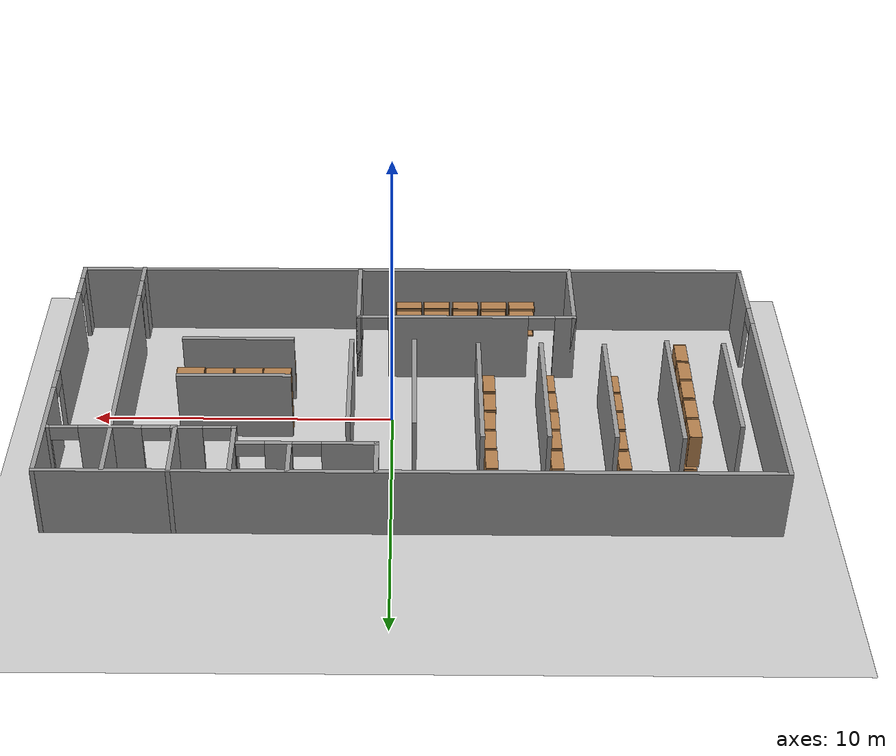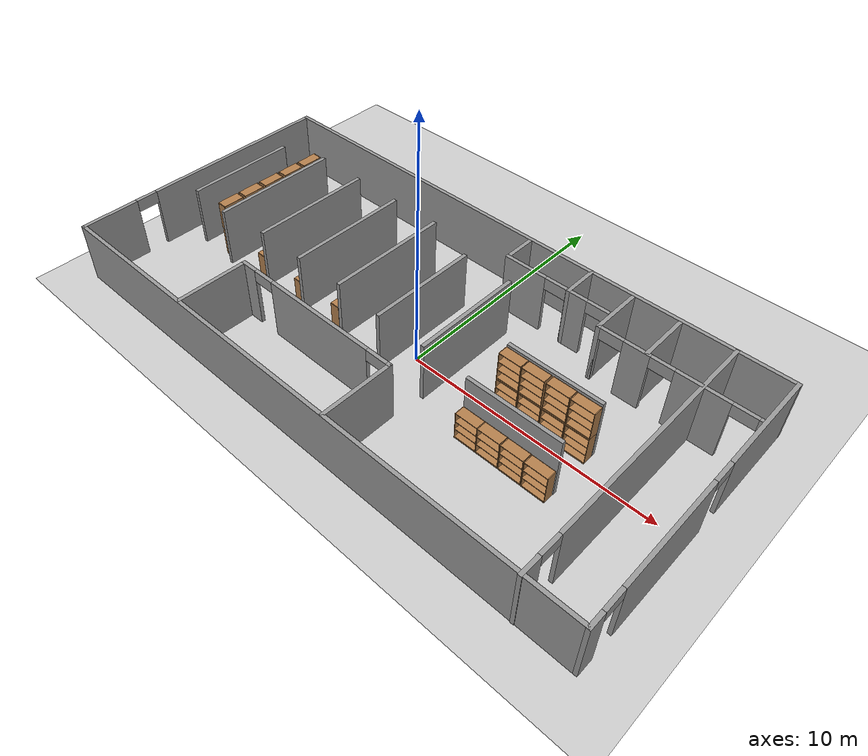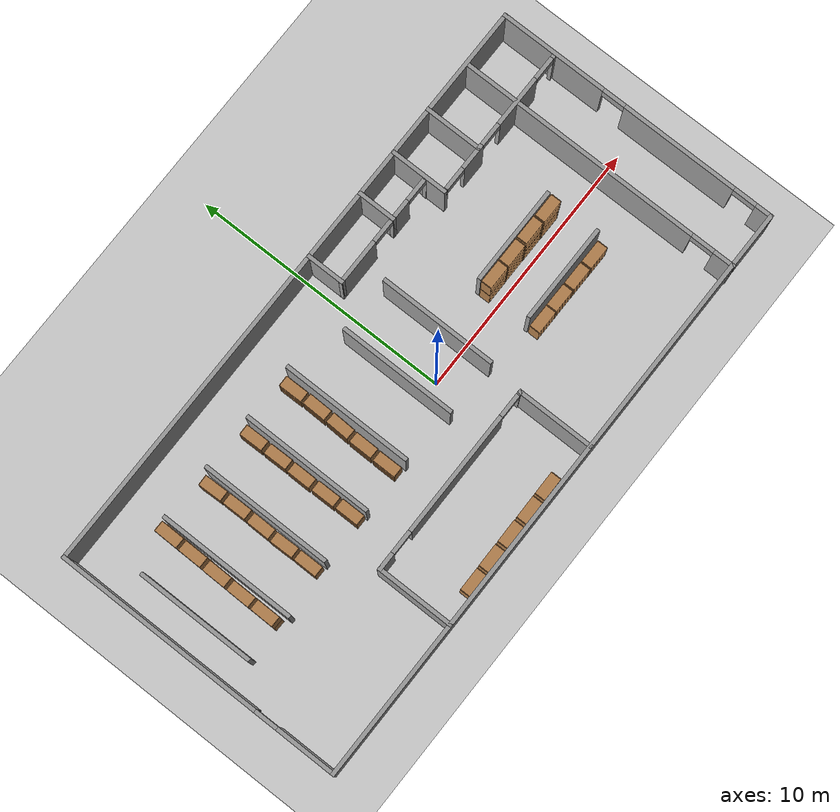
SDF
<sdf version="1.6">
 <world name="default">
  <light name="sun" type="directional">
   <pose>0 0 10 0 -0 0</pose>
   <diffuse>0.8 0.8 0.8 1</diffuse>
   <specular>0.2 0.2 0.2 1</specular>
   <attenuation>
    <range>1000</range>
    <constant>0.9</constant>
    <linear>0.01</linear>
    <quadratic>0.001</quadratic>
   </attenuation>
   <direction>-0.5 0.1 -0.9</direction>
  </light>
  <model name="ground_plane">
   <static>1</static>
   <link name="link">
    <collision name="collision">
     <geometry><plane><normal>0 0 1</normal><size>100 100</size></plane></geometry>
     <surface>
      <contact><collide_bitmask>65535</collide_bitmask></contact>
      <friction><ode><mu>100</mu><mu2>50</mu2></ode></friction>
     </surface>
    </collision>
    <visual name="visual">
     <cast_shadows>0</cast_shadows>
     <geometry><plane><normal>0 0 1</normal><size>100 100</size></plane></geometry>
     <material>
      <script><uri>file://media/materials/scripts/gazebo.material</uri><name>Gazebo/Grey</name></script>
     </material>
    </visual>
   </link>
  </model>
  <gravity>0 0 -9.8</gravity>
  <magnetic_field>6e-06 2.3e-05 -4.2e-05</magnetic_field>
  <atmosphere type="adiabatic"/>
  <physics name="default_physics" default="0" type="ode">
   <max_step_size>0.001</max_step_size>
   <real_time_factor>1</real_time_factor>
   <real_time_update_rate>1000</real_time_update_rate>
  </physics>
  <scene><ambient>0.4 0.4 0.4 1</ambient><background>0.7 0.7 0.7 1</background><shadows>1</shadows></scene>
  <spherical_coordinates>
   <surface_model>EARTH_WGS84</surface_model>
   <latitude_deg>0</latitude_deg>
   <longitude_deg>0</longitude_deg>
   <elevation>0</elevation>
   <heading_deg>0</heading_deg>
  </spherical_coordinates>
  <model name="retail">
   <pose>-0.623438 0.12885 0 0 -0 0</pose>
   <link name="Wall_16">
    <collision name="Wall_16_Collision">
     <geometry><box><size>23.25 0.15 2.5</size></box></geometry>
     <pose>0 0 1.25 0 -0 0</pose>
    </collision>
    <visual name="Wall_16_Visual">
     <pose>0 0 1.25 0 -0 0</pose>
     <geometry><box><size>23.25 0.15 2.5</size></box></geometry>
     <material>
      <script><uri>file://media/materials/scripts/gazebo.material</uri><name>Gazebo/Grey</name></script>
      <ambient>1 1 1 1</ambient>
     </material>
     <meta><layer>0</layer></meta>
    </visual>
    <pose>0 -5.54055 0 0 -0 0</pose>
   </link>
   <link name="Wall_17">
    <pose>11.55 0.009451 0 0 -0 1.5708</pose>
    <visual name="Wall_17_Visual_0">
     <pose>-5.28706 0 1.25 0 -0 0</pose>
     <geometry><box><size>0.675885 0.15 2.5</size></box></geometry>
     <material>
      <script><uri>file://media/materials/scripts/gazebo.material</uri><name>Gazebo/Grey</name></script>
      <ambient>1 1 1 1</ambient>
     </material>
     <meta><layer>0</layer></meta>
    </visual>
    <collision name="Wall_17_Collision_0">
     <geometry><box><size>0.675885 0.15 2.5</size></box></geometry>
     <pose>-5.28706 0 1.25 0 -0 0</pose>
    </collision>
    <visual name="Wall_17_Visual_1">
     <pose>-1.77241 0 1.25 0 -0 0</pose>
     <geometry><box><size>4.55341 0.15 2.5</size></box></geometry>
     <material>
      <script><uri>file://media/materials/scripts/gazebo.material</uri><name>Gazebo/Grey</name></script>
      <ambient>1 1 1 1</ambient>
     </material>
     <meta><layer>0</layer></meta>
    </visual>
    <collision name="Wall_17_Collision_1">
     <geometry><box><size>4.55341 0.15 2.5</size></box></geometry>
     <pose>-1.77241 0 1.25 0 -0 0</pose>
    </collision>
    <visual name="Wall_17_Visual_2">
     <pose>3.51465 0 1.25 0 -0 0</pose>
     <geometry><box><size>4.2207 0.15 2.5</size></box></geometry>
     <material>
      <script><uri>file://media/materials/scripts/gazebo.material</uri><name>Gazebo/Grey</name></script>
      <ambient>1 1 1 1</ambient>
     </material>
     <meta><layer>0</layer></meta>
    </visual>
    <collision name="Wall_17_Collision_2">
     <geometry><box><size>4.2207 0.15 2.5</size></box></geometry>
     <pose>3.51465 0 1.25 0 -0 0</pose>
    </collision>
    <visual name="Wall_17_Visual_3">
     <pose>-4.49911 0 2.25 0 -0 0</pose>
     <geometry><box><size>0.9 0.15 0.5</size></box></geometry>
     <material>
      <script><uri>file://media/materials/scripts/gazebo.material</uri><name>Gazebo/Grey</name></script>
      <ambient>1 1 1 1</ambient>
     </material>
     <meta><layer>0</layer></meta>
    </visual>
    <collision name="Wall_17_Collision_3">
     <geometry><box><size>0.9 0.15 0.5</size></box></geometry>
     <pose>-4.49911 0 2.25 0 -0 0</pose>
    </collision>
    <visual name="Wall_17_Visual_4">
     <pose>0.954296 0 2.25 0 -0 0</pose>
     <geometry><box><size>0.9 0.15 0.5</size></box></geometry>
     <material>
      <script><uri>file://media/materials/scripts/gazebo.material</uri><name>Gazebo/Grey</name></script>
      <ambient>1 1 1 1</ambient>
     </material>
     <meta><layer>0</layer></meta>
    </visual>
    <collision name="Wall_17_Collision_4">
     <geometry><box><size>0.9 0.15 0.5</size></box></geometry>
     <pose>0.954296 0 2.25 0 -0 0</pose>
    </collision>
   </link>
   <link name="Wall_18">
    <collision name="Wall_18_Collision">
     <geometry><box><size>23.25 0.15 2.5</size></box></geometry>
     <pose>0 0 1.25 0 -0 0</pose>
    </collision>
    <visual name="Wall_18_Visual">
     <pose>0 0 1.25 0 -0 0</pose>
     <geometry><box><size>23.25 0.15 2.5</size></box></geometry>
     <material>
      <script><uri>file://media/materials/scripts/gazebo.material</uri><name>Gazebo/Grey</name></script>
      <ambient>1 1 1 1</ambient>
     </material>
     <meta><layer>0</layer></meta>
    </visual>
    <pose>0 5.55945 0 0 -0 3.14159</pose>
   </link>
   <link name="Wall_19">
    <pose>-11.55 0.009451 0 0 -0 -1.5708</pose>
    <visual name="Wall_19_Visual_0">
     <pose>-1.63416 0 1.25 0 -0 0</pose>
     <geometry><box><size>7.98168 0.15 2.5</size></box></geometry>
     <material>
      <script><uri>file://media/materials/scripts/gazebo.material</uri><name>Gazebo/Grey</name></script>
      <ambient>1 1 1 1</ambient>
     </material>
     <meta><layer>0</layer></meta>
    </visual>
    <collision name="Wall_19_Collision_0">
     <geometry><box><size>7.98168 0.15 2.5</size></box></geometry>
     <pose>-1.63416 0 1.25 0 -0 0</pose>
    </collision>
    <visual name="Wall_19_Visual_1">
     <pose>4.44084 0 1.25 0 -0 0</pose>
     <geometry><box><size>2.36832 0.15 2.5</size></box></geometry>
     <material>
      <script><uri>file://media/materials/scripts/gazebo.material</uri><name>Gazebo/Grey</name></script>
      <ambient>1 1 1 1</ambient>
     </material>
     <meta><layer>0</layer></meta>
    </visual>
    <collision name="Wall_19_Collision_1">
     <geometry><box><size>2.36832 0.15 2.5</size></box></geometry>
     <pose>4.44084 0 1.25 0 -0 0</pose>
    </collision>
    <visual name="Wall_19_Visual_2">
     <pose>2.80668 0 2.25 0 -0 0</pose>
     <geometry><box><size>0.9 0.15 0.5</size></box></geometry>
     <material>
      <script><uri>file://media/materials/scripts/gazebo.material</uri><name>Gazebo/Grey</name></script>
      <ambient>1 1 1 1</ambient>
     </material>
     <meta><layer>0</layer></meta>
    </visual>
    <collision name="Wall_19_Collision_2">
     <geometry><box><size>0.9 0.15 0.5</size></box></geometry>
     <pose>2.80668 0 2.25 0 -0 0</pose>
    </collision>
   </link>
   <link name="Wall_35">
    <collision name="Wall_35_Collision">
     <geometry><box><size>2.25 0.15 2.5</size></box></geometry>
     <pose>0 0 1.25 0 -0 0</pose>
    </collision>
    <visual name="Wall_35_Visual">
     <pose>0 0 1.25 0 -0 0</pose>
     <geometry><box><size>2.25 0.15 2.5</size></box></geometry>
     <material>
      <script><uri>file://media/materials/scripts/gazebo.material</uri><name>Gazebo/Grey</name></script>
      <ambient>1 1 1 1</ambient>
     </material>
     <meta><layer>0</layer></meta>
    </visual>
    <pose>5.55195 4.48539 0 0 -0 -1.5708</pose>
   </link>
   <link name="Wall_36">
    <pose>8.47695 3.43539 0 0 -0 0</pose>
    <visual name="Wall_36_Visual_0">
     <pose>-2.9149 0 1.25 0 -0 0</pose>
     <geometry><box><size>0.170197 0.15 2.5</size></box></geometry>
     <material>
      <script><uri>file://media/materials/scripts/gazebo.material</uri><name>Gazebo/Grey</name></script>
      <ambient>1 1 1 1</ambient>
     </material>
     <meta><layer>0</layer></meta>
    </visual>
    <collision name="Wall_36_Collision_0">
     <geometry><box><size>0.170197 0.15 2.5</size></box></geometry>
     <pose>-2.9149 0 1.25 0 -0 0</pose>
    </collision>
    <visual name="Wall_36_Visual_1">
     <pose>-1.42075 0 1.25 0 -0 0</pose>
     <geometry><box><size>1.0181 0.15 2.5</size></box></geometry>
     <material>
      <script><uri>file://media/materials/scripts/gazebo.material</uri><name>Gazebo/Grey</name></script>
      <ambient>1 1 1 1</ambient>
     </material>
     <meta><layer>0</layer></meta>
    </visual>
    <collision name="Wall_36_Collision_1">
     <geometry><box><size>1.0181 0.15 2.5</size></box></geometry>
     <pose>-1.42075 0 1.25 0 -0 0</pose>
    </collision>
    <visual name="Wall_36_Visual_2">
     <pose>0.986268 0 1.25 0 -0 0</pose>
     <geometry><box><size>1.99595 0.15 2.5</size></box></geometry>
     <material>
      <script><uri>file://media/materials/scripts/gazebo.material</uri><name>Gazebo/Grey</name></script>
      <ambient>1 1 1 1</ambient>
     </material>
     <meta><layer>0</layer></meta>
    </visual>
    <collision name="Wall_36_Collision_2">
     <geometry><box><size>1.99595 0.15 2.5</size></box></geometry>
     <pose>0.986268 0 1.25 0 -0 0</pose>
    </collision>
    <visual name="Wall_36_Visual_3">
     <pose>2.94212 0 1.25 0 -0 0</pose>
     <geometry><box><size>0.115758 0.15 2.5</size></box></geometry>
     <material>
      <script><uri>file://media/materials/scripts/gazebo.material</uri><name>Gazebo/Grey</name></script>
      <ambient>1 1 1 1</ambient>
     </material>
     <meta><layer>0</layer></meta>
    </visual>
    <collision name="Wall_36_Collision_3">
     <geometry><box><size>0.115758 0.15 2.5</size></box></geometry>
     <pose>2.94212 0 1.25 0 -0 0</pose>
    </collision>
    <visual name="Wall_36_Visual_4">
     <pose>-2.3798 0 2.25 0 -0 0</pose>
     <geometry><box><size>0.9 0.15 0.5</size></box></geometry>
     <material>
      <script><uri>file://media/materials/scripts/gazebo.material</uri><name>Gazebo/Grey</name></script>
      <ambient>1 1 1 1</ambient>
     </material>
     <meta><layer>0</layer></meta>
    </visual>
    <collision name="Wall_36_Collision_4">
     <geometry><box><size>0.9 0.15 0.5</size></box></geometry>
     <pose>-2.3798 0 2.25 0 -0 0</pose>
    </collision>
    <visual name="Wall_36_Visual_5">
     <pose>-0.461707 0 2.25 0 -0 0</pose>
     <geometry><box><size>0.9 0.15 0.5</size></box></geometry>
     <material>
      <script><uri>file://media/materials/scripts/gazebo.material</uri><name>Gazebo/Grey</name></script>
      <ambient>1 1 1 1</ambient>
     </material>
     <meta><layer>0</layer></meta>
    </visual>
    <collision name="Wall_36_Collision_5">
     <geometry><box><size>0.9 0.15 0.5</size></box></geometry>
     <pose>-0.461707 0 2.25 0 -0 0</pose>
    </collision>
    <visual name="Wall_36_Visual_6">
     <pose>2.43424 0 2.25 0 -0 0</pose>
     <geometry><box><size>0.9 0.15 0.5</size></box></geometry>
     <material>
      <script><uri>file://media/materials/scripts/gazebo.material</uri><name>Gazebo/Grey</name></script>
      <ambient>1 1 1 1</ambient>
     </material>
     <meta><layer>0</layer></meta>
    </visual>
    <collision name="Wall_36_Collision_6">
     <geometry><box><size>0.9 0.15 0.5</size></box></geometry>
     <pose>2.43424 0 2.25 0 -0 0</pose>
    </collision>
   </link>
   <link name="Wall_38">
    <pose>9.44374 -0.014611 0 0 -0 -1.5708</pose>
    <visual name="Wall_38_Visual_0">
     <pose>-0.875193 0 1.25 0 -0 0</pose>
     <geometry><box><size>9.49961 0.15 2.5</size></box></geometry>
     <material>
      <script><uri>file://media/materials/scripts/gazebo.material</uri><name>Gazebo/Grey</name></script>
      <ambient>1 1 1 1</ambient>
     </material>
     <meta><layer>0</layer></meta>
    </visual>
    <collision name="Wall_38_Collision_0">
     <geometry><box><size>9.49961 0.15 2.5</size></box></geometry>
     <pose>-0.875193 0 1.25 0 -0 0</pose>
    </collision>
    <visual name="Wall_38_Visual_1">
     <pose>5.19981 0 1.25 0 -0 0</pose>
     <geometry><box><size>0.850386 0.15 2.5</size></box></geometry>
     <material>
      <script><uri>file://media/materials/scripts/gazebo.material</uri><name>Gazebo/Grey</name></script>
      <ambient>1 1 1 1</ambient>
     </material>
     <meta><layer>0</layer></meta>
    </visual>
    <collision name="Wall_38_Collision_1">
     <geometry><box><size>0.850386 0.15 2.5</size></box></geometry>
     <pose>5.19981 0 1.25 0 -0 0</pose>
    </collision>
    <visual name="Wall_38_Visual_2">
     <pose>4.32461 0 2.25 0 -0 0</pose>
     <geometry><box><size>0.9 0.15 0.5</size></box></geometry>
     <material>
      <script><uri>file://media/materials/scripts/gazebo.material</uri><name>Gazebo/Grey</name></script>
      <ambient>1 1 1 1</ambient>
     </material>
     <meta><layer>0</layer></meta>
    </visual>
    <collision name="Wall_38_Collision_2">
     <geometry><box><size>0.9 0.15 0.5</size></box></geometry>
     <pose>4.32461 0 2.25 0 -0 0</pose>
    </collision>
   </link>
   <link name="Wall_44">
    <collision name="Wall_44_Collision">
     <geometry><box><size>2.25 0.15 2.5</size></box></geometry>
     <pose>0 0 1.25 0 -0 0</pose>
    </collision>
    <visual name="Wall_44_Visual">
     <pose>0 0 1.25 0 -0 0</pose>
     <geometry><box><size>2.25 0.15 2.5</size></box></geometry>
     <material>
      <script><uri>file://media/materials/scripts/gazebo.material</uri><name>Gazebo/Grey</name></script>
      <ambient>1 1 1 1</ambient>
     </material>
     <meta><layer>0</layer></meta>
    </visual>
    <pose>7.40721 4.51461 0 0 -0 1.5708</pose>
   </link>
   <link name="Wall_46">
    <collision name="Wall_46_Collision">
     <geometry><box><size>3 0.15 2.5</size></box></geometry>
     <pose>0 0 1.25 0 -0 0</pose>
    </collision>
    <visual name="Wall_46_Visual">
     <pose>0 0 1.25 0 -0 0</pose>
     <geometry><box><size>3 0.15 2.5</size></box></geometry>
     <material>
      <script><uri>file://media/materials/scripts/gazebo.material</uri><name>Gazebo/Grey</name></script>
      <ambient>1 1 1 1</ambient>
     </material>
     <meta><layer>0</layer></meta>
    </visual>
    <pose>-5.5361 -4.08719 0 0 -0 1.5708</pose>
   </link>
   <link name="Wall_47">
    <pose>-1.8611 -2.66219 0 0 -0 0</pose>
    <visual name="Wall_47_Visual_0">
     <pose>-3.38624 0 1.25 0 -0 0</pose>
     <geometry><box><size>0.727518 0.15 2.5</size></box></geometry>
     <material>
      <script><uri>file://media/materials/scripts/gazebo.material</uri><name>Gazebo/Grey</name></script>
      <ambient>1 1 1 1</ambient>
     </material>
     <meta><layer>0</layer></meta>
    </visual>
    <collision name="Wall_47_Collision_0">
     <geometry><box><size>0.727518 0.15 2.5</size></box></geometry>
     <pose>-3.38624 0 1.25 0 -0 0</pose>
    </collision>
    <visual name="Wall_47_Visual_1">
     <pose>0.267053 0 1.25 0 -0 0</pose>
     <geometry><box><size>4.77907 0.15 2.5</size></box></geometry>
     <material>
      <script><uri>file://media/materials/scripts/gazebo.material</uri><name>Gazebo/Grey</name></script>
      <ambient>1 1 1 1</ambient>
     </material>
     <meta><layer>0</layer></meta>
    </visual>
    <collision name="Wall_47_Collision_1">
     <geometry><box><size>4.77907 0.15 2.5</size></box></geometry>
     <pose>0.267053 0 1.25 0 -0 0</pose>
    </collision>
    <visual name="Wall_47_Visual_2">
     <pose>3.65329 0 1.25 0 -0 0</pose>
     <geometry><box><size>0.193413 0.15 2.5</size></box></geometry>
     <material>
      <script><uri>file://media/materials/scripts/gazebo.material</uri><name>Gazebo/Grey</name></script>
      <ambient>1 1 1 1</ambient>
     </material>
     <meta><layer>0</layer></meta>
    </visual>
    <collision name="Wall_47_Collision_2">
     <geometry><box><size>0.193413 0.15 2.5</size></box></geometry>
     <pose>3.65329 0 1.25 0 -0 0</pose>
    </collision>
    <visual name="Wall_47_Visual_3">
     <pose>-2.57248 0 2.25 0 -0 0</pose>
     <geometry><box><size>0.9 0.15 0.5</size></box></geometry>
     <material>
      <script><uri>file://media/materials/scripts/gazebo.material</uri><name>Gazebo/Grey</name></script>
      <ambient>1 1 1 1</ambient>
     </material>
     <meta><layer>0</layer></meta>
    </visual>
    <collision name="Wall_47_Collision_3">
     <geometry><box><size>0.9 0.15 0.5</size></box></geometry>
     <pose>-2.57248 0 2.25 0 -0 0</pose>
    </collision>
    <visual name="Wall_47_Visual_4">
     <pose>3.10659 0 2.25 0 -0 0</pose>
     <geometry><box><size>0.9 0.15 0.5</size></box></geometry>
     <material>
      <script><uri>file://media/materials/scripts/gazebo.material</uri><name>Gazebo/Grey</name></script>
      <ambient>1 1 1 1</ambient>
     </material>
     <meta><layer>0</layer></meta>
    </visual>
    <collision name="Wall_47_Collision_4">
     <geometry><box><size>0.9 0.15 0.5</size></box></geometry>
     <pose>3.10659 0 2.25 0 -0 0</pose>
    </collision>
   </link>
   <link name="Wall_48">
    <collision name="Wall_48_Collision">
     <geometry><box><size>3 0.15 2.5</size></box></geometry>
     <pose>0 0 1.25 0 -0 0</pose>
    </collision>
    <visual name="Wall_48_Visual">
     <pose>0 0 1.25 0 -0 0</pose>
     <geometry><box><size>3 0.15 2.5</size></box></geometry>
     <material>
      <script><uri>file://media/materials/scripts/gazebo.material</uri><name>Gazebo/Grey</name></script>
      <ambient>1 1 1 1</ambient>
     </material>
     <meta><layer>0</layer></meta>
    </visual>
    <pose>1.8139 -4.08719 0 0 -0 -1.5708</pose>
   </link>
   <link name="Wall_50">
    <collision name="Wall_50_Collision">
     <geometry><box><size>1.5 0.15 2.5</size></box></geometry>
     <pose>0 0 1.25 0 -0 0</pose>
    </collision>
    <visual name="Wall_50_Visual">
     <pose>0 0 1.25 0 -0 0</pose>
     <geometry><box><size>1.5 0.15 2.5</size></box></geometry>
     <material>
      <script><uri>file://media/materials/scripts/gazebo.material</uri><name>Gazebo/Grey</name></script>
      <ambient>1 1 1 1</ambient>
     </material>
     <meta><layer>0</layer></meta>
    </visual>
    <pose>1.0704 4.87092 0 0 -0 -1.5708</pose>
   </link>
   <link name="Wall_56">
    <collision name="Wall_56_Collision">
     <geometry><box><size>1.5 0.15 2.5</size></box></geometry>
     <pose>0 0 1.25 0 -0 0</pose>
    </collision>
    <visual name="Wall_56_Visual">
     <pose>0 0 1.25 0 -0 0</pose>
     <geometry><box><size>1.5 0.15 2.5</size></box></geometry>
     <material>
      <script><uri>file://media/materials/scripts/gazebo.material</uri><name>Gazebo/Grey</name></script>
      <ambient>1 1 1 1</ambient>
     </material>
     <meta><layer>0</layer></meta>
    </visual>
    <pose>3.77288 4.87092 0 0 -0 -1.5708</pose>
   </link>
   <link name="Wall_60">
    <pose>3.2454 4.19592 0 0 -0 0</pose>
    <visual name="Wall_60_Visual_0">
     <pose>-1.3533 0 1.25 0 -0 0</pose>
     <geometry><box><size>1.79341 0.15 2.5</size></box></geometry>
     <material>
      <script><uri>file://media/materials/scripts/gazebo.material</uri><name>Gazebo/Grey</name></script>
      <ambient>1 1 1 1</ambient>
     </material>
     <meta><layer>0</layer></meta>
    </visual>
    <collision name="Wall_60_Collision_0">
     <geometry><box><size>1.79341 0.15 2.5</size></box></geometry>
     <pose>-1.3533 0 1.25 0 -0 0</pose>
    </collision>
    <visual name="Wall_60_Visual_1">
     <pose>0.877237 0 1.25 0 -0 0</pose>
     <geometry><box><size>0.867658 0.15 2.5</size></box></geometry>
     <material>
      <script><uri>file://media/materials/scripts/gazebo.material</uri><name>Gazebo/Grey</name></script>
      <ambient>1 1 1 1</ambient>
     </material>
     <meta><layer>0</layer></meta>
    </visual>
    <collision name="Wall_60_Collision_1">
     <geometry><box><size>0.867658 0.15 2.5</size></box></geometry>
     <pose>0.877237 0 1.25 0 -0 0</pose>
    </collision>
    <visual name="Wall_60_Visual_2">
     <pose>2.23053 0 1.25 0 -0 0</pose>
     <geometry><box><size>0.038935 0.15 2.5</size></box></geometry>
     <material>
      <script><uri>file://media/materials/scripts/gazebo.material</uri><name>Gazebo/Grey</name></script>
      <ambient>1 1 1 1</ambient>
     </material>
     <meta><layer>0</layer></meta>
    </visual>
    <collision name="Wall_60_Collision_2">
     <geometry><box><size>0.038935 0.15 2.5</size></box></geometry>
     <pose>2.23053 0 1.25 0 -0 0</pose>
    </collision>
    <visual name="Wall_60_Visual_3">
     <pose>-0.006592 0 2.25 0 -0 0</pose>
     <geometry><box><size>0.9 0.15 0.5</size></box></geometry>
     <material>
      <script><uri>file://media/materials/scripts/gazebo.material</uri><name>Gazebo/Grey</name></script>
      <ambient>1 1 1 1</ambient>
     </material>
     <meta><layer>0</layer></meta>
    </visual>
    <collision name="Wall_60_Collision_3">
     <geometry><box><size>0.9 0.15 0.5</size></box></geometry>
     <pose>-0.006592 0 2.25 0 -0 0</pose>
    </collision>
    <visual name="Wall_60_Visual_4">
     <pose>1.76107 0 2.25 0 -0 0</pose>
     <geometry><box><size>0.9 0.15 0.5</size></box></geometry>
     <material>
      <script><uri>file://media/materials/scripts/gazebo.material</uri><name>Gazebo/Grey</name></script>
      <ambient>1 1 1 1</ambient>
     </material>
     <meta><layer>0</layer></meta>
    </visual>
    <collision name="Wall_60_Collision_4">
     <geometry><box><size>0.9 0.15 0.5</size></box></geometry>
     <pose>1.76107 0 2.25 0 -0 0</pose>
    </collision>
   </link>
   <link name="Wall_62">
    <collision name="Wall_62_Collision">
     <geometry><box><size>4.5 0.15 2.5</size></box></geometry>
     <pose>0 0 1.25 0 -0 0</pose>
    </collision>
    <visual name="Wall_62_Visual">
     <pose>0 0 1.25 0 -0 0</pose>
     <geometry><box><size>4.5 0.15 2.5</size></box></geometry>
     <material>
      <script><uri>file://media/materials/scripts/gazebo.material</uri><name>Gazebo/Grey</name></script>
      <ambient>1 1 1 1</ambient>
     </material>
     <meta><layer>0</layer></meta>
    </visual>
    <pose>-10.4135 1.04533 0 0 -0 -1.5708</pose>
   </link>
   <link name="Wall_64">
    <collision name="Wall_64_Collision">
     <geometry><box><size>5.25 0.15 2.5</size></box></geometry>
     <pose>0 0 1.25 0 -0 0</pose>
    </collision>
    <visual name="Wall_64_Visual">
     <pose>0 0 1.25 0 -0 0</pose>
     <geometry><box><size>5.25 0.15 2.5</size></box></geometry>
     <material>
      <script><uri>file://media/materials/scripts/gazebo.material</uri><name>Gazebo/Grey</name></script>
      <ambient>1 1 1 1</ambient>
     </material>
     <meta><layer>0</layer></meta>
    </visual>
    <pose>-8.53304 1.27209 0 0 -0 -1.5708</pose>
   </link>
   <link name="Wall_66">
    <collision name="Wall_66_Collision">
     <geometry><box><size>5 0.15 2.5</size></box></geometry>
     <pose>0 0 1.25 0 -0 0</pose>
    </collision>
    <visual name="Wall_66_Visual">
     <pose>0 0 1.25 0 -0 0</pose>
     <geometry><box><size>5 0.15 2.5</size></box></geometry>
     <material>
      <script><uri>file://media/materials/scripts/gazebo.material</uri><name>Gazebo/Grey</name></script>
      <ambient>1 1 1 1</ambient>
     </material>
     <meta><layer>0</layer></meta>
    </visual>
    <pose>-6.4269 1.35948 0 0 -0 -1.5708</pose>
   </link>
   <link name="Wall_68">
    <collision name="Wall_68_Collision">
     <geometry><box><size>5 0.15 2.5</size></box></geometry>
     <pose>0 0 1.25 0 -0 0</pose>
    </collision>
    <visual name="Wall_68_Visual">
     <pose>0 0 1.25 0 -0 0</pose>
     <geometry><box><size>5 0.15 2.5</size></box></geometry>
     <material>
      <script><uri>file://media/materials/scripts/gazebo.material</uri><name>Gazebo/Grey</name></script>
      <ambient>1 1 1 1</ambient>
     </material>
     <meta><layer>0</layer></meta>
    </visual>
    <pose>-4.32363 1.32963 0 0 -0 -1.5708</pose>
   </link>
   <link name="Wall_70">
    <collision name="Wall_70_Collision">
     <geometry><box><size>5 0.15 2.5</size></box></geometry>
     <pose>0 0 1.25 0 -0 0</pose>
    </collision>
    <visual name="Wall_70_Visual">
     <pose>0 0 1.25 0 -0 0</pose>
     <geometry><box><size>5 0.15 2.5</size></box></geometry>
     <material>
      <script><uri>file://media/materials/scripts/gazebo.material</uri><name>Gazebo/Grey</name></script>
      <ambient>1 1 1 1</ambient>
     </material>
     <meta><layer>0</layer></meta>
    </visual>
    <pose>-2.22937 1.34832 0 0 -0 -1.5708</pose>
   </link>
   <link name="Wall_72">
    <collision name="Wall_72_Collision">
     <geometry><box><size>4.5 0.15 2.5</size></box></geometry>
     <pose>0 0 1.25 0 -0 0</pose>
    </collision>
    <visual name="Wall_72_Visual">
     <pose>0 0 1.25 0 -0 0</pose>
     <geometry><box><size>4.5 0.15 2.5</size></box></geometry>
     <material>
      <script><uri>file://media/materials/scripts/gazebo.material</uri><name>Gazebo/Grey</name></script>
      <ambient>1 1 1 1</ambient>
     </material>
     <meta><layer>0</layer></meta>
    </visual>
    <pose>-0.097723 0.925172 0 0 -0 -1.5708</pose>
   </link>
   <link name="Wall_74">
    <collision name="Wall_74_Collision">
     <geometry><box><size>4.5 0.15 2.5</size></box></geometry>
     <pose>0 0 1.25 0 -0 0</pose>
    </collision>
    <visual name="Wall_74_Visual">
     <pose>0 0 1.25 0 -0 0</pose>
     <geometry><box><size>4.5 0.15 2.5</size></box></geometry>
     <material>
      <script><uri>file://media/materials/scripts/gazebo.material</uri><name>Gazebo/Grey</name></script>
      <ambient>1 1 1 1</ambient>
     </material>
     <meta><layer>0</layer></meta>
    </visual>
    <pose>1.99653 0.906473 0 0 -0 -1.5708</pose>
   </link>
   <link name="Wall_76">
    <collision name="Wall_76_Collision">
     <geometry><box><size>3.75 0.15 2.5</size></box></geometry>
     <pose>0 0 1.25 0 -0 0</pose>
    </collision>
    <visual name="Wall_76_Visual">
     <pose>0 0 1.25 0 -0 0</pose>
     <geometry><box><size>3.75 0.15 2.5</size></box></geometry>
     <material>
      <script><uri>file://media/materials/scripts/gazebo.material</uri><name>Gazebo/Grey</name></script>
      <ambient>1 1 1 1</ambient>
     </material>
     <meta><layer>0</layer></meta>
    </visual>
    <pose>5.79729 0.706741 0 0 -0 0</pose>
   </link>
   <link name="Wall_78">
    <collision name="Wall_78_Collision">
     <geometry><box><size>3.75 0.15 2.5</size></box></geometry>
     <pose>0 0 1.25 0 -0 0</pose>
    </collision>
    <visual name="Wall_78_Visual">
     <pose>0 0 1.25 0 -0 0</pose>
     <geometry><box><size>3.75 0.15 2.5</size></box></geometry>
     <material>
      <script><uri>file://media/materials/scripts/gazebo.material</uri><name>Gazebo/Grey</name></script>
      <ambient>1 1 1 1</ambient>
     </material>
     <meta><layer>0</layer></meta>
    </visual>
    <pose>5.80269 -1.35025 0 0 -0 0</pose>
   </link>
   <static>1</static>
  </model>
  <model name="bookshelf">
   <static>1</static>
   <link name="link">
    <inertial><mass>1</mass></inertial>
    <collision name="back">
     <pose>0 0.005 0.6 0 -0 0</pose>
     <geometry><box><size>0.9 0.01 1.2</size></box></geometry>
    </collision>
    <visual name="visual1">
     <pose>0 0.005 0.6 0 -0 0</pose>
     <geometry><box><size>0.9 0.01 1.2</size></box></geometry>
     <material>
      <script><uri>file://media/materials/scripts/gazebo.material</uri><name>Gazebo/Wood</name></script>
     </material>
    </visual>
    <collision name="left_side">
     <pose>0.45 -0.195 0.6 0 -0 0</pose>
     <geometry><box><size>0.02 0.4 1.2</size></box></geometry>
    </collision>
    <visual name="visual2">
     <pose>0.45 -0.195 0.6 0 -0 0</pose>
     <geometry><box><size>0.02 0.4 1.2</size></box></geometry>
     <material>
      <script><uri>file://media/materials/scripts/gazebo.material</uri><name>Gazebo/Wood</name></script>
     </material>
    </visual>
    <collision name="right_side">
     <pose>-0.45 -0.195 0.6 0 -0 0</pose>
     <geometry><box><size>0.02 0.4 1.2</size></box></geometry>
    </collision>
    <visual name="visual3">
     <pose>-0.45 -0.195 0.6 0 -0 0</pose>
     <geometry><box><size>0.02 0.4 1.2</size></box></geometry>
     <material>
      <script><uri>file://media/materials/scripts/gazebo.material</uri><name>Gazebo/Wood</name></script>
     </material>
    </visual>
    <collision name="bottom">
     <pose>0 -0.195 0.03 0 -0 0</pose>
     <geometry><box><size>0.88 0.4 0.06</size></box></geometry>
    </collision>
    <visual name="visual4">
     <pose>0 -0.195 0.03 0 -0 0</pose>
     <geometry><box><size>0.88 0.4 0.06</size></box></geometry>
     <material>
      <script><uri>file://media/materials/scripts/gazebo.material</uri><name>Gazebo/Wood</name></script>
     </material>
    </visual>
    <collision name="top">
     <pose>0 -0.195 1.19 0 -0 0</pose>
     <geometry><box><size>0.88 0.4 0.02</size></box></geometry>
    </collision>
    <visual name="visual5">
     <pose>0 -0.195 1.19 0 -0 0</pose>
     <geometry><box><size>0.88 0.4 0.02</size></box></geometry>
     <material>
      <script><uri>file://media/materials/scripts/gazebo.material</uri><name>Gazebo/Wood</name></script>
     </material>
    </visual>
    <collision name="low_shelf">
     <pose>0 -0.195 0.43 0 -0 0</pose>
     <geometry><box><size>0.88 0.4 0.02</size></box></geometry>
    </collision>
    <visual name="visual6">
     <pose>0 -0.195 0.43 0 -0 0</pose>
     <geometry><box><size>0.88 0.4 0.02</size></box></geometry>
     <material>
      <script><uri>file://media/materials/scripts/gazebo.material</uri><name>Gazebo/Wood</name></script>
     </material>
    </visual>
    <collision name="high_shelf">
     <pose>0 -0.195 0.8 0 -0 0</pose>
     <geometry><box><size>0.88 0.4 0.02</size></box></geometry>
    </collision>
    <visual name="visual7">
     <pose>0 -0.195 0.8 0 -0 0</pose>
     <geometry><box><size>0.88 0.4 0.02</size></box></geometry>
     <material>
      <script><uri>file://media/materials/scripts/gazebo.material</uri><name>Gazebo/Wood</name></script>
     </material>
    </visual>
   </link>
   <pose>3.75992 0.728747 0 0 -0 0</pose>
  </model>
  <model name="bookshelf_0">
   <static>1</static>
   <link name="link">
    <inertial><mass>1</mass></inertial>
    <collision name="back">
     <pose>0 0.005 0.6 0 -0 0</pose>
     <geometry><box><size>0.9 0.01 1.2</size></box></geometry>
    </collision>
    <visual name="visual1">
     <pose>0 0.005 0.6 0 -0 0</pose>
     <geometry><box><size>0.9 0.01 1.2</size></box></geometry>
     <material>
      <script><uri>file://media/materials/scripts/gazebo.material</uri><name>Gazebo/Wood</name></script>
     </material>
    </visual>
    <collision name="left_side">
     <pose>0.45 -0.195 0.6 0 -0 0</pose>
     <geometry><box><size>0.02 0.4 1.2</size></box></geometry>
    </collision>
    <visual name="visual2">
     <pose>0.45 -0.195 0.6 0 -0 0</pose>
     <geometry><box><size>0.02 0.4 1.2</size></box></geometry>
     <material>
      <script><uri>file://media/materials/scripts/gazebo.material</uri><name>Gazebo/Wood</name></script>
     </material>
    </visual>
    <collision name="right_side">
     <pose>-0.45 -0.195 0.6 0 -0 0</pose>
     <geometry><box><size>0.02 0.4 1.2</size></box></geometry>
    </collision>
    <visual name="visual3">
     <pose>-0.45 -0.195 0.6 0 -0 0</pose>
     <geometry><box><size>0.02 0.4 1.2</size></box></geometry>
     <material>
      <script><uri>file://media/materials/scripts/gazebo.material</uri><name>Gazebo/Wood</name></script>
     </material>
    </visual>
    <collision name="bottom">
     <pose>0 -0.195 0.03 0 -0 0</pose>
     <geometry><box><size>0.88 0.4 0.06</size></box></geometry>
    </collision>
    <visual name="visual4">
     <pose>0 -0.195 0.03 0 -0 0</pose>
     <geometry><box><size>0.88 0.4 0.06</size></box></geometry>
     <material>
      <script><uri>file://media/materials/scripts/gazebo.material</uri><name>Gazebo/Wood</name></script>
     </material>
    </visual>
    <collision name="top">
     <pose>0 -0.195 1.19 0 -0 0</pose>
     <geometry><box><size>0.88 0.4 0.02</size></box></geometry>
    </collision>
    <visual name="visual5">
     <pose>0 -0.195 1.19 0 -0 0</pose>
     <geometry><box><size>0.88 0.4 0.02</size></box></geometry>
     <material>
      <script><uri>file://media/materials/scripts/gazebo.material</uri><name>Gazebo/Wood</name></script>
     </material>
    </visual>
    <collision name="low_shelf">
     <pose>0 -0.195 0.43 0 -0 0</pose>
     <geometry><box><size>0.88 0.4 0.02</size></box></geometry>
    </collision>
    <visual name="visual6">
     <pose>0 -0.195 0.43 0 -0 0</pose>
     <geometry><box><size>0.88 0.4 0.02</size></box></geometry>
     <material>
      <script><uri>file://media/materials/scripts/gazebo.material</uri><name>Gazebo/Wood</name></script>
     </material>
    </visual>
    <collision name="high_shelf">
     <pose>0 -0.195 0.8 0 -0 0</pose>
     <geometry><box><size>0.88 0.4 0.02</size></box></geometry>
    </collision>
    <visual name="visual7">
     <pose>0 -0.195 0.8 0 -0 0</pose>
     <geometry><box><size>0.88 0.4 0.02</size></box></geometry>
     <material>
      <script><uri>file://media/materials/scripts/gazebo.material</uri><name>Gazebo/Wood</name></script>
     </material>
    </visual>
   </link>
   <pose>4.70239 0.732854 0 0 -0 0</pose>
  </model>
  <model name="bookshelf_1">
   <static>1</static>
   <link name="link">
    <inertial><mass>1</mass></inertial>
    <collision name="back">
     <pose>0 0.005 0.6 0 -0 0</pose>
     <geometry><box><size>0.9 0.01 1.2</size></box></geometry>
    </collision>
    <visual name="visual1">
     <pose>0 0.005 0.6 0 -0 0</pose>
     <geometry><box><size>0.9 0.01 1.2</size></box></geometry>
     <material>
      <script><uri>file://media/materials/scripts/gazebo.material</uri><name>Gazebo/Wood</name></script>
     </material>
    </visual>
    <collision name="left_side">
     <pose>0.45 -0.195 0.6 0 -0 0</pose>
     <geometry><box><size>0.02 0.4 1.2</size></box></geometry>
    </collision>
    <visual name="visual2">
     <pose>0.45 -0.195 0.6 0 -0 0</pose>
     <geometry><box><size>0.02 0.4 1.2</size></box></geometry>
     <material>
      <script><uri>file://media/materials/scripts/gazebo.material</uri><name>Gazebo/Wood</name></script>
     </material>
    </visual>
    <collision name="right_side">
     <pose>-0.45 -0.195 0.6 0 -0 0</pose>
     <geometry><box><size>0.02 0.4 1.2</size></box></geometry>
    </collision>
    <visual name="visual3">
     <pose>-0.45 -0.195 0.6 0 -0 0</pose>
     <geometry><box><size>0.02 0.4 1.2</size></box></geometry>
     <material>
      <script><uri>file://media/materials/scripts/gazebo.material</uri><name>Gazebo/Wood</name></script>
     </material>
    </visual>
    <collision name="bottom">
     <pose>0 -0.195 0.03 0 -0 0</pose>
     <geometry><box><size>0.88 0.4 0.06</size></box></geometry>
    </collision>
    <visual name="visual4">
     <pose>0 -0.195 0.03 0 -0 0</pose>
     <geometry><box><size>0.88 0.4 0.06</size></box></geometry>
     <material>
      <script><uri>file://media/materials/scripts/gazebo.material</uri><name>Gazebo/Wood</name></script>
     </material>
    </visual>
    <collision name="top">
     <pose>0 -0.195 1.19 0 -0 0</pose>
     <geometry><box><size>0.88 0.4 0.02</size></box></geometry>
    </collision>
    <visual name="visual5">
     <pose>0 -0.195 1.19 0 -0 0</pose>
     <geometry><box><size>0.88 0.4 0.02</size></box></geometry>
     <material>
      <script><uri>file://media/materials/scripts/gazebo.material</uri><name>Gazebo/Wood</name></script>
     </material>
    </visual>
    <collision name="low_shelf">
     <pose>0 -0.195 0.43 0 -0 0</pose>
     <geometry><box><size>0.88 0.4 0.02</size></box></geometry>
    </collision>
    <visual name="visual6">
     <pose>0 -0.195 0.43 0 -0 0</pose>
     <geometry><box><size>0.88 0.4 0.02</size></box></geometry>
     <material>
      <script><uri>file://media/materials/scripts/gazebo.material</uri><name>Gazebo/Wood</name></script>
     </material>
    </visual>
    <collision name="high_shelf">
     <pose>0 -0.195 0.8 0 -0 0</pose>
     <geometry><box><size>0.88 0.4 0.02</size></box></geometry>
    </collision>
    <visual name="visual7">
     <pose>0 -0.195 0.8 0 -0 0</pose>
     <geometry><box><size>0.88 0.4 0.02</size></box></geometry>
     <material>
      <script><uri>file://media/materials/scripts/gazebo.material</uri><name>Gazebo/Wood</name></script>
     </material>
    </visual>
   </link>
   <pose>5.65072 0.725474 0 0 -0 0</pose>
  </model>
  <model name="bookshelf_2">
   <static>1</static>
   <link name="link">
    <inertial><mass>1</mass></inertial>
    <collision name="back">
     <pose>0 0.005 0.6 0 -0 0</pose>
     <geometry><box><size>0.9 0.01 1.2</size></box></geometry>
    </collision>
    <visual name="visual1">
     <pose>0 0.005 0.6 0 -0 0</pose>
     <geometry><box><size>0.9 0.01 1.2</size></box></geometry>
     <material>
      <script><uri>file://media/materials/scripts/gazebo.material</uri><name>Gazebo/Wood</name></script>
     </material>
    </visual>
    <collision name="left_side">
     <pose>0.45 -0.195 0.6 0 -0 0</pose>
     <geometry><box><size>0.02 0.4 1.2</size></box></geometry>
    </collision>
    <visual name="visual2">
     <pose>0.45 -0.195 0.6 0 -0 0</pose>
     <geometry><box><size>0.02 0.4 1.2</size></box></geometry>
     <material>
      <script><uri>file://media/materials/scripts/gazebo.material</uri><name>Gazebo/Wood</name></script>
     </material>
    </visual>
    <collision name="right_side">
     <pose>-0.45 -0.195 0.6 0 -0 0</pose>
     <geometry><box><size>0.02 0.4 1.2</size></box></geometry>
    </collision>
    <visual name="visual3">
     <pose>-0.45 -0.195 0.6 0 -0 0</pose>
     <geometry><box><size>0.02 0.4 1.2</size></box></geometry>
     <material>
      <script><uri>file://media/materials/scripts/gazebo.material</uri><name>Gazebo/Wood</name></script>
     </material>
    </visual>
    <collision name="bottom">
     <pose>0 -0.195 0.03 0 -0 0</pose>
     <geometry><box><size>0.88 0.4 0.06</size></box></geometry>
    </collision>
    <visual name="visual4">
     <pose>0 -0.195 0.03 0 -0 0</pose>
     <geometry><box><size>0.88 0.4 0.06</size></box></geometry>
     <material>
      <script><uri>file://media/materials/scripts/gazebo.material</uri><name>Gazebo/Wood</name></script>
     </material>
    </visual>
    <collision name="top">
     <pose>0 -0.195 1.19 0 -0 0</pose>
     <geometry><box><size>0.88 0.4 0.02</size></box></geometry>
    </collision>
    <visual name="visual5">
     <pose>0 -0.195 1.19 0 -0 0</pose>
     <geometry><box><size>0.88 0.4 0.02</size></box></geometry>
     <material>
      <script><uri>file://media/materials/scripts/gazebo.material</uri><name>Gazebo/Wood</name></script>
     </material>
    </visual>
    <collision name="low_shelf">
     <pose>0 -0.195 0.43 0 -0 0</pose>
     <geometry><box><size>0.88 0.4 0.02</size></box></geometry>
    </collision>
    <visual name="visual6">
     <pose>0 -0.195 0.43 0 -0 0</pose>
     <geometry><box><size>0.88 0.4 0.02</size></box></geometry>
     <material>
      <script><uri>file://media/materials/scripts/gazebo.material</uri><name>Gazebo/Wood</name></script>
     </material>
    </visual>
    <collision name="high_shelf">
     <pose>0 -0.195 0.8 0 -0 0</pose>
     <geometry><box><size>0.88 0.4 0.02</size></box></geometry>
    </collision>
    <visual name="visual7">
     <pose>0 -0.195 0.8 0 -0 0</pose>
     <geometry><box><size>0.88 0.4 0.02</size></box></geometry>
     <material>
      <script><uri>file://media/materials/scripts/gazebo.material</uri><name>Gazebo/Wood</name></script>
     </material>
    </visual>
   </link>
   <pose>6.59516 0.720973 0 0 -0 0</pose>
  </model>
  <model name="bookshelf_3">
   <static>1</static>
   <link name="link">
    <inertial><mass>1</mass></inertial>
    <collision name="back">
     <pose>0 0.005 0.6 0 -0 0</pose>
     <geometry><box><size>0.9 0.01 1.2</size></box></geometry>
    </collision>
    <visual name="visual1">
     <pose>0 0.005 0.6 0 -0 0</pose>
     <geometry><box><size>0.9 0.01 1.2</size></box></geometry>
     <material>
      <script><uri>file://media/materials/scripts/gazebo.material</uri><name>Gazebo/Wood</name></script>
     </material>
    </visual>
    <collision name="left_side">
     <pose>0.45 -0.195 0.6 0 -0 0</pose>
     <geometry><box><size>0.02 0.4 1.2</size></box></geometry>
    </collision>
    <visual name="visual2">
     <pose>0.45 -0.195 0.6 0 -0 0</pose>
     <geometry><box><size>0.02 0.4 1.2</size></box></geometry>
     <material>
      <script><uri>file://media/materials/scripts/gazebo.material</uri><name>Gazebo/Wood</name></script>
     </material>
    </visual>
    <collision name="right_side">
     <pose>-0.45 -0.195 0.6 0 -0 0</pose>
     <geometry><box><size>0.02 0.4 1.2</size></box></geometry>
    </collision>
    <visual name="visual3">
     <pose>-0.45 -0.195 0.6 0 -0 0</pose>
     <geometry><box><size>0.02 0.4 1.2</size></box></geometry>
     <material>
      <script><uri>file://media/materials/scripts/gazebo.material</uri><name>Gazebo/Wood</name></script>
     </material>
    </visual>
    <collision name="bottom">
     <pose>0 -0.195 0.03 0 -0 0</pose>
     <geometry><box><size>0.88 0.4 0.06</size></box></geometry>
    </collision>
    <visual name="visual4">
     <pose>0 -0.195 0.03 0 -0 0</pose>
     <geometry><box><size>0.88 0.4 0.06</size></box></geometry>
     <material>
      <script><uri>file://media/materials/scripts/gazebo.material</uri><name>Gazebo/Wood</name></script>
     </material>
    </visual>
    <collision name="top">
     <pose>0 -0.195 1.19 0 -0 0</pose>
     <geometry><box><size>0.88 0.4 0.02</size></box></geometry>
    </collision>
    <visual name="visual5">
     <pose>0 -0.195 1.19 0 -0 0</pose>
     <geometry><box><size>0.88 0.4 0.02</size></box></geometry>
     <material>
      <script><uri>file://media/materials/scripts/gazebo.material</uri><name>Gazebo/Wood</name></script>
     </material>
    </visual>
    <collision name="low_shelf">
     <pose>0 -0.195 0.43 0 -0 0</pose>
     <geometry><box><size>0.88 0.4 0.02</size></box></geometry>
    </collision>
    <visual name="visual6">
     <pose>0 -0.195 0.43 0 -0 0</pose>
     <geometry><box><size>0.88 0.4 0.02</size></box></geometry>
     <material>
      <script><uri>file://media/materials/scripts/gazebo.material</uri><name>Gazebo/Wood</name></script>
     </material>
    </visual>
    <collision name="high_shelf">
     <pose>0 -0.195 0.8 0 -0 0</pose>
     <geometry><box><size>0.88 0.4 0.02</size></box></geometry>
    </collision>
    <visual name="visual7">
     <pose>0 -0.195 0.8 0 -0 0</pose>
     <geometry><box><size>0.88 0.4 0.02</size></box></geometry>
     <material>
      <script><uri>file://media/materials/scripts/gazebo.material</uri><name>Gazebo/Wood</name></script>
     </material>
    </visual>
   </link>
   <pose>3.76166 0.727265 1.22144 0 -0 0</pose>
  </model>
  <model name="bookshelf_4">
   <static>1</static>
   <link name="link">
    <inertial><mass>1</mass></inertial>
    <collision name="back">
     <pose>0 0.005 0.6 0 -0 0</pose>
     <geometry><box><size>0.9 0.01 1.2</size></box></geometry>
    </collision>
    <visual name="visual1">
     <pose>0 0.005 0.6 0 -0 0</pose>
     <geometry><box><size>0.9 0.01 1.2</size></box></geometry>
     <material>
      <script><uri>file://media/materials/scripts/gazebo.material</uri><name>Gazebo/Wood</name></script>
     </material>
    </visual>
    <collision name="left_side">
     <pose>0.45 -0.195 0.6 0 -0 0</pose>
     <geometry><box><size>0.02 0.4 1.2</size></box></geometry>
    </collision>
    <visual name="visual2">
     <pose>0.45 -0.195 0.6 0 -0 0</pose>
     <geometry><box><size>0.02 0.4 1.2</size></box></geometry>
     <material>
      <script><uri>file://media/materials/scripts/gazebo.material</uri><name>Gazebo/Wood</name></script>
     </material>
    </visual>
    <collision name="right_side">
     <pose>-0.45 -0.195 0.6 0 -0 0</pose>
     <geometry><box><size>0.02 0.4 1.2</size></box></geometry>
    </collision>
    <visual name="visual3">
     <pose>-0.45 -0.195 0.6 0 -0 0</pose>
     <geometry><box><size>0.02 0.4 1.2</size></box></geometry>
     <material>
      <script><uri>file://media/materials/scripts/gazebo.material</uri><name>Gazebo/Wood</name></script>
     </material>
    </visual>
    <collision name="bottom">
     <pose>0 -0.195 0.03 0 -0 0</pose>
     <geometry><box><size>0.88 0.4 0.06</size></box></geometry>
    </collision>
    <visual name="visual4">
     <pose>0 -0.195 0.03 0 -0 0</pose>
     <geometry><box><size>0.88 0.4 0.06</size></box></geometry>
     <material>
      <script><uri>file://media/materials/scripts/gazebo.material</uri><name>Gazebo/Wood</name></script>
     </material>
    </visual>
    <collision name="top">
     <pose>0 -0.195 1.19 0 -0 0</pose>
     <geometry><box><size>0.88 0.4 0.02</size></box></geometry>
    </collision>
    <visual name="visual5">
     <pose>0 -0.195 1.19 0 -0 0</pose>
     <geometry><box><size>0.88 0.4 0.02</size></box></geometry>
     <material>
      <script><uri>file://media/materials/scripts/gazebo.material</uri><name>Gazebo/Wood</name></script>
     </material>
    </visual>
    <collision name="low_shelf">
     <pose>0 -0.195 0.43 0 -0 0</pose>
     <geometry><box><size>0.88 0.4 0.02</size></box></geometry>
    </collision>
    <visual name="visual6">
     <pose>0 -0.195 0.43 0 -0 0</pose>
     <geometry><box><size>0.88 0.4 0.02</size></box></geometry>
     <material>
      <script><uri>file://media/materials/scripts/gazebo.material</uri><name>Gazebo/Wood</name></script>
     </material>
    </visual>
    <collision name="high_shelf">
     <pose>0 -0.195 0.8 0 -0 0</pose>
     <geometry><box><size>0.88 0.4 0.02</size></box></geometry>
    </collision>
    <visual name="visual7">
     <pose>0 -0.195 0.8 0 -0 0</pose>
     <geometry><box><size>0.88 0.4 0.02</size></box></geometry>
     <material>
      <script><uri>file://media/materials/scripts/gazebo.material</uri><name>Gazebo/Wood</name></script>
     </material>
    </visual>
   </link>
   <pose>4.69249 0.728372 1.22003 0 -0 0</pose>
  </model>
  <model name="bookshelf_5">
   <static>1</static>
   <link name="link">
    <inertial><mass>1</mass></inertial>
    <collision name="back">
     <pose>0 0.005 0.6 0 -0 0</pose>
     <geometry><box><size>0.9 0.01 1.2</size></box></geometry>
    </collision>
    <visual name="visual1">
     <pose>0 0.005 0.6 0 -0 0</pose>
     <geometry><box><size>0.9 0.01 1.2</size></box></geometry>
     <material>
      <script><uri>file://media/materials/scripts/gazebo.material</uri><name>Gazebo/Wood</name></script>
     </material>
    </visual>
    <collision name="left_side">
     <pose>0.45 -0.195 0.6 0 -0 0</pose>
     <geometry><box><size>0.02 0.4 1.2</size></box></geometry>
    </collision>
    <visual name="visual2">
     <pose>0.45 -0.195 0.6 0 -0 0</pose>
     <geometry><box><size>0.02 0.4 1.2</size></box></geometry>
     <material>
      <script><uri>file://media/materials/scripts/gazebo.material</uri><name>Gazebo/Wood</name></script>
     </material>
    </visual>
    <collision name="right_side">
     <pose>-0.45 -0.195 0.6 0 -0 0</pose>
     <geometry><box><size>0.02 0.4 1.2</size></box></geometry>
    </collision>
    <visual name="visual3">
     <pose>-0.45 -0.195 0.6 0 -0 0</pose>
     <geometry><box><size>0.02 0.4 1.2</size></box></geometry>
     <material>
      <script><uri>file://media/materials/scripts/gazebo.material</uri><name>Gazebo/Wood</name></script>
     </material>
    </visual>
    <collision name="bottom">
     <pose>0 -0.195 0.03 0 -0 0</pose>
     <geometry><box><size>0.88 0.4 0.06</size></box></geometry>
    </collision>
    <visual name="visual4">
     <pose>0 -0.195 0.03 0 -0 0</pose>
     <geometry><box><size>0.88 0.4 0.06</size></box></geometry>
     <material>
      <script><uri>file://media/materials/scripts/gazebo.material</uri><name>Gazebo/Wood</name></script>
     </material>
    </visual>
    <collision name="top">
     <pose>0 -0.195 1.19 0 -0 0</pose>
     <geometry><box><size>0.88 0.4 0.02</size></box></geometry>
    </collision>
    <visual name="visual5">
     <pose>0 -0.195 1.19 0 -0 0</pose>
     <geometry><box><size>0.88 0.4 0.02</size></box></geometry>
     <material>
      <script><uri>file://media/materials/scripts/gazebo.material</uri><name>Gazebo/Wood</name></script>
     </material>
    </visual>
    <collision name="low_shelf">
     <pose>0 -0.195 0.43 0 -0 0</pose>
     <geometry><box><size>0.88 0.4 0.02</size></box></geometry>
    </collision>
    <visual name="visual6">
     <pose>0 -0.195 0.43 0 -0 0</pose>
     <geometry><box><size>0.88 0.4 0.02</size></box></geometry>
     <material>
      <script><uri>file://media/materials/scripts/gazebo.material</uri><name>Gazebo/Wood</name></script>
     </material>
    </visual>
    <collision name="high_shelf">
     <pose>0 -0.195 0.8 0 -0 0</pose>
     <geometry><box><size>0.88 0.4 0.02</size></box></geometry>
    </collision>
    <visual name="visual7">
     <pose>0 -0.195 0.8 0 -0 0</pose>
     <geometry><box><size>0.88 0.4 0.02</size></box></geometry>
     <material>
      <script><uri>file://media/materials/scripts/gazebo.material</uri><name>Gazebo/Wood</name></script>
     </material>
    </visual>
   </link>
   <pose>5.65883 0.73552 1.21624 0 -0 0</pose>
  </model>
  <model name="bookshelf_6">
   <static>1</static>
   <link name="link">
    <inertial><mass>1</mass></inertial>
    <collision name="back">
     <pose>0 0.005 0.6 0 -0 0</pose>
     <geometry><box><size>0.9 0.01 1.2</size></box></geometry>
    </collision>
    <visual name="visual1">
     <pose>0 0.005 0.6 0 -0 0</pose>
     <geometry><box><size>0.9 0.01 1.2</size></box></geometry>
     <material>
      <script><uri>file://media/materials/scripts/gazebo.material</uri><name>Gazebo/Wood</name></script>
     </material>
    </visual>
    <collision name="left_side">
     <pose>0.45 -0.195 0.6 0 -0 0</pose>
     <geometry><box><size>0.02 0.4 1.2</size></box></geometry>
    </collision>
    <visual name="visual2">
     <pose>0.45 -0.195 0.6 0 -0 0</pose>
     <geometry><box><size>0.02 0.4 1.2</size></box></geometry>
     <material>
      <script><uri>file://media/materials/scripts/gazebo.material</uri><name>Gazebo/Wood</name></script>
     </material>
    </visual>
    <collision name="right_side">
     <pose>-0.45 -0.195 0.6 0 -0 0</pose>
     <geometry><box><size>0.02 0.4 1.2</size></box></geometry>
    </collision>
    <visual name="visual3">
     <pose>-0.45 -0.195 0.6 0 -0 0</pose>
     <geometry><box><size>0.02 0.4 1.2</size></box></geometry>
     <material>
      <script><uri>file://media/materials/scripts/gazebo.material</uri><name>Gazebo/Wood</name></script>
     </material>
    </visual>
    <collision name="bottom">
     <pose>0 -0.195 0.03 0 -0 0</pose>
     <geometry><box><size>0.88 0.4 0.06</size></box></geometry>
    </collision>
    <visual name="visual4">
     <pose>0 -0.195 0.03 0 -0 0</pose>
     <geometry><box><size>0.88 0.4 0.06</size></box></geometry>
     <material>
      <script><uri>file://media/materials/scripts/gazebo.material</uri><name>Gazebo/Wood</name></script>
     </material>
    </visual>
    <collision name="top">
     <pose>0 -0.195 1.19 0 -0 0</pose>
     <geometry><box><size>0.88 0.4 0.02</size></box></geometry>
    </collision>
    <visual name="visual5">
     <pose>0 -0.195 1.19 0 -0 0</pose>
     <geometry><box><size>0.88 0.4 0.02</size></box></geometry>
     <material>
      <script><uri>file://media/materials/scripts/gazebo.material</uri><name>Gazebo/Wood</name></script>
     </material>
    </visual>
    <collision name="low_shelf">
     <pose>0 -0.195 0.43 0 -0 0</pose>
     <geometry><box><size>0.88 0.4 0.02</size></box></geometry>
    </collision>
    <visual name="visual6">
     <pose>0 -0.195 0.43 0 -0 0</pose>
     <geometry><box><size>0.88 0.4 0.02</size></box></geometry>
     <material>
      <script><uri>file://media/materials/scripts/gazebo.material</uri><name>Gazebo/Wood</name></script>
     </material>
    </visual>
    <collision name="high_shelf">
     <pose>0 -0.195 0.8 0 -0 0</pose>
     <geometry><box><size>0.88 0.4 0.02</size></box></geometry>
    </collision>
    <visual name="visual7">
     <pose>0 -0.195 0.8 0 -0 0</pose>
     <geometry><box><size>0.88 0.4 0.02</size></box></geometry>
     <material>
      <script><uri>file://media/materials/scripts/gazebo.material</uri><name>Gazebo/Wood</name></script>
     </material>
    </visual>
   </link>
   <pose>6.60352 0.719536 1.22219 0 -0 0</pose>
  </model>
  <model name="bookshelf_7">
   <static>1</static>
   <link name="link">
    <inertial><mass>1</mass></inertial>
    <collision name="back">
     <pose>0 0.005 0.6 0 -0 0</pose>
     <geometry><box><size>0.9 0.01 1.2</size></box></geometry>
    </collision>
    <visual name="visual1">
     <pose>0 0.005 0.6 0 -0 0</pose>
     <geometry><box><size>0.9 0.01 1.2</size></box></geometry>
     <material>
      <script><uri>file://media/materials/scripts/gazebo.material</uri><name>Gazebo/Wood</name></script>
     </material>
    </visual>
    <collision name="left_side">
     <pose>0.45 -0.195 0.6 0 -0 0</pose>
     <geometry><box><size>0.02 0.4 1.2</size></box></geometry>
    </collision>
    <visual name="visual2">
     <pose>0.45 -0.195 0.6 0 -0 0</pose>
     <geometry><box><size>0.02 0.4 1.2</size></box></geometry>
     <material>
      <script><uri>file://media/materials/scripts/gazebo.material</uri><name>Gazebo/Wood</name></script>
     </material>
    </visual>
    <collision name="right_side">
     <pose>-0.45 -0.195 0.6 0 -0 0</pose>
     <geometry><box><size>0.02 0.4 1.2</size></box></geometry>
    </collision>
    <visual name="visual3">
     <pose>-0.45 -0.195 0.6 0 -0 0</pose>
     <geometry><box><size>0.02 0.4 1.2</size></box></geometry>
     <material>
      <script><uri>file://media/materials/scripts/gazebo.material</uri><name>Gazebo/Wood</name></script>
     </material>
    </visual>
    <collision name="bottom">
     <pose>0 -0.195 0.03 0 -0 0</pose>
     <geometry><box><size>0.88 0.4 0.06</size></box></geometry>
    </collision>
    <visual name="visual4">
     <pose>0 -0.195 0.03 0 -0 0</pose>
     <geometry><box><size>0.88 0.4 0.06</size></box></geometry>
     <material>
      <script><uri>file://media/materials/scripts/gazebo.material</uri><name>Gazebo/Wood</name></script>
     </material>
    </visual>
    <collision name="top">
     <pose>0 -0.195 1.19 0 -0 0</pose>
     <geometry><box><size>0.88 0.4 0.02</size></box></geometry>
    </collision>
    <visual name="visual5">
     <pose>0 -0.195 1.19 0 -0 0</pose>
     <geometry><box><size>0.88 0.4 0.02</size></box></geometry>
     <material>
      <script><uri>file://media/materials/scripts/gazebo.material</uri><name>Gazebo/Wood</name></script>
     </material>
    </visual>
    <collision name="low_shelf">
     <pose>0 -0.195 0.43 0 -0 0</pose>
     <geometry><box><size>0.88 0.4 0.02</size></box></geometry>
    </collision>
    <visual name="visual6">
     <pose>0 -0.195 0.43 0 -0 0</pose>
     <geometry><box><size>0.88 0.4 0.02</size></box></geometry>
     <material>
      <script><uri>file://media/materials/scripts/gazebo.material</uri><name>Gazebo/Wood</name></script>
     </material>
    </visual>
    <collision name="high_shelf">
     <pose>0 -0.195 0.8 0 -0 0</pose>
     <geometry><box><size>0.88 0.4 0.02</size></box></geometry>
    </collision>
    <visual name="visual7">
     <pose>0 -0.195 0.8 0 -0 0</pose>
     <geometry><box><size>0.88 0.4 0.02</size></box></geometry>
     <material>
      <script><uri>file://media/materials/scripts/gazebo.material</uri><name>Gazebo/Wood</name></script>
     </material>
    </visual>
   </link>
   <pose>3.78462 -1.33522 0 0 -0 0</pose>
  </model>
  <model name="bookshelf_8">
   <static>1</static>
   <link name="link">
    <inertial><mass>1</mass></inertial>
    <collision name="back">
     <pose>0 0.005 0.6 0 -0 0</pose>
     <geometry><box><size>0.9 0.01 1.2</size></box></geometry>
    </collision>
    <visual name="visual1">
     <pose>0 0.005 0.6 0 -0 0</pose>
     <geometry><box><size>0.9 0.01 1.2</size></box></geometry>
     <material>
      <script><uri>file://media/materials/scripts/gazebo.material</uri><name>Gazebo/Wood</name></script>
     </material>
    </visual>
    <collision name="left_side">
     <pose>0.45 -0.195 0.6 0 -0 0</pose>
     <geometry><box><size>0.02 0.4 1.2</size></box></geometry>
    </collision>
    <visual name="visual2">
     <pose>0.45 -0.195 0.6 0 -0 0</pose>
     <geometry><box><size>0.02 0.4 1.2</size></box></geometry>
     <material>
      <script><uri>file://media/materials/scripts/gazebo.material</uri><name>Gazebo/Wood</name></script>
     </material>
    </visual>
    <collision name="right_side">
     <pose>-0.45 -0.195 0.6 0 -0 0</pose>
     <geometry><box><size>0.02 0.4 1.2</size></box></geometry>
    </collision>
    <visual name="visual3">
     <pose>-0.45 -0.195 0.6 0 -0 0</pose>
     <geometry><box><size>0.02 0.4 1.2</size></box></geometry>
     <material>
      <script><uri>file://media/materials/scripts/gazebo.material</uri><name>Gazebo/Wood</name></script>
     </material>
    </visual>
    <collision name="bottom">
     <pose>0 -0.195 0.03 0 -0 0</pose>
     <geometry><box><size>0.88 0.4 0.06</size></box></geometry>
    </collision>
    <visual name="visual4">
     <pose>0 -0.195 0.03 0 -0 0</pose>
     <geometry><box><size>0.88 0.4 0.06</size></box></geometry>
     <material>
      <script><uri>file://media/materials/scripts/gazebo.material</uri><name>Gazebo/Wood</name></script>
     </material>
    </visual>
    <collision name="top">
     <pose>0 -0.195 1.19 0 -0 0</pose>
     <geometry><box><size>0.88 0.4 0.02</size></box></geometry>
    </collision>
    <visual name="visual5">
     <pose>0 -0.195 1.19 0 -0 0</pose>
     <geometry><box><size>0.88 0.4 0.02</size></box></geometry>
     <material>
      <script><uri>file://media/materials/scripts/gazebo.material</uri><name>Gazebo/Wood</name></script>
     </material>
    </visual>
    <collision name="low_shelf">
     <pose>0 -0.195 0.43 0 -0 0</pose>
     <geometry><box><size>0.88 0.4 0.02</size></box></geometry>
    </collision>
    <visual name="visual6">
     <pose>0 -0.195 0.43 0 -0 0</pose>
     <geometry><box><size>0.88 0.4 0.02</size></box></geometry>
     <material>
      <script><uri>file://media/materials/scripts/gazebo.material</uri><name>Gazebo/Wood</name></script>
     </material>
    </visual>
    <collision name="high_shelf">
     <pose>0 -0.195 0.8 0 -0 0</pose>
     <geometry><box><size>0.88 0.4 0.02</size></box></geometry>
    </collision>
    <visual name="visual7">
     <pose>0 -0.195 0.8 0 -0 0</pose>
     <geometry><box><size>0.88 0.4 0.02</size></box></geometry>
     <material>
      <script><uri>file://media/materials/scripts/gazebo.material</uri><name>Gazebo/Wood</name></script>
     </material>
    </visual>
   </link>
   <pose>4.70599 -1.33515 0 0 -0 0</pose>
  </model>
  <model name="bookshelf_9">
   <static>1</static>
   <link name="link">
    <inertial><mass>1</mass></inertial>
    <collision name="back">
     <pose>0 0.005 0.6 0 -0 0</pose>
     <geometry><box><size>0.9 0.01 1.2</size></box></geometry>
    </collision>
    <visual name="visual1">
     <pose>0 0.005 0.6 0 -0 0</pose>
     <geometry><box><size>0.9 0.01 1.2</size></box></geometry>
     <material>
      <script><uri>file://media/materials/scripts/gazebo.material</uri><name>Gazebo/Wood</name></script>
     </material>
    </visual>
    <collision name="left_side">
     <pose>0.45 -0.195 0.6 0 -0 0</pose>
     <geometry><box><size>0.02 0.4 1.2</size></box></geometry>
    </collision>
    <visual name="visual2">
     <pose>0.45 -0.195 0.6 0 -0 0</pose>
     <geometry><box><size>0.02 0.4 1.2</size></box></geometry>
     <material>
      <script><uri>file://media/materials/scripts/gazebo.material</uri><name>Gazebo/Wood</name></script>
     </material>
    </visual>
    <collision name="right_side">
     <pose>-0.45 -0.195 0.6 0 -0 0</pose>
     <geometry><box><size>0.02 0.4 1.2</size></box></geometry>
    </collision>
    <visual name="visual3">
     <pose>-0.45 -0.195 0.6 0 -0 0</pose>
     <geometry><box><size>0.02 0.4 1.2</size></box></geometry>
     <material>
      <script><uri>file://media/materials/scripts/gazebo.material</uri><name>Gazebo/Wood</name></script>
     </material>
    </visual>
    <collision name="bottom">
     <pose>0 -0.195 0.03 0 -0 0</pose>
     <geometry><box><size>0.88 0.4 0.06</size></box></geometry>
    </collision>
    <visual name="visual4">
     <pose>0 -0.195 0.03 0 -0 0</pose>
     <geometry><box><size>0.88 0.4 0.06</size></box></geometry>
     <material>
      <script><uri>file://media/materials/scripts/gazebo.material</uri><name>Gazebo/Wood</name></script>
     </material>
    </visual>
    <collision name="top">
     <pose>0 -0.195 1.19 0 -0 0</pose>
     <geometry><box><size>0.88 0.4 0.02</size></box></geometry>
    </collision>
    <visual name="visual5">
     <pose>0 -0.195 1.19 0 -0 0</pose>
     <geometry><box><size>0.88 0.4 0.02</size></box></geometry>
     <material>
      <script><uri>file://media/materials/scripts/gazebo.material</uri><name>Gazebo/Wood</name></script>
     </material>
    </visual>
    <collision name="low_shelf">
     <pose>0 -0.195 0.43 0 -0 0</pose>
     <geometry><box><size>0.88 0.4 0.02</size></box></geometry>
    </collision>
    <visual name="visual6">
     <pose>0 -0.195 0.43 0 -0 0</pose>
     <geometry><box><size>0.88 0.4 0.02</size></box></geometry>
     <material>
      <script><uri>file://media/materials/scripts/gazebo.material</uri><name>Gazebo/Wood</name></script>
     </material>
    </visual>
    <collision name="high_shelf">
     <pose>0 -0.195 0.8 0 -0 0</pose>
     <geometry><box><size>0.88 0.4 0.02</size></box></geometry>
    </collision>
    <visual name="visual7">
     <pose>0 -0.195 0.8 0 -0 0</pose>
     <geometry><box><size>0.88 0.4 0.02</size></box></geometry>
     <material>
      <script><uri>file://media/materials/scripts/gazebo.material</uri><name>Gazebo/Wood</name></script>
     </material>
    </visual>
   </link>
   <pose>5.64449 -1.34141 0 0 -0 0</pose>
  </model>
  <model name="bookshelf_10">
   <static>1</static>
   <link name="link">
    <inertial><mass>1</mass></inertial>
    <collision name="back">
     <pose>0 0.005 0.6 0 -0 0</pose>
     <geometry><box><size>0.9 0.01 1.2</size></box></geometry>
    </collision>
    <visual name="visual1">
     <pose>0 0.005 0.6 0 -0 0</pose>
     <geometry><box><size>0.9 0.01 1.2</size></box></geometry>
     <material>
      <script><uri>file://media/materials/scripts/gazebo.material</uri><name>Gazebo/Wood</name></script>
     </material>
    </visual>
    <collision name="left_side">
     <pose>0.45 -0.195 0.6 0 -0 0</pose>
     <geometry><box><size>0.02 0.4 1.2</size></box></geometry>
    </collision>
    <visual name="visual2">
     <pose>0.45 -0.195 0.6 0 -0 0</pose>
     <geometry><box><size>0.02 0.4 1.2</size></box></geometry>
     <material>
      <script><uri>file://media/materials/scripts/gazebo.material</uri><name>Gazebo/Wood</name></script>
     </material>
    </visual>
    <collision name="right_side">
     <pose>-0.45 -0.195 0.6 0 -0 0</pose>
     <geometry><box><size>0.02 0.4 1.2</size></box></geometry>
    </collision>
    <visual name="visual3">
     <pose>-0.45 -0.195 0.6 0 -0 0</pose>
     <geometry><box><size>0.02 0.4 1.2</size></box></geometry>
     <material>
      <script><uri>file://media/materials/scripts/gazebo.material</uri><name>Gazebo/Wood</name></script>
     </material>
    </visual>
    <collision name="bottom">
     <pose>0 -0.195 0.03 0 -0 0</pose>
     <geometry><box><size>0.88 0.4 0.06</size></box></geometry>
    </collision>
    <visual name="visual4">
     <pose>0 -0.195 0.03 0 -0 0</pose>
     <geometry><box><size>0.88 0.4 0.06</size></box></geometry>
     <material>
      <script><uri>file://media/materials/scripts/gazebo.material</uri><name>Gazebo/Wood</name></script>
     </material>
    </visual>
    <collision name="top">
     <pose>0 -0.195 1.19 0 -0 0</pose>
     <geometry><box><size>0.88 0.4 0.02</size></box></geometry>
    </collision>
    <visual name="visual5">
     <pose>0 -0.195 1.19 0 -0 0</pose>
     <geometry><box><size>0.88 0.4 0.02</size></box></geometry>
     <material>
      <script><uri>file://media/materials/scripts/gazebo.material</uri><name>Gazebo/Wood</name></script>
     </material>
    </visual>
    <collision name="low_shelf">
     <pose>0 -0.195 0.43 0 -0 0</pose>
     <geometry><box><size>0.88 0.4 0.02</size></box></geometry>
    </collision>
    <visual name="visual6">
     <pose>0 -0.195 0.43 0 -0 0</pose>
     <geometry><box><size>0.88 0.4 0.02</size></box></geometry>
     <material>
      <script><uri>file://media/materials/scripts/gazebo.material</uri><name>Gazebo/Wood</name></script>
     </material>
    </visual>
    <collision name="high_shelf">
     <pose>0 -0.195 0.8 0 -0 0</pose>
     <geometry><box><size>0.88 0.4 0.02</size></box></geometry>
    </collision>
    <visual name="visual7">
     <pose>0 -0.195 0.8 0 -0 0</pose>
     <geometry><box><size>0.88 0.4 0.02</size></box></geometry>
     <material>
      <script><uri>file://media/materials/scripts/gazebo.material</uri><name>Gazebo/Wood</name></script>
     </material>
    </visual>
   </link>
   <pose>6.58422 -1.34772 0 0 -0 0</pose>
  </model>
  <model name="bookshelf_11">
   <link name="link">
    <inertial><mass>1</mass></inertial>
    <pose>-4.37357 0.331808 0 0 0 -1.56101</pose>
    <visual name="visual1">
     <pose>0 0.005 0.6 0 -0 0</pose>
     <geometry><box><size>0.9 0.01 1.2</size></box></geometry>
     <material>
      <script><uri>file://media/materials/scripts/gazebo.material</uri><name>Gazebo/Wood</name></script>
      <shader type="pixel"/>
     </material>
    </visual>
    <visual name="visual2">
     <pose>0.45 -0.195 0.6 0 -0 0</pose>
     <geometry><box><size>0.02 0.4 1.2</size></box></geometry>
     <material>
      <script><uri>file://media/materials/scripts/gazebo.material</uri><name>Gazebo/Wood</name></script>
      <shader type="pixel"/>
     </material>
    </visual>
    <visual name="visual3">
     <pose>-0.45 -0.195 0.6 0 -0 0</pose>
     <geometry><box><size>0.02 0.4 1.2</size></box></geometry>
     <material>
      <script><uri>file://media/materials/scripts/gazebo.material</uri><name>Gazebo/Wood</name></script>
      <shader type="pixel"/>
     </material>
    </visual>
    <visual name="visual4">
     <pose>0 -0.195 0.03 0 -0 0</pose>
     <geometry><box><size>0.88 0.4 0.06</size></box></geometry>
     <material>
      <script><uri>file://media/materials/scripts/gazebo.material</uri><name>Gazebo/Wood</name></script>
      <shader type="pixel"/>
     </material>
    </visual>
    <visual name="visual5">
     <pose>0 -0.195 1.19 0 -0 0</pose>
     <geometry><box><size>0.88 0.4 0.02</size></box></geometry>
     <material>
      <script><uri>file://media/materials/scripts/gazebo.material</uri><name>Gazebo/Wood</name></script>
      <shader type="pixel"/>
     </material>
    </visual>
    <visual name="visual6">
     <pose>0 -0.195 0.43 0 -0 0</pose>
     <geometry><box><size>0.88 0.4 0.02</size></box></geometry>
     <material>
      <script><uri>file://media/materials/scripts/gazebo.material</uri><name>Gazebo/Wood</name></script>
      <shader type="pixel"/>
     </material>
    </visual>
    <visual name="visual7">
     <pose>0 -0.195 0.8 0 -0 0</pose>
     <geometry><box><size>0.88 0.4 0.02</size></box></geometry>
     <material>
      <script><uri>file://media/materials/scripts/gazebo.material</uri><name>Gazebo/Wood</name></script>
      <shader type="pixel"/>
     </material>
    </visual>
    <collision name="back">
     <pose>0 0.005 0.6 0 -0 0</pose>
     <geometry><box><size>0.9 0.01 1.2</size></box></geometry>
     <surface>
      <friction>
       <ode><mu>1</mu><mu2>1</mu2><fdir1>0 0 0</fdir1><slip1>0</slip1><slip2>0</slip2></ode>
       <torsional>
        <coefficient>1</coefficient>
        <patch_radius>0</patch_radius>
        <surface_radius>0</surface_radius>
        <use_patch_radius>1</use_patch_radius>
        <ode><slip>0</slip></ode>
       </torsional>
      </friction>
      <bounce><restitution_coefficient>0</restitution_coefficient><threshold>1e+06</threshold></bounce>
      <contact>
       <collide_without_contact>0</collide_without_contact>
       <collide_without_contact_bitmask>1</collide_without_contact_bitmask>
       <collide_bitmask>1</collide_bitmask>
       <ode>
        <soft_cfm>0</soft_cfm>
        <soft_erp>0.2</soft_erp>
        <kp>1e+13</kp>
        <kd>1</kd>
        <max_vel>0.01</max_vel>
        <min_depth>0</min_depth>
       </ode>
       <bullet>
        <split_impulse>1</split_impulse>
        <split_impulse_penetration_threshold>-0.01</split_impulse_penetration_threshold>
        <soft_cfm>0</soft_cfm>
        <soft_erp>0.2</soft_erp>
        <kp>1e+13</kp>
        <kd>1</kd>
       </bullet>
      </contact>
     </surface>
    </collision>
    <collision name="left_side">
     <pose>0.45 -0.195 0.6 0 -0 0</pose>
     <geometry><box><size>0.02 0.4 1.2</size></box></geometry>
     <surface>
      <friction>
       <ode><mu>1</mu><mu2>1</mu2><fdir1>0 0 0</fdir1><slip1>0</slip1><slip2>0</slip2></ode>
       <torsional>
        <coefficient>1</coefficient>
        <patch_radius>0</patch_radius>
        <surface_radius>0</surface_radius>
        <use_patch_radius>1</use_patch_radius>
        <ode><slip>0</slip></ode>
       </torsional>
      </friction>
      <bounce><restitution_coefficient>0</restitution_coefficient><threshold>1e+06</threshold></bounce>
      <contact>
       <collide_without_contact>0</collide_without_contact>
       <collide_without_contact_bitmask>1</collide_without_contact_bitmask>
       <collide_bitmask>1</collide_bitmask>
       <ode>
        <soft_cfm>0</soft_cfm>
        <soft_erp>0.2</soft_erp>
        <kp>1e+13</kp>
        <kd>1</kd>
        <max_vel>0.01</max_vel>
        <min_depth>0</min_depth>
       </ode>
       <bullet>
        <split_impulse>1</split_impulse>
        <split_impulse_penetration_threshold>-0.01</split_impulse_penetration_threshold>
        <soft_cfm>0</soft_cfm>
        <soft_erp>0.2</soft_erp>
        <kp>1e+13</kp>
        <kd>1</kd>
       </bullet>
      </contact>
     </surface>
    </collision>
    <collision name="right_side">
     <pose>-0.45 -0.195 0.6 0 -0 0</pose>
     <geometry><box><size>0.02 0.4 1.2</size></box></geometry>
     <surface>
      <friction>
       <ode><mu>1</mu><mu2>1</mu2><fdir1>0 0 0</fdir1><slip1>0</slip1><slip2>0</slip2></ode>
       <torsional>
        <coefficient>1</coefficient>
        <patch_radius>0</patch_radius>
        <surface_radius>0</surface_radius>
        <use_patch_radius>1</use_patch_radius>
        <ode><slip>0</slip></ode>
       </torsional>
      </friction>
      <bounce><restitution_coefficient>0</restitution_coefficient><threshold>1e+06</threshold></bounce>
      <contact>
       <collide_without_contact>0</collide_without_contact>
       <collide_without_contact_bitmask>1</collide_without_contact_bitmask>
       <collide_bitmask>1</collide_bitmask>
       <ode>
        <soft_cfm>0</soft_cfm>
        <soft_erp>0.2</soft_erp>
        <kp>1e+13</kp>
        <kd>1</kd>
        <max_vel>0.01</max_vel>
        <min_depth>0</min_depth>
       </ode>
       <bullet>
        <split_impulse>1</split_impulse>
        <split_impulse_penetration_threshold>-0.01</split_impulse_penetration_threshold>
        <soft_cfm>0</soft_cfm>
        <soft_erp>0.2</soft_erp>
        <kp>1e+13</kp>
        <kd>1</kd>
       </bullet>
      </contact>
     </surface>
    </collision>
    <collision name="bottom">
     <pose>0 -0.195 0.03 0 -0 0</pose>
     <geometry><box><size>0.88 0.4 0.06</size></box></geometry>
     <surface>
      <friction>
       <ode><mu>1</mu><mu2>1</mu2><fdir1>0 0 0</fdir1><slip1>0</slip1><slip2>0</slip2></ode>
       <torsional>
        <coefficient>1</coefficient>
        <patch_radius>0</patch_radius>
        <surface_radius>0</surface_radius>
        <use_patch_radius>1</use_patch_radius>
        <ode><slip>0</slip></ode>
       </torsional>
      </friction>
      <bounce><restitution_coefficient>0</restitution_coefficient><threshold>1e+06</threshold></bounce>
      <contact>
       <collide_without_contact>0</collide_without_contact>
       <collide_without_contact_bitmask>1</collide_without_contact_bitmask>
       <collide_bitmask>1</collide_bitmask>
       <ode>
        <soft_cfm>0</soft_cfm>
        <soft_erp>0.2</soft_erp>
        <kp>1e+13</kp>
        <kd>1</kd>
        <max_vel>0.01</max_vel>
        <min_depth>0</min_depth>
       </ode>
       <bullet>
        <split_impulse>1</split_impulse>
        <split_impulse_penetration_threshold>-0.01</split_impulse_penetration_threshold>
        <soft_cfm>0</soft_cfm>
        <soft_erp>0.2</soft_erp>
        <kp>1e+13</kp>
        <kd>1</kd>
       </bullet>
      </contact>
     </surface>
    </collision>
    <collision name="top">
     <pose>0 -0.195 1.19 0 -0 0</pose>
     <geometry><box><size>0.88 0.4 0.02</size></box></geometry>
     <surface>
      <friction>
       <ode><mu>1</mu><mu2>1</mu2><fdir1>0 0 0</fdir1><slip1>0</slip1><slip2>0</slip2></ode>
       <torsional>
        <coefficient>1</coefficient>
        <patch_radius>0</patch_radius>
        <surface_radius>0</surface_radius>
        <use_patch_radius>1</use_patch_radius>
        <ode><slip>0</slip></ode>
       </torsional>
      </friction>
      <bounce><restitution_coefficient>0</restitution_coefficient><threshold>1e+06</threshold></bounce>
      <contact>
       <collide_without_contact>0</collide_without_contact>
       <collide_without_contact_bitmask>1</collide_without_contact_bitmask>
       <collide_bitmask>1</collide_bitmask>
       <ode>
        <soft_cfm>0</soft_cfm>
        <soft_erp>0.2</soft_erp>
        <kp>1e+13</kp>
        <kd>1</kd>
        <max_vel>0.01</max_vel>
        <min_depth>0</min_depth>
       </ode>
       <bullet>
        <split_impulse>1</split_impulse>
        <split_impulse_penetration_threshold>-0.01</split_impulse_penetration_threshold>
        <soft_cfm>0</soft_cfm>
        <soft_erp>0.2</soft_erp>
        <kp>1e+13</kp>
        <kd>1</kd>
       </bullet>
      </contact>
     </surface>
    </collision>
    <collision name="low_shelf">
     <pose>0 -0.195 0.43 0 -0 0</pose>
     <geometry><box><size>0.88 0.4 0.02</size></box></geometry>
     <surface>
      <friction>
       <ode><mu>1</mu><mu2>1</mu2><fdir1>0 0 0</fdir1><slip1>0</slip1><slip2>0</slip2></ode>
       <torsional>
        <coefficient>1</coefficient>
        <patch_radius>0</patch_radius>
        <surface_radius>0</surface_radius>
        <use_patch_radius>1</use_patch_radius>
        <ode><slip>0</slip></ode>
       </torsional>
      </friction>
      <bounce><restitution_coefficient>0</restitution_coefficient><threshold>1e+06</threshold></bounce>
      <contact>
       <collide_without_contact>0</collide_without_contact>
       <collide_without_contact_bitmask>1</collide_without_contact_bitmask>
       <collide_bitmask>1</collide_bitmask>
       <ode>
        <soft_cfm>0</soft_cfm>
        <soft_erp>0.2</soft_erp>
        <kp>1e+13</kp>
        <kd>1</kd>
        <max_vel>0.01</max_vel>
        <min_depth>0</min_depth>
       </ode>
       <bullet>
        <split_impulse>1</split_impulse>
        <split_impulse_penetration_threshold>-0.01</split_impulse_penetration_threshold>
        <soft_cfm>0</soft_cfm>
        <soft_erp>0.2</soft_erp>
        <kp>1e+13</kp>
        <kd>1</kd>
       </bullet>
      </contact>
     </surface>
    </collision>
    <collision name="high_shelf">
     <pose>0 -0.195 0.8 0 -0 0</pose>
     <geometry><box><size>0.88 0.4 0.02</size></box></geometry>
     <surface>
      <friction>
       <ode><mu>1</mu><mu2>1</mu2><fdir1>0 0 0</fdir1><slip1>0</slip1><slip2>0</slip2></ode>
       <torsional>
        <coefficient>1</coefficient>
        <patch_radius>0</patch_radius>
        <surface_radius>0</surface_radius>
        <use_patch_radius>1</use_patch_radius>
        <ode><slip>0</slip></ode>
       </torsional>
      </friction>
      <bounce><restitution_coefficient>0</restitution_coefficient><threshold>1e+06</threshold></bounce>
      <contact>
       <collide_without_contact>0</collide_without_contact>
       <collide_without_contact_bitmask>1</collide_without_contact_bitmask>
       <collide_bitmask>1</collide_bitmask>
       <ode>
        <soft_cfm>0</soft_cfm>
        <soft_erp>0.2</soft_erp>
        <kp>1e+13</kp>
        <kd>1</kd>
        <max_vel>0.01</max_vel>
        <min_depth>0</min_depth>
       </ode>
       <bullet>
        <split_impulse>1</split_impulse>
        <split_impulse_penetration_threshold>-0.01</split_impulse_penetration_threshold>
        <soft_cfm>0</soft_cfm>
        <soft_erp>0.2</soft_erp>
        <kp>1e+13</kp>
        <kd>1</kd>
       </bullet>
      </contact>
     </surface>
    </collision>
   </link>
   <model name="bookshelf">
    <static>1</static>
    <link name="link">
     <inertial><mass>1</mass></inertial>
     <collision name="back">
      <pose>0 0.005 0.6 0 -0 0</pose>
      <geometry><box><size>0.9 0.01 1.2</size></box></geometry>
     </collision>
     <visual name="visual1">
      <pose>0 0.005 0.6 0 -0 0</pose>
      <geometry><box><size>0.9 0.01 1.2</size></box></geometry>
      <material>
       <script><uri>file://media/materials/scripts/gazebo.material</uri><name>Gazebo/Wood</name></script>
      </material>
     </visual>
     <collision name="left_side">
      <pose>0.45 -0.195 0.6 0 -0 0</pose>
      <geometry><box><size>0.02 0.4 1.2</size></box></geometry>
     </collision>
     <visual name="visual2">
      <pose>0.45 -0.195 0.6 0 -0 0</pose>
      <geometry><box><size>0.02 0.4 1.2</size></box></geometry>
      <material>
       <script><uri>file://media/materials/scripts/gazebo.material</uri><name>Gazebo/Wood</name></script>
      </material>
     </visual>
     <collision name="right_side">
      <pose>-0.45 -0.195 0.6 0 -0 0</pose>
      <geometry><box><size>0.02 0.4 1.2</size></box></geometry>
     </collision>
     <visual name="visual3">
      <pose>-0.45 -0.195 0.6 0 -0 0</pose>
      <geometry><box><size>0.02 0.4 1.2</size></box></geometry>
      <material>
       <script><uri>file://media/materials/scripts/gazebo.material</uri><name>Gazebo/Wood</name></script>
      </material>
     </visual>
     <collision name="bottom">
      <pose>0 -0.195 0.03 0 -0 0</pose>
      <geometry><box><size>0.88 0.4 0.06</size></box></geometry>
     </collision>
     <visual name="visual4">
      <pose>0 -0.195 0.03 0 -0 0</pose>
      <geometry><box><size>0.88 0.4 0.06</size></box></geometry>
      <material>
       <script><uri>file://media/materials/scripts/gazebo.material</uri><name>Gazebo/Wood</name></script>
      </material>
     </visual>
     <collision name="top">
      <pose>0 -0.195 1.19 0 -0 0</pose>
      <geometry><box><size>0.88 0.4 0.02</size></box></geometry>
     </collision>
     <visual name="visual5">
      <pose>0 -0.195 1.19 0 -0 0</pose>
      <geometry><box><size>0.88 0.4 0.02</size></box></geometry>
      <material>
       <script><uri>file://media/materials/scripts/gazebo.material</uri><name>Gazebo/Wood</name></script>
      </material>
     </visual>
     <collision name="low_shelf">
      <pose>0 -0.195 0.43 0 -0 0</pose>
      <geometry><box><size>0.88 0.4 0.02</size></box></geometry>
     </collision>
     <visual name="visual6">
      <pose>0 -0.195 0.43 0 -0 0</pose>
      <geometry><box><size>0.88 0.4 0.02</size></box></geometry>
      <material>
       <script><uri>file://media/materials/scripts/gazebo.material</uri><name>Gazebo/Wood</name></script>
      </material>
     </visual>
     <collision name="high_shelf">
      <pose>0 -0.195 0.8 0 -0 0</pose>
      <geometry><box><size>0.88 0.4 0.02</size></box></geometry>
     </collision>
     <visual name="visual7">
      <pose>0 -0.195 0.8 0 -0 0</pose>
      <geometry><box><size>0.88 0.4 0.02</size></box></geometry>
      <material>
       <script><uri>file://media/materials/scripts/gazebo.material</uri><name>Gazebo/Wood</name></script>
      </material>
     </visual>
    </link>
    <pose>-4.36309 -0.663367 0 0 0 -1.59157</pose>
   </model>
   <model name="bookshelf_0">
    <static>1</static>
    <link name="link">
     <inertial><mass>1</mass></inertial>
     <collision name="back">
      <pose>0 0.005 0.6 0 -0 0</pose>
      <geometry><box><size>0.9 0.01 1.2</size></box></geometry>
     </collision>
     <visual name="visual1">
      <pose>0 0.005 0.6 0 -0 0</pose>
      <geometry><box><size>0.9 0.01 1.2</size></box></geometry>
      <material>
       <script><uri>file://media/materials/scripts/gazebo.material</uri><name>Gazebo/Wood</name></script>
      </material>
     </visual>
     <collision name="left_side">
      <pose>0.45 -0.195 0.6 0 -0 0</pose>
      <geometry><box><size>0.02 0.4 1.2</size></box></geometry>
     </collision>
     <visual name="visual2">
      <pose>0.45 -0.195 0.6 0 -0 0</pose>
      <geometry><box><size>0.02 0.4 1.2</size></box></geometry>
      <material>
       <script><uri>file://media/materials/scripts/gazebo.material</uri><name>Gazebo/Wood</name></script>
      </material>
     </visual>
     <collision name="right_side">
      <pose>-0.45 -0.195 0.6 0 -0 0</pose>
      <geometry><box><size>0.02 0.4 1.2</size></box></geometry>
     </collision>
     <visual name="visual3">
      <pose>-0.45 -0.195 0.6 0 -0 0</pose>
      <geometry><box><size>0.02 0.4 1.2</size></box></geometry>
      <material>
       <script><uri>file://media/materials/scripts/gazebo.material</uri><name>Gazebo/Wood</name></script>
      </material>
     </visual>
     <collision name="bottom">
      <pose>0 -0.195 0.03 0 -0 0</pose>
      <geometry><box><size>0.88 0.4 0.06</size></box></geometry>
     </collision>
     <visual name="visual4">
      <pose>0 -0.195 0.03 0 -0 0</pose>
      <geometry><box><size>0.88 0.4 0.06</size></box></geometry>
      <material>
       <script><uri>file://media/materials/scripts/gazebo.material</uri><name>Gazebo/Wood</name></script>
      </material>
     </visual>
     <collision name="top">
      <pose>0 -0.195 1.19 0 -0 0</pose>
      <geometry><box><size>0.88 0.4 0.02</size></box></geometry>
     </collision>
     <visual name="visual5">
      <pose>0 -0.195 1.19 0 -0 0</pose>
      <geometry><box><size>0.88 0.4 0.02</size></box></geometry>
      <material>
       <script><uri>file://media/materials/scripts/gazebo.material</uri><name>Gazebo/Wood</name></script>
      </material>
     </visual>
     <collision name="low_shelf">
      <pose>0 -0.195 0.43 0 -0 0</pose>
      <geometry><box><size>0.88 0.4 0.02</size></box></geometry>
     </collision>
     <visual name="visual6">
      <pose>0 -0.195 0.43 0 -0 0</pose>
      <geometry><box><size>0.88 0.4 0.02</size></box></geometry>
      <material>
       <script><uri>file://media/materials/scripts/gazebo.material</uri><name>Gazebo/Wood</name></script>
      </material>
     </visual>
     <collision name="high_shelf">
      <pose>0 -0.195 0.8 0 -0 0</pose>
      <geometry><box><size>0.88 0.4 0.02</size></box></geometry>
     </collision>
     <visual name="visual7">
      <pose>0 -0.195 0.8 0 -0 0</pose>
      <geometry><box><size>0.88 0.4 0.02</size></box></geometry>
      <material>
       <script><uri>file://media/materials/scripts/gazebo.material</uri><name>Gazebo/Wood</name></script>
      </material>
     </visual>
    </link>
    <pose>-4.38011 -1.66248 0 0 0 -1.60816</pose>
   </model>
   <model name="bookshelf_1">
    <static>1</static>
    <link name="link">
     <inertial><mass>1</mass></inertial>
     <collision name="back">
      <pose>0 0.005 0.6 0 -0 0</pose>
      <geometry><box><size>0.9 0.01 1.2</size></box></geometry>
     </collision>
     <visual name="visual1">
      <pose>0 0.005 0.6 0 -0 0</pose>
      <geometry><box><size>0.9 0.01 1.2</size></box></geometry>
      <material>
       <script><uri>file://media/materials/scripts/gazebo.material</uri><name>Gazebo/Wood</name></script>
      </material>
     </visual>
     <collision name="left_side">
      <pose>0.45 -0.195 0.6 0 -0 0</pose>
      <geometry><box><size>0.02 0.4 1.2</size></box></geometry>
     </collision>
     <visual name="visual2">
      <pose>0.45 -0.195 0.6 0 -0 0</pose>
      <geometry><box><size>0.02 0.4 1.2</size></box></geometry>
      <material>
       <script><uri>file://media/materials/scripts/gazebo.material</uri><name>Gazebo/Wood</name></script>
      </material>
     </visual>
     <collision name="right_side">
      <pose>-0.45 -0.195 0.6 0 -0 0</pose>
      <geometry><box><size>0.02 0.4 1.2</size></box></geometry>
     </collision>
     <visual name="visual3">
      <pose>-0.45 -0.195 0.6 0 -0 0</pose>
      <geometry><box><size>0.02 0.4 1.2</size></box></geometry>
      <material>
       <script><uri>file://media/materials/scripts/gazebo.material</uri><name>Gazebo/Wood</name></script>
      </material>
     </visual>
     <collision name="bottom">
      <pose>0 -0.195 0.03 0 -0 0</pose>
      <geometry><box><size>0.88 0.4 0.06</size></box></geometry>
     </collision>
     <visual name="visual4">
      <pose>0 -0.195 0.03 0 -0 0</pose>
      <geometry><box><size>0.88 0.4 0.06</size></box></geometry>
      <material>
       <script><uri>file://media/materials/scripts/gazebo.material</uri><name>Gazebo/Wood</name></script>
      </material>
     </visual>
     <collision name="top">
      <pose>0 -0.195 1.19 0 -0 0</pose>
      <geometry><box><size>0.88 0.4 0.02</size></box></geometry>
     </collision>
     <visual name="visual5">
      <pose>0 -0.195 1.19 0 -0 0</pose>
      <geometry><box><size>0.88 0.4 0.02</size></box></geometry>
      <material>
       <script><uri>file://media/materials/scripts/gazebo.material</uri><name>Gazebo/Wood</name></script>
      </material>
     </visual>
     <collision name="low_shelf">
      <pose>0 -0.195 0.43 0 -0 0</pose>
      <geometry><box><size>0.88 0.4 0.02</size></box></geometry>
     </collision>
     <visual name="visual6">
      <pose>0 -0.195 0.43 0 -0 0</pose>
      <geometry><box><size>0.88 0.4 0.02</size></box></geometry>
      <material>
       <script><uri>file://media/materials/scripts/gazebo.material</uri><name>Gazebo/Wood</name></script>
      </material>
     </visual>
     <collision name="high_shelf">
      <pose>0 -0.195 0.8 0 -0 0</pose>
      <geometry><box><size>0.88 0.4 0.02</size></box></geometry>
     </collision>
     <visual name="visual7">
      <pose>0 -0.195 0.8 0 -0 0</pose>
      <geometry><box><size>0.88 0.4 0.02</size></box></geometry>
      <material>
       <script><uri>file://media/materials/scripts/gazebo.material</uri><name>Gazebo/Wood</name></script>
      </material>
     </visual>
    </link>
    <pose>-4.40991 -2.6595 0 0 0 -1.57645</pose>
   </model>
   <model name="bookshelf_10">
    <static>1</static>
    <link name="link">
     <inertial><mass>1</mass></inertial>
     <collision name="back">
      <pose>0 0.005 0.6 0 -0 0</pose>
      <geometry><box><size>0.9 0.01 1.2</size></box></geometry>
     </collision>
     <visual name="visual1">
      <pose>0 0.005 0.6 0 -0 0</pose>
      <geometry><box><size>0.9 0.01 1.2</size></box></geometry>
      <material>
       <script><uri>file://media/materials/scripts/gazebo.material</uri><name>Gazebo/Wood</name></script>
      </material>
     </visual>
     <collision name="left_side">
      <pose>0.45 -0.195 0.6 0 -0 0</pose>
      <geometry><box><size>0.02 0.4 1.2</size></box></geometry>
     </collision>
     <visual name="visual2">
      <pose>0.45 -0.195 0.6 0 -0 0</pose>
      <geometry><box><size>0.02 0.4 1.2</size></box></geometry>
      <material>
       <script><uri>file://media/materials/scripts/gazebo.material</uri><name>Gazebo/Wood</name></script>
      </material>
     </visual>
     <collision name="right_side">
      <pose>-0.45 -0.195 0.6 0 -0 0</pose>
      <geometry><box><size>0.02 0.4 1.2</size></box></geometry>
     </collision>
     <visual name="visual3">
      <pose>-0.45 -0.195 0.6 0 -0 0</pose>
      <geometry><box><size>0.02 0.4 1.2</size></box></geometry>
      <material>
       <script><uri>file://media/materials/scripts/gazebo.material</uri><name>Gazebo/Wood</name></script>
      </material>
     </visual>
     <collision name="bottom">
      <pose>0 -0.195 0.03 0 -0 0</pose>
      <geometry><box><size>0.88 0.4 0.06</size></box></geometry>
     </collision>
     <visual name="visual4">
      <pose>0 -0.195 0.03 0 -0 0</pose>
      <geometry><box><size>0.88 0.4 0.06</size></box></geometry>
      <material>
       <script><uri>file://media/materials/scripts/gazebo.material</uri><name>Gazebo/Wood</name></script>
      </material>
     </visual>
     <collision name="top">
      <pose>0 -0.195 1.19 0 -0 0</pose>
      <geometry><box><size>0.88 0.4 0.02</size></box></geometry>
     </collision>
     <visual name="visual5">
      <pose>0 -0.195 1.19 0 -0 0</pose>
      <geometry><box><size>0.88 0.4 0.02</size></box></geometry>
      <material>
       <script><uri>file://media/materials/scripts/gazebo.material</uri><name>Gazebo/Wood</name></script>
      </material>
     </visual>
     <collision name="low_shelf">
      <pose>0 -0.195 0.43 0 -0 0</pose>
      <geometry><box><size>0.88 0.4 0.02</size></box></geometry>
     </collision>
     <visual name="visual6">
      <pose>0 -0.195 0.43 0 -0 0</pose>
      <geometry><box><size>0.88 0.4 0.02</size></box></geometry>
      <material>
       <script><uri>file://media/materials/scripts/gazebo.material</uri><name>Gazebo/Wood</name></script>
      </material>
     </visual>
     <collision name="high_shelf">
      <pose>0 -0.195 0.8 0 -0 0</pose>
      <geometry><box><size>0.88 0.4 0.02</size></box></geometry>
     </collision>
     <visual name="visual7">
      <pose>0 -0.195 0.8 0 -0 0</pose>
      <geometry><box><size>0.88 0.4 0.02</size></box></geometry>
      <material>
       <script><uri>file://media/materials/scripts/gazebo.material</uri><name>Gazebo/Wood</name></script>
      </material>
     </visual>
    </link>
    <pose>-8.5831 -1.68024 0 0 0 -1.57912</pose>
   </model>
   <model name="bookshelf_11">
    <static>1</static>
    <link name="link">
     <inertial><mass>1</mass></inertial>
     <collision name="back">
      <pose>0 0.005 0.6 0 -0 0</pose>
      <geometry><box><size>0.9 0.01 1.2</size></box></geometry>
     </collision>
     <visual name="visual1">
      <pose>0 0.005 0.6 0 -0 0</pose>
      <geometry><box><size>0.9 0.01 1.2</size></box></geometry>
      <material>
       <script><uri>file://media/materials/scripts/gazebo.material</uri><name>Gazebo/Wood</name></script>
      </material>
     </visual>
     <collision name="left_side">
      <pose>0.45 -0.195 0.6 0 -0 0</pose>
      <geometry><box><size>0.02 0.4 1.2</size></box></geometry>
     </collision>
     <visual name="visual2">
      <pose>0.45 -0.195 0.6 0 -0 0</pose>
      <geometry><box><size>0.02 0.4 1.2</size></box></geometry>
      <material>
       <script><uri>file://media/materials/scripts/gazebo.material</uri><name>Gazebo/Wood</name></script>
      </material>
     </visual>
     <collision name="right_side">
      <pose>-0.45 -0.195 0.6 0 -0 0</pose>
      <geometry><box><size>0.02 0.4 1.2</size></box></geometry>
     </collision>
     <visual name="visual3">
      <pose>-0.45 -0.195 0.6 0 -0 0</pose>
      <geometry><box><size>0.02 0.4 1.2</size></box></geometry>
      <material>
       <script><uri>file://media/materials/scripts/gazebo.material</uri><name>Gazebo/Wood</name></script>
      </material>
     </visual>
     <collision name="bottom">
      <pose>0 -0.195 0.03 0 -0 0</pose>
      <geometry><box><size>0.88 0.4 0.06</size></box></geometry>
     </collision>
     <visual name="visual4">
      <pose>0 -0.195 0.03 0 -0 0</pose>
      <geometry><box><size>0.88 0.4 0.06</size></box></geometry>
      <material>
       <script><uri>file://media/materials/scripts/gazebo.material</uri><name>Gazebo/Wood</name></script>
      </material>
     </visual>
     <collision name="top">
      <pose>0 -0.195 1.19 0 -0 0</pose>
      <geometry><box><size>0.88 0.4 0.02</size></box></geometry>
     </collision>
     <visual name="visual5">
      <pose>0 -0.195 1.19 0 -0 0</pose>
      <geometry><box><size>0.88 0.4 0.02</size></box></geometry>
      <material>
       <script><uri>file://media/materials/scripts/gazebo.material</uri><name>Gazebo/Wood</name></script>
      </material>
     </visual>
     <collision name="low_shelf">
      <pose>0 -0.195 0.43 0 -0 0</pose>
      <geometry><box><size>0.88 0.4 0.02</size></box></geometry>
     </collision>
     <visual name="visual6">
      <pose>0 -0.195 0.43 0 -0 0</pose>
      <geometry><box><size>0.88 0.4 0.02</size></box></geometry>
      <material>
       <script><uri>file://media/materials/scripts/gazebo.material</uri><name>Gazebo/Wood</name></script>
      </material>
     </visual>
     <collision name="high_shelf">
      <pose>0 -0.195 0.8 0 -0 0</pose>
      <geometry><box><size>0.88 0.4 0.02</size></box></geometry>
     </collision>
     <visual name="visual7">
      <pose>0 -0.195 0.8 0 -0 0</pose>
      <geometry><box><size>0.88 0.4 0.02</size></box></geometry>
      <material>
       <script><uri>file://media/materials/scripts/gazebo.material</uri><name>Gazebo/Wood</name></script>
      </material>
     </visual>
    </link>
    <pose>-8.593 -2.66505 0 0 0 -1.55255</pose>
   </model>
   <model name="bookshelf_12">
    <static>1</static>
    <link name="link">
     <inertial><mass>1</mass></inertial>
     <collision name="back">
      <pose>0 0.005 0.6 0 -0 0</pose>
      <geometry><box><size>0.9 0.01 1.2</size></box></geometry>
     </collision>
     <visual name="visual1">
      <pose>0 0.005 0.6 0 -0 0</pose>
      <geometry><box><size>0.9 0.01 1.2</size></box></geometry>
      <material>
       <script><uri>file://media/materials/scripts/gazebo.material</uri><name>Gazebo/Wood</name></script>
      </material>
     </visual>
     <collision name="left_side">
      <pose>0.45 -0.195 0.6 0 -0 0</pose>
      <geometry><box><size>0.02 0.4 1.2</size></box></geometry>
     </collision>
     <visual name="visual2">
      <pose>0.45 -0.195 0.6 0 -0 0</pose>
      <geometry><box><size>0.02 0.4 1.2</size></box></geometry>
      <material>
       <script><uri>file://media/materials/scripts/gazebo.material</uri><name>Gazebo/Wood</name></script>
      </material>
     </visual>
     <collision name="right_side">
      <pose>-0.45 -0.195 0.6 0 -0 0</pose>
      <geometry><box><size>0.02 0.4 1.2</size></box></geometry>
     </collision>
     <visual name="visual3">
      <pose>-0.45 -0.195 0.6 0 -0 0</pose>
      <geometry><box><size>0.02 0.4 1.2</size></box></geometry>
      <material>
       <script><uri>file://media/materials/scripts/gazebo.material</uri><name>Gazebo/Wood</name></script>
      </material>
     </visual>
     <collision name="bottom">
      <pose>0 -0.195 0.03 0 -0 0</pose>
      <geometry><box><size>0.88 0.4 0.06</size></box></geometry>
     </collision>
     <visual name="visual4">
      <pose>0 -0.195 0.03 0 -0 0</pose>
      <geometry><box><size>0.88 0.4 0.06</size></box></geometry>
      <material>
       <script><uri>file://media/materials/scripts/gazebo.material</uri><name>Gazebo/Wood</name></script>
      </material>
     </visual>
     <collision name="top">
      <pose>0 -0.195 1.19 0 -0 0</pose>
      <geometry><box><size>0.88 0.4 0.02</size></box></geometry>
     </collision>
     <visual name="visual5">
      <pose>0 -0.195 1.19 0 -0 0</pose>
      <geometry><box><size>0.88 0.4 0.02</size></box></geometry>
      <material>
       <script><uri>file://media/materials/scripts/gazebo.material</uri><name>Gazebo/Wood</name></script>
      </material>
     </visual>
     <collision name="low_shelf">
      <pose>0 -0.195 0.43 0 -0 0</pose>
      <geometry><box><size>0.88 0.4 0.02</size></box></geometry>
     </collision>
     <visual name="visual6">
      <pose>0 -0.195 0.43 0 -0 0</pose>
      <geometry><box><size>0.88 0.4 0.02</size></box></geometry>
      <material>
       <script><uri>file://media/materials/scripts/gazebo.material</uri><name>Gazebo/Wood</name></script>
      </material>
     </visual>
     <collision name="high_shelf">
      <pose>0 -0.195 0.8 0 -0 0</pose>
      <geometry><box><size>0.88 0.4 0.02</size></box></geometry>
     </collision>
     <visual name="visual7">
      <pose>0 -0.195 0.8 0 -0 0</pose>
      <geometry><box><size>0.88 0.4 0.02</size></box></geometry>
      <material>
       <script><uri>file://media/materials/scripts/gazebo.material</uri><name>Gazebo/Wood</name></script>
      </material>
     </visual>
    </link>
    <pose>-8.58593 -3.66016 0 0 0 -1.57083</pose>
   </model>
   <model name="bookshelf_2">
    <static>1</static>
    <link name="link">
     <inertial><mass>1</mass></inertial>
     <collision name="back">
      <pose>0 0.005 0.6 0 -0 0</pose>
      <geometry><box><size>0.9 0.01 1.2</size></box></geometry>
     </collision>
     <visual name="visual1">
      <pose>0 0.005 0.6 0 -0 0</pose>
      <geometry><box><size>0.9 0.01 1.2</size></box></geometry>
      <material>
       <script><uri>file://media/materials/scripts/gazebo.material</uri><name>Gazebo/Wood</name></script>
      </material>
     </visual>
     <collision name="left_side">
      <pose>0.45 -0.195 0.6 0 -0 0</pose>
      <geometry><box><size>0.02 0.4 1.2</size></box></geometry>
     </collision>
     <visual name="visual2">
      <pose>0.45 -0.195 0.6 0 -0 0</pose>
      <geometry><box><size>0.02 0.4 1.2</size></box></geometry>
      <material>
       <script><uri>file://media/materials/scripts/gazebo.material</uri><name>Gazebo/Wood</name></script>
      </material>
     </visual>
     <collision name="right_side">
      <pose>-0.45 -0.195 0.6 0 -0 0</pose>
      <geometry><box><size>0.02 0.4 1.2</size></box></geometry>
     </collision>
     <visual name="visual3">
      <pose>-0.45 -0.195 0.6 0 -0 0</pose>
      <geometry><box><size>0.02 0.4 1.2</size></box></geometry>
      <material>
       <script><uri>file://media/materials/scripts/gazebo.material</uri><name>Gazebo/Wood</name></script>
      </material>
     </visual>
     <collision name="bottom">
      <pose>0 -0.195 0.03 0 -0 0</pose>
      <geometry><box><size>0.88 0.4 0.06</size></box></geometry>
     </collision>
     <visual name="visual4">
      <pose>0 -0.195 0.03 0 -0 0</pose>
      <geometry><box><size>0.88 0.4 0.06</size></box></geometry>
      <material>
       <script><uri>file://media/materials/scripts/gazebo.material</uri><name>Gazebo/Wood</name></script>
      </material>
     </visual>
     <collision name="top">
      <pose>0 -0.195 1.19 0 -0 0</pose>
      <geometry><box><size>0.88 0.4 0.02</size></box></geometry>
     </collision>
     <visual name="visual5">
      <pose>0 -0.195 1.19 0 -0 0</pose>
      <geometry><box><size>0.88 0.4 0.02</size></box></geometry>
      <material>
       <script><uri>file://media/materials/scripts/gazebo.material</uri><name>Gazebo/Wood</name></script>
      </material>
     </visual>
     <collision name="low_shelf">
      <pose>0 -0.195 0.43 0 -0 0</pose>
      <geometry><box><size>0.88 0.4 0.02</size></box></geometry>
     </collision>
     <visual name="visual6">
      <pose>0 -0.195 0.43 0 -0 0</pose>
      <geometry><box><size>0.88 0.4 0.02</size></box></geometry>
      <material>
       <script><uri>file://media/materials/scripts/gazebo.material</uri><name>Gazebo/Wood</name></script>
      </material>
     </visual>
     <collision name="high_shelf">
      <pose>0 -0.195 0.8 0 -0 0</pose>
      <geometry><box><size>0.88 0.4 0.02</size></box></geometry>
     </collision>
     <visual name="visual7">
      <pose>0 -0.195 0.8 0 -0 0</pose>
      <geometry><box><size>0.88 0.4 0.02</size></box></geometry>
      <material>
       <script><uri>file://media/materials/scripts/gazebo.material</uri><name>Gazebo/Wood</name></script>
      </material>
     </visual>
    </link>
    <pose>-4.41887 -3.65651 0 0 0 -1.56676</pose>
   </model>
   <model name="bookshelf_3">
    <static>1</static>
    <link name="link">
     <inertial><mass>1</mass></inertial>
     <collision name="back">
      <pose>0 0.005 0.6 0 -0 0</pose>
      <geometry><box><size>0.9 0.01 1.2</size></box></geometry>
     </collision>
     <visual name="visual1">
      <pose>0 0.005 0.6 0 -0 0</pose>
      <geometry><box><size>0.9 0.01 1.2</size></box></geometry>
      <material>
       <script><uri>file://media/materials/scripts/gazebo.material</uri><name>Gazebo/Wood</name></script>
      </material>
     </visual>
     <collision name="left_side">
      <pose>0.45 -0.195 0.6 0 -0 0</pose>
      <geometry><box><size>0.02 0.4 1.2</size></box></geometry>
     </collision>
     <visual name="visual2">
      <pose>0.45 -0.195 0.6 0 -0 0</pose>
      <geometry><box><size>0.02 0.4 1.2</size></box></geometry>
      <material>
       <script><uri>file://media/materials/scripts/gazebo.material</uri><name>Gazebo/Wood</name></script>
      </material>
     </visual>
     <collision name="right_side">
      <pose>-0.45 -0.195 0.6 0 -0 0</pose>
      <geometry><box><size>0.02 0.4 1.2</size></box></geometry>
     </collision>
     <visual name="visual3">
      <pose>-0.45 -0.195 0.6 0 -0 0</pose>
      <geometry><box><size>0.02 0.4 1.2</size></box></geometry>
      <material>
       <script><uri>file://media/materials/scripts/gazebo.material</uri><name>Gazebo/Wood</name></script>
      </material>
     </visual>
     <collision name="bottom">
      <pose>0 -0.195 0.03 0 -0 0</pose>
      <geometry><box><size>0.88 0.4 0.06</size></box></geometry>
     </collision>
     <visual name="visual4">
      <pose>0 -0.195 0.03 0 -0 0</pose>
      <geometry><box><size>0.88 0.4 0.06</size></box></geometry>
      <material>
       <script><uri>file://media/materials/scripts/gazebo.material</uri><name>Gazebo/Wood</name></script>
      </material>
     </visual>
     <collision name="top">
      <pose>0 -0.195 1.19 0 -0 0</pose>
      <geometry><box><size>0.88 0.4 0.02</size></box></geometry>
     </collision>
     <visual name="visual5">
      <pose>0 -0.195 1.19 0 -0 0</pose>
      <geometry><box><size>0.88 0.4 0.02</size></box></geometry>
      <material>
       <script><uri>file://media/materials/scripts/gazebo.material</uri><name>Gazebo/Wood</name></script>
      </material>
     </visual>
     <collision name="low_shelf">
      <pose>0 -0.195 0.43 0 -0 0</pose>
      <geometry><box><size>0.88 0.4 0.02</size></box></geometry>
     </collision>
     <visual name="visual6">
      <pose>0 -0.195 0.43 0 -0 0</pose>
      <geometry><box><size>0.88 0.4 0.02</size></box></geometry>
      <material>
       <script><uri>file://media/materials/scripts/gazebo.material</uri><name>Gazebo/Wood</name></script>
      </material>
     </visual>
     <collision name="high_shelf">
      <pose>0 -0.195 0.8 0 -0 0</pose>
      <geometry><box><size>0.88 0.4 0.02</size></box></geometry>
     </collision>
     <visual name="visual7">
      <pose>0 -0.195 0.8 0 -0 0</pose>
      <geometry><box><size>0.88 0.4 0.02</size></box></geometry>
      <material>
       <script><uri>file://media/materials/scripts/gazebo.material</uri><name>Gazebo/Wood</name></script>
      </material>
     </visual>
    </link>
    <pose>-6.45602 0.338859 0 0 0 -1.55741</pose>
   </model>
   <model name="bookshelf_4">
    <static>1</static>
    <link name="link">
     <inertial><mass>1</mass></inertial>
     <collision name="back">
      <pose>0 0.005 0.6 0 -0 0</pose>
      <geometry><box><size>0.9 0.01 1.2</size></box></geometry>
     </collision>
     <visual name="visual1">
      <pose>0 0.005 0.6 0 -0 0</pose>
      <geometry><box><size>0.9 0.01 1.2</size></box></geometry>
      <material>
       <script><uri>file://media/materials/scripts/gazebo.material</uri><name>Gazebo/Wood</name></script>
      </material>
     </visual>
     <collision name="left_side">
      <pose>0.45 -0.195 0.6 0 -0 0</pose>
      <geometry><box><size>0.02 0.4 1.2</size></box></geometry>
     </collision>
     <visual name="visual2">
      <pose>0.45 -0.195 0.6 0 -0 0</pose>
      <geometry><box><size>0.02 0.4 1.2</size></box></geometry>
      <material>
       <script><uri>file://media/materials/scripts/gazebo.material</uri><name>Gazebo/Wood</name></script>
      </material>
     </visual>
     <collision name="right_side">
      <pose>-0.45 -0.195 0.6 0 -0 0</pose>
      <geometry><box><size>0.02 0.4 1.2</size></box></geometry>
     </collision>
     <visual name="visual3">
      <pose>-0.45 -0.195 0.6 0 -0 0</pose>
      <geometry><box><size>0.02 0.4 1.2</size></box></geometry>
      <material>
       <script><uri>file://media/materials/scripts/gazebo.material</uri><name>Gazebo/Wood</name></script>
      </material>
     </visual>
     <collision name="bottom">
      <pose>0 -0.195 0.03 0 -0 0</pose>
      <geometry><box><size>0.88 0.4 0.06</size></box></geometry>
     </collision>
     <visual name="visual4">
      <pose>0 -0.195 0.03 0 -0 0</pose>
      <geometry><box><size>0.88 0.4 0.06</size></box></geometry>
      <material>
       <script><uri>file://media/materials/scripts/gazebo.material</uri><name>Gazebo/Wood</name></script>
      </material>
     </visual>
     <collision name="top">
      <pose>0 -0.195 1.19 0 -0 0</pose>
      <geometry><box><size>0.88 0.4 0.02</size></box></geometry>
     </collision>
     <visual name="visual5">
      <pose>0 -0.195 1.19 0 -0 0</pose>
      <geometry><box><size>0.88 0.4 0.02</size></box></geometry>
      <material>
       <script><uri>file://media/materials/scripts/gazebo.material</uri><name>Gazebo/Wood</name></script>
      </material>
     </visual>
     <collision name="low_shelf">
      <pose>0 -0.195 0.43 0 -0 0</pose>
      <geometry><box><size>0.88 0.4 0.02</size></box></geometry>
     </collision>
     <visual name="visual6">
      <pose>0 -0.195 0.43 0 -0 0</pose>
      <geometry><box><size>0.88 0.4 0.02</size></box></geometry>
      <material>
       <script><uri>file://media/materials/scripts/gazebo.material</uri><name>Gazebo/Wood</name></script>
      </material>
     </visual>
     <collision name="high_shelf">
      <pose>0 -0.195 0.8 0 -0 0</pose>
      <geometry><box><size>0.88 0.4 0.02</size></box></geometry>
     </collision>
     <visual name="visual7">
      <pose>0 -0.195 0.8 0 -0 0</pose>
      <geometry><box><size>0.88 0.4 0.02</size></box></geometry>
      <material>
       <script><uri>file://media/materials/scripts/gazebo.material</uri><name>Gazebo/Wood</name></script>
      </material>
     </visual>
    </link>
    <pose>-6.44989 -0.675432 -0 0 0 -1.55857</pose>
   </model>
   <model name="bookshelf_5">
    <static>1</static>
    <link name="link">
     <inertial><mass>1</mass></inertial>
     <collision name="back">
      <pose>0 0.005 0.6 0 -0 0</pose>
      <geometry><box><size>0.9 0.01 1.2</size></box></geometry>
     </collision>
     <visual name="visual1">
      <pose>0 0.005 0.6 0 -0 0</pose>
      <geometry><box><size>0.9 0.01 1.2</size></box></geometry>
      <material>
       <script><uri>file://media/materials/scripts/gazebo.material</uri><name>Gazebo/Wood</name></script>
      </material>
     </visual>
     <collision name="left_side">
      <pose>0.45 -0.195 0.6 0 -0 0</pose>
      <geometry><box><size>0.02 0.4 1.2</size></box></geometry>
     </collision>
     <visual name="visual2">
      <pose>0.45 -0.195 0.6 0 -0 0</pose>
      <geometry><box><size>0.02 0.4 1.2</size></box></geometry>
      <material>
       <script><uri>file://media/materials/scripts/gazebo.material</uri><name>Gazebo/Wood</name></script>
      </material>
     </visual>
     <collision name="right_side">
      <pose>-0.45 -0.195 0.6 0 -0 0</pose>
      <geometry><box><size>0.02 0.4 1.2</size></box></geometry>
     </collision>
     <visual name="visual3">
      <pose>-0.45 -0.195 0.6 0 -0 0</pose>
      <geometry><box><size>0.02 0.4 1.2</size></box></geometry>
      <material>
       <script><uri>file://media/materials/scripts/gazebo.material</uri><name>Gazebo/Wood</name></script>
      </material>
     </visual>
     <collision name="bottom">
      <pose>0 -0.195 0.03 0 -0 0</pose>
      <geometry><box><size>0.88 0.4 0.06</size></box></geometry>
     </collision>
     <visual name="visual4">
      <pose>0 -0.195 0.03 0 -0 0</pose>
      <geometry><box><size>0.88 0.4 0.06</size></box></geometry>
      <material>
       <script><uri>file://media/materials/scripts/gazebo.material</uri><name>Gazebo/Wood</name></script>
      </material>
     </visual>
     <collision name="top">
      <pose>0 -0.195 1.19 0 -0 0</pose>
      <geometry><box><size>0.88 0.4 0.02</size></box></geometry>
     </collision>
     <visual name="visual5">
      <pose>0 -0.195 1.19 0 -0 0</pose>
      <geometry><box><size>0.88 0.4 0.02</size></box></geometry>
      <material>
       <script><uri>file://media/materials/scripts/gazebo.material</uri><name>Gazebo/Wood</name></script>
      </material>
     </visual>
     <collision name="low_shelf">
      <pose>0 -0.195 0.43 0 -0 0</pose>
      <geometry><box><size>0.88 0.4 0.02</size></box></geometry>
     </collision>
     <visual name="visual6">
      <pose>0 -0.195 0.43 0 -0 0</pose>
      <geometry><box><size>0.88 0.4 0.02</size></box></geometry>
      <material>
       <script><uri>file://media/materials/scripts/gazebo.material</uri><name>Gazebo/Wood</name></script>
      </material>
     </visual>
     <collision name="high_shelf">
      <pose>0 -0.195 0.8 0 -0 0</pose>
      <geometry><box><size>0.88 0.4 0.02</size></box></geometry>
     </collision>
     <visual name="visual7">
      <pose>0 -0.195 0.8 0 -0 0</pose>
      <geometry><box><size>0.88 0.4 0.02</size></box></geometry>
      <material>
       <script><uri>file://media/materials/scripts/gazebo.material</uri><name>Gazebo/Wood</name></script>
      </material>
     </visual>
    </link>
    <pose>-6.45506 -1.67991 0 0 0 -1.5752</pose>
   </model>
   <model name="bookshelf_6">
    <static>1</static>
    <link name="link">
     <inertial><mass>1</mass></inertial>
     <collision name="back">
      <pose>0 0.005 0.6 0 -0 0</pose>
      <geometry><box><size>0.9 0.01 1.2</size></box></geometry>
     </collision>
     <visual name="visual1">
      <pose>0 0.005 0.6 0 -0 0</pose>
      <geometry><box><size>0.9 0.01 1.2</size></box></geometry>
      <material>
       <script><uri>file://media/materials/scripts/gazebo.material</uri><name>Gazebo/Wood</name></script>
      </material>
     </visual>
     <collision name="left_side">
      <pose>0.45 -0.195 0.6 0 -0 0</pose>
      <geometry><box><size>0.02 0.4 1.2</size></box></geometry>
     </collision>
     <visual name="visual2">
      <pose>0.45 -0.195 0.6 0 -0 0</pose>
      <geometry><box><size>0.02 0.4 1.2</size></box></geometry>
      <material>
       <script><uri>file://media/materials/scripts/gazebo.material</uri><name>Gazebo/Wood</name></script>
      </material>
     </visual>
     <collision name="right_side">
      <pose>-0.45 -0.195 0.6 0 -0 0</pose>
      <geometry><box><size>0.02 0.4 1.2</size></box></geometry>
     </collision>
     <visual name="visual3">
      <pose>-0.45 -0.195 0.6 0 -0 0</pose>
      <geometry><box><size>0.02 0.4 1.2</size></box></geometry>
      <material>
       <script><uri>file://media/materials/scripts/gazebo.material</uri><name>Gazebo/Wood</name></script>
      </material>
     </visual>
     <collision name="bottom">
      <pose>0 -0.195 0.03 0 -0 0</pose>
      <geometry><box><size>0.88 0.4 0.06</size></box></geometry>
     </collision>
     <visual name="visual4">
      <pose>0 -0.195 0.03 0 -0 0</pose>
      <geometry><box><size>0.88 0.4 0.06</size></box></geometry>
      <material>
       <script><uri>file://media/materials/scripts/gazebo.material</uri><name>Gazebo/Wood</name></script>
      </material>
     </visual>
     <collision name="top">
      <pose>0 -0.195 1.19 0 -0 0</pose>
      <geometry><box><size>0.88 0.4 0.02</size></box></geometry>
     </collision>
     <visual name="visual5">
      <pose>0 -0.195 1.19 0 -0 0</pose>
      <geometry><box><size>0.88 0.4 0.02</size></box></geometry>
      <material>
       <script><uri>file://media/materials/scripts/gazebo.material</uri><name>Gazebo/Wood</name></script>
      </material>
     </visual>
     <collision name="low_shelf">
      <pose>0 -0.195 0.43 0 -0 0</pose>
      <geometry><box><size>0.88 0.4 0.02</size></box></geometry>
     </collision>
     <visual name="visual6">
      <pose>0 -0.195 0.43 0 -0 0</pose>
      <geometry><box><size>0.88 0.4 0.02</size></box></geometry>
      <material>
       <script><uri>file://media/materials/scripts/gazebo.material</uri><name>Gazebo/Wood</name></script>
      </material>
     </visual>
     <collision name="high_shelf">
      <pose>0 -0.195 0.8 0 -0 0</pose>
      <geometry><box><size>0.88 0.4 0.02</size></box></geometry>
     </collision>
     <visual name="visual7">
      <pose>0 -0.195 0.8 0 -0 0</pose>
      <geometry><box><size>0.88 0.4 0.02</size></box></geometry>
      <material>
       <script><uri>file://media/materials/scripts/gazebo.material</uri><name>Gazebo/Wood</name></script>
      </material>
     </visual>
    </link>
    <pose>-6.43841 -2.6868 0 0 0 -1.56286</pose>
   </model>
   <model name="bookshelf_7">
    <static>1</static>
    <link name="link">
     <inertial><mass>1</mass></inertial>
     <collision name="back">
      <pose>0 0.005 0.6 0 -0 0</pose>
      <geometry><box><size>0.9 0.01 1.2</size></box></geometry>
     </collision>
     <visual name="visual1">
      <pose>0 0.005 0.6 0 -0 0</pose>
      <geometry><box><size>0.9 0.01 1.2</size></box></geometry>
      <material>
       <script><uri>file://media/materials/scripts/gazebo.material</uri><name>Gazebo/Wood</name></script>
      </material>
     </visual>
     <collision name="left_side">
      <pose>0.45 -0.195 0.6 0 -0 0</pose>
      <geometry><box><size>0.02 0.4 1.2</size></box></geometry>
     </collision>
     <visual name="visual2">
      <pose>0.45 -0.195 0.6 0 -0 0</pose>
      <geometry><box><size>0.02 0.4 1.2</size></box></geometry>
      <material>
       <script><uri>file://media/materials/scripts/gazebo.material</uri><name>Gazebo/Wood</name></script>
      </material>
     </visual>
     <collision name="right_side">
      <pose>-0.45 -0.195 0.6 0 -0 0</pose>
      <geometry><box><size>0.02 0.4 1.2</size></box></geometry>
     </collision>
     <visual name="visual3">
      <pose>-0.45 -0.195 0.6 0 -0 0</pose>
      <geometry><box><size>0.02 0.4 1.2</size></box></geometry>
      <material>
       <script><uri>file://media/materials/scripts/gazebo.material</uri><name>Gazebo/Wood</name></script>
      </material>
     </visual>
     <collision name="bottom">
      <pose>0 -0.195 0.03 0 -0 0</pose>
      <geometry><box><size>0.88 0.4 0.06</size></box></geometry>
     </collision>
     <visual name="visual4">
      <pose>0 -0.195 0.03 0 -0 0</pose>
      <geometry><box><size>0.88 0.4 0.06</size></box></geometry>
      <material>
       <script><uri>file://media/materials/scripts/gazebo.material</uri><name>Gazebo/Wood</name></script>
      </material>
     </visual>
     <collision name="top">
      <pose>0 -0.195 1.19 0 -0 0</pose>
      <geometry><box><size>0.88 0.4 0.02</size></box></geometry>
     </collision>
     <visual name="visual5">
      <pose>0 -0.195 1.19 0 -0 0</pose>
      <geometry><box><size>0.88 0.4 0.02</size></box></geometry>
      <material>
       <script><uri>file://media/materials/scripts/gazebo.material</uri><name>Gazebo/Wood</name></script>
      </material>
     </visual>
     <collision name="low_shelf">
      <pose>0 -0.195 0.43 0 -0 0</pose>
      <geometry><box><size>0.88 0.4 0.02</size></box></geometry>
     </collision>
     <visual name="visual6">
      <pose>0 -0.195 0.43 0 -0 0</pose>
      <geometry><box><size>0.88 0.4 0.02</size></box></geometry>
      <material>
       <script><uri>file://media/materials/scripts/gazebo.material</uri><name>Gazebo/Wood</name></script>
      </material>
     </visual>
     <collision name="high_shelf">
      <pose>0 -0.195 0.8 0 -0 0</pose>
      <geometry><box><size>0.88 0.4 0.02</size></box></geometry>
     </collision>
     <visual name="visual7">
      <pose>0 -0.195 0.8 0 -0 0</pose>
      <geometry><box><size>0.88 0.4 0.02</size></box></geometry>
      <material>
       <script><uri>file://media/materials/scripts/gazebo.material</uri><name>Gazebo/Wood</name></script>
      </material>
     </visual>
    </link>
    <pose>-6.42038 -3.67857 -0 0 0 -1.57277</pose>
   </model>
   <model name="bookshelf_8">
    <static>1</static>
    <link name="link">
     <inertial><mass>1</mass></inertial>
     <collision name="back">
      <pose>0 0.005 0.6 0 -0 0</pose>
      <geometry><box><size>0.9 0.01 1.2</size></box></geometry>
     </collision>
     <visual name="visual1">
      <pose>0 0.005 0.6 0 -0 0</pose>
      <geometry><box><size>0.9 0.01 1.2</size></box></geometry>
      <material>
       <script><uri>file://media/materials/scripts/gazebo.material</uri><name>Gazebo/Wood</name></script>
      </material>
     </visual>
     <collision name="left_side">
      <pose>0.45 -0.195 0.6 0 -0 0</pose>
      <geometry><box><size>0.02 0.4 1.2</size></box></geometry>
     </collision>
     <visual name="visual2">
      <pose>0.45 -0.195 0.6 0 -0 0</pose>
      <geometry><box><size>0.02 0.4 1.2</size></box></geometry>
      <material>
       <script><uri>file://media/materials/scripts/gazebo.material</uri><name>Gazebo/Wood</name></script>
      </material>
     </visual>
     <collision name="right_side">
      <pose>-0.45 -0.195 0.6 0 -0 0</pose>
      <geometry><box><size>0.02 0.4 1.2</size></box></geometry>
     </collision>
     <visual name="visual3">
      <pose>-0.45 -0.195 0.6 0 -0 0</pose>
      <geometry><box><size>0.02 0.4 1.2</size></box></geometry>
      <material>
       <script><uri>file://media/materials/scripts/gazebo.material</uri><name>Gazebo/Wood</name></script>
      </material>
     </visual>
     <collision name="bottom">
      <pose>0 -0.195 0.03 0 -0 0</pose>
      <geometry><box><size>0.88 0.4 0.06</size></box></geometry>
     </collision>
     <visual name="visual4">
      <pose>0 -0.195 0.03 0 -0 0</pose>
      <geometry><box><size>0.88 0.4 0.06</size></box></geometry>
      <material>
       <script><uri>file://media/materials/scripts/gazebo.material</uri><name>Gazebo/Wood</name></script>
      </material>
     </visual>
     <collision name="top">
      <pose>0 -0.195 1.19 0 -0 0</pose>
      <geometry><box><size>0.88 0.4 0.02</size></box></geometry>
     </collision>
     <visual name="visual5">
      <pose>0 -0.195 1.19 0 -0 0</pose>
      <geometry><box><size>0.88 0.4 0.02</size></box></geometry>
      <material>
       <script><uri>file://media/materials/scripts/gazebo.material</uri><name>Gazebo/Wood</name></script>
      </material>
     </visual>
     <collision name="low_shelf">
      <pose>0 -0.195 0.43 0 -0 0</pose>
      <geometry><box><size>0.88 0.4 0.02</size></box></geometry>
     </collision>
     <visual name="visual6">
      <pose>0 -0.195 0.43 0 -0 0</pose>
      <geometry><box><size>0.88 0.4 0.02</size></box></geometry>
      <material>
       <script><uri>file://media/materials/scripts/gazebo.material</uri><name>Gazebo/Wood</name></script>
      </material>
     </visual>
     <collision name="high_shelf">
      <pose>0 -0.195 0.8 0 -0 0</pose>
      <geometry><box><size>0.88 0.4 0.02</size></box></geometry>
     </collision>
     <visual name="visual7">
      <pose>0 -0.195 0.8 0 -0 0</pose>
      <geometry><box><size>0.88 0.4 0.02</size></box></geometry>
      <material>
       <script><uri>file://media/materials/scripts/gazebo.material</uri><name>Gazebo/Wood</name></script>
      </material>
     </visual>
    </link>
    <pose>-8.59159 0.34567 0 0 0 -1.54204</pose>
   </model>
   <model name="bookshelf_9">
    <static>1</static>
    <link name="link">
     <inertial><mass>1</mass></inertial>
     <collision name="back">
      <pose>0 0.005 0.6 0 -0 0</pose>
      <geometry><box><size>0.9 0.01 1.2</size></box></geometry>
     </collision>
     <visual name="visual1">
      <pose>0 0.005 0.6 0 -0 0</pose>
      <geometry><box><size>0.9 0.01 1.2</size></box></geometry>
      <material>
       <script><uri>file://media/materials/scripts/gazebo.material</uri><name>Gazebo/Wood</name></script>
      </material>
     </visual>
     <collision name="left_side">
      <pose>0.45 -0.195 0.6 0 -0 0</pose>
      <geometry><box><size>0.02 0.4 1.2</size></box></geometry>
     </collision>
     <visual name="visual2">
      <pose>0.45 -0.195 0.6 0 -0 0</pose>
      <geometry><box><size>0.02 0.4 1.2</size></box></geometry>
      <material>
       <script><uri>file://media/materials/scripts/gazebo.material</uri><name>Gazebo/Wood</name></script>
      </material>
     </visual>
     <collision name="right_side">
      <pose>-0.45 -0.195 0.6 0 -0 0</pose>
      <geometry><box><size>0.02 0.4 1.2</size></box></geometry>
     </collision>
     <visual name="visual3">
      <pose>-0.45 -0.195 0.6 0 -0 0</pose>
      <geometry><box><size>0.02 0.4 1.2</size></box></geometry>
      <material>
       <script><uri>file://media/materials/scripts/gazebo.material</uri><name>Gazebo/Wood</name></script>
      </material>
     </visual>
     <collision name="bottom">
      <pose>0 -0.195 0.03 0 -0 0</pose>
      <geometry><box><size>0.88 0.4 0.06</size></box></geometry>
     </collision>
     <visual name="visual4">
      <pose>0 -0.195 0.03 0 -0 0</pose>
      <geometry><box><size>0.88 0.4 0.06</size></box></geometry>
      <material>
       <script><uri>file://media/materials/scripts/gazebo.material</uri><name>Gazebo/Wood</name></script>
      </material>
     </visual>
     <collision name="top">
      <pose>0 -0.195 1.19 0 -0 0</pose>
      <geometry><box><size>0.88 0.4 0.02</size></box></geometry>
     </collision>
     <visual name="visual5">
      <pose>0 -0.195 1.19 0 -0 0</pose>
      <geometry><box><size>0.88 0.4 0.02</size></box></geometry>
      <material>
       <script><uri>file://media/materials/scripts/gazebo.material</uri><name>Gazebo/Wood</name></script>
      </material>
     </visual>
     <collision name="low_shelf">
      <pose>0 -0.195 0.43 0 -0 0</pose>
      <geometry><box><size>0.88 0.4 0.02</size></box></geometry>
     </collision>
     <visual name="visual6">
      <pose>0 -0.195 0.43 0 -0 0</pose>
      <geometry><box><size>0.88 0.4 0.02</size></box></geometry>
      <material>
       <script><uri>file://media/materials/scripts/gazebo.material</uri><name>Gazebo/Wood</name></script>
      </material>
     </visual>
     <collision name="high_shelf">
      <pose>0 -0.195 0.8 0 -0 0</pose>
      <geometry><box><size>0.88 0.4 0.02</size></box></geometry>
     </collision>
     <visual name="visual7">
      <pose>0 -0.195 0.8 0 -0 0</pose>
      <geometry><box><size>0.88 0.4 0.02</size></box></geometry>
      <material>
       <script><uri>file://media/materials/scripts/gazebo.material</uri><name>Gazebo/Wood</name></script>
      </material>
     </visual>
    </link>
    <pose>-8.57076 -0.66088 0 0 0 -1.56037</pose>
   </model>
   <static>1</static>
   <pose>1.3806 3.17341 0 0 -0 0</pose>
  </model>
  <model name="bookshelf_13">
   <link name="link">
    <inertial><mass>1</mass></inertial>
    <visual name="visual1">
     <pose>0 0.005 0.6 0 -0 0</pose>
     <geometry><box><size>0.9 0.01 1.2</size></box></geometry>
     <material>
      <script><uri>file://media/materials/scripts/gazebo.material</uri><name>Gazebo/Wood</name></script>
      <shader type="pixel"/>
     </material>
    </visual>
    <visual name="visual2">
     <pose>0.45 -0.195 0.6 0 -0 0</pose>
     <geometry><box><size>0.02 0.4 1.2</size></box></geometry>
     <material>
      <script><uri>file://media/materials/scripts/gazebo.material</uri><name>Gazebo/Wood</name></script>
      <shader type="pixel"/>
     </material>
    </visual>
    <visual name="visual6">
     <pose>0 -0.195 0.43 0 -0 0</pose>
     <geometry><box><size>0.88 0.4 0.02</size></box></geometry>
     <material>
      <script><uri>file://media/materials/scripts/gazebo.material</uri><name>Gazebo/Wood</name></script>
      <shader type="pixel"/>
     </material>
    </visual>
    <visual name="visual5">
     <pose>0 -0.195 1.19 0 -0 0</pose>
     <geometry><box><size>0.88 0.4 0.02</size></box></geometry>
     <material>
      <script><uri>file://media/materials/scripts/gazebo.material</uri><name>Gazebo/Wood</name></script>
      <shader type="pixel"/>
     </material>
    </visual>
    <visual name="visual7">
     <pose>0 -0.195 0.8 0 -0 0</pose>
     <geometry><box><size>0.88 0.4 0.02</size></box></geometry>
     <material>
      <script><uri>file://media/materials/scripts/gazebo.material</uri><name>Gazebo/Wood</name></script>
      <shader type="pixel"/>
     </material>
    </visual>
    <visual name="visual4">
     <pose>0 -0.195 0.03 0 -0 0</pose>
     <geometry><box><size>0.88 0.4 0.06</size></box></geometry>
     <material>
      <script><uri>file://media/materials/scripts/gazebo.material</uri><name>Gazebo/Wood</name></script>
      <shader type="pixel"/>
     </material>
    </visual>
    <visual name="visual3">
     <pose>-0.45 -0.195 0.6 0 -0 0</pose>
     <geometry><box><size>0.02 0.4 1.2</size></box></geometry>
     <material>
      <script><uri>file://media/materials/scripts/gazebo.material</uri><name>Gazebo/Wood</name></script>
      <shader type="pixel"/>
     </material>
    </visual>
    <collision name="right_side">
     <pose>-0.45 -0.195 0.6 0 -0 0</pose>
     <geometry><box><size>0.02 0.4 1.2</size></box></geometry>
     <surface>
      <friction>
       <ode><mu>1</mu><mu2>1</mu2><fdir1>0 0 0</fdir1><slip1>0</slip1><slip2>0</slip2></ode>
       <torsional>
        <coefficient>1</coefficient>
        <patch_radius>0</patch_radius>
        <surface_radius>0</surface_radius>
        <use_patch_radius>1</use_patch_radius>
        <ode><slip>0</slip></ode>
       </torsional>
      </friction>
      <bounce><restitution_coefficient>0</restitution_coefficient><threshold>1e+06</threshold></bounce>
      <contact>
       <collide_without_contact>0</collide_without_contact>
       <collide_without_contact_bitmask>1</collide_without_contact_bitmask>
       <collide_bitmask>1</collide_bitmask>
       <ode>
        <soft_cfm>0</soft_cfm>
        <soft_erp>0.2</soft_erp>
        <kp>1e+13</kp>
        <kd>1</kd>
        <max_vel>0.01</max_vel>
        <min_depth>0</min_depth>
       </ode>
       <bullet>
        <split_impulse>1</split_impulse>
        <split_impulse_penetration_threshold>-0.01</split_impulse_penetration_threshold>
        <soft_cfm>0</soft_cfm>
        <soft_erp>0.2</soft_erp>
        <kp>1e+13</kp>
        <kd>1</kd>
       </bullet>
      </contact>
     </surface>
    </collision>
    <collision name="left_side">
     <pose>0.45 -0.195 0.6 0 -0 0</pose>
     <geometry><box><size>0.02 0.4 1.2</size></box></geometry>
     <surface>
      <friction>
       <ode><mu>1</mu><mu2>1</mu2><fdir1>0 0 0</fdir1><slip1>0</slip1><slip2>0</slip2></ode>
       <torsional>
        <coefficient>1</coefficient>
        <patch_radius>0</patch_radius>
        <surface_radius>0</surface_radius>
        <use_patch_radius>1</use_patch_radius>
        <ode><slip>0</slip></ode>
       </torsional>
      </friction>
      <bounce><restitution_coefficient>0</restitution_coefficient><threshold>1e+06</threshold></bounce>
      <contact>
       <collide_without_contact>0</collide_without_contact>
       <collide_without_contact_bitmask>1</collide_without_contact_bitmask>
       <collide_bitmask>1</collide_bitmask>
       <ode>
        <soft_cfm>0</soft_cfm>
        <soft_erp>0.2</soft_erp>
        <kp>1e+13</kp>
        <kd>1</kd>
        <max_vel>0.01</max_vel>
        <min_depth>0</min_depth>
       </ode>
       <bullet>
        <split_impulse>1</split_impulse>
        <split_impulse_penetration_threshold>-0.01</split_impulse_penetration_threshold>
        <soft_cfm>0</soft_cfm>
        <soft_erp>0.2</soft_erp>
        <kp>1e+13</kp>
        <kd>1</kd>
       </bullet>
      </contact>
     </surface>
    </collision>
    <collision name="top">
     <pose>0 -0.195 1.19 0 -0 0</pose>
     <geometry><box><size>0.88 0.4 0.02</size></box></geometry>
     <surface>
      <friction>
       <ode><mu>1</mu><mu2>1</mu2><fdir1>0 0 0</fdir1><slip1>0</slip1><slip2>0</slip2></ode>
       <torsional>
        <coefficient>1</coefficient>
        <patch_radius>0</patch_radius>
        <surface_radius>0</surface_radius>
        <use_patch_radius>1</use_patch_radius>
        <ode><slip>0</slip></ode>
       </torsional>
      </friction>
      <bounce><restitution_coefficient>0</restitution_coefficient><threshold>1e+06</threshold></bounce>
      <contact>
       <collide_without_contact>0</collide_without_contact>
       <collide_without_contact_bitmask>1</collide_without_contact_bitmask>
       <collide_bitmask>1</collide_bitmask>
       <ode>
        <soft_cfm>0</soft_cfm>
        <soft_erp>0.2</soft_erp>
        <kp>1e+13</kp>
        <kd>1</kd>
        <max_vel>0.01</max_vel>
        <min_depth>0</min_depth>
       </ode>
       <bullet>
        <split_impulse>1</split_impulse>
        <split_impulse_penetration_threshold>-0.01</split_impulse_penetration_threshold>
        <soft_cfm>0</soft_cfm>
        <soft_erp>0.2</soft_erp>
        <kp>1e+13</kp>
        <kd>1</kd>
       </bullet>
      </contact>
     </surface>
    </collision>
    <collision name="back">
     <pose>0 0.005 0.6 0 -0 0</pose>
     <geometry><box><size>0.9 0.01 1.2</size></box></geometry>
     <surface>
      <friction>
       <ode><mu>1</mu><mu2>1</mu2><fdir1>0 0 0</fdir1><slip1>0</slip1><slip2>0</slip2></ode>
       <torsional>
        <coefficient>1</coefficient>
        <patch_radius>0</patch_radius>
        <surface_radius>0</surface_radius>
        <use_patch_radius>1</use_patch_radius>
        <ode><slip>0</slip></ode>
       </torsional>
      </friction>
      <bounce><restitution_coefficient>0</restitution_coefficient><threshold>1e+06</threshold></bounce>
      <contact>
       <collide_without_contact>0</collide_without_contact>
       <collide_without_contact_bitmask>1</collide_without_contact_bitmask>
       <collide_bitmask>1</collide_bitmask>
       <ode>
        <soft_cfm>0</soft_cfm>
        <soft_erp>0.2</soft_erp>
        <kp>1e+13</kp>
        <kd>1</kd>
        <max_vel>0.01</max_vel>
        <min_depth>0</min_depth>
       </ode>
       <bullet>
        <split_impulse>1</split_impulse>
        <split_impulse_penetration_threshold>-0.01</split_impulse_penetration_threshold>
        <soft_cfm>0</soft_cfm>
        <soft_erp>0.2</soft_erp>
        <kp>1e+13</kp>
        <kd>1</kd>
       </bullet>
      </contact>
     </surface>
    </collision>
    <collision name="bottom">
     <pose>0 -0.195 0.03 0 -0 0</pose>
     <geometry><box><size>0.88 0.4 0.06</size></box></geometry>
     <surface>
      <friction>
       <ode><mu>1</mu><mu2>1</mu2><fdir1>0 0 0</fdir1><slip1>0</slip1><slip2>0</slip2></ode>
       <torsional>
        <coefficient>1</coefficient>
        <patch_radius>0</patch_radius>
        <surface_radius>0</surface_radius>
        <use_patch_radius>1</use_patch_radius>
        <ode><slip>0</slip></ode>
       </torsional>
      </friction>
      <bounce><restitution_coefficient>0</restitution_coefficient><threshold>1e+06</threshold></bounce>
      <contact>
       <collide_without_contact>0</collide_without_contact>
       <collide_without_contact_bitmask>1</collide_without_contact_bitmask>
       <collide_bitmask>1</collide_bitmask>
       <ode>
        <soft_cfm>0</soft_cfm>
        <soft_erp>0.2</soft_erp>
        <kp>1e+13</kp>
        <kd>1</kd>
        <max_vel>0.01</max_vel>
        <min_depth>0</min_depth>
       </ode>
       <bullet>
        <split_impulse>1</split_impulse>
        <split_impulse_penetration_threshold>-0.01</split_impulse_penetration_threshold>
        <soft_cfm>0</soft_cfm>
        <soft_erp>0.2</soft_erp>
        <kp>1e+13</kp>
        <kd>1</kd>
       </bullet>
      </contact>
     </surface>
    </collision>
    <collision name="high_shelf">
     <pose>0 -0.195 0.8 0 -0 0</pose>
     <geometry><box><size>0.88 0.4 0.02</size></box></geometry>
     <surface>
      <friction>
       <ode><mu>1</mu><mu2>1</mu2><fdir1>0 0 0</fdir1><slip1>0</slip1><slip2>0</slip2></ode>
       <torsional>
        <coefficient>1</coefficient>
        <patch_radius>0</patch_radius>
        <surface_radius>0</surface_radius>
        <use_patch_radius>1</use_patch_radius>
        <ode><slip>0</slip></ode>
       </torsional>
      </friction>
      <bounce><restitution_coefficient>0</restitution_coefficient><threshold>1e+06</threshold></bounce>
      <contact>
       <collide_without_contact>0</collide_without_contact>
       <collide_without_contact_bitmask>1</collide_without_contact_bitmask>
       <collide_bitmask>1</collide_bitmask>
       <ode>
        <soft_cfm>0</soft_cfm>
        <soft_erp>0.2</soft_erp>
        <kp>1e+13</kp>
        <kd>1</kd>
        <max_vel>0.01</max_vel>
        <min_depth>0</min_depth>
       </ode>
       <bullet>
        <split_impulse>1</split_impulse>
        <split_impulse_penetration_threshold>-0.01</split_impulse_penetration_threshold>
        <soft_cfm>0</soft_cfm>
        <soft_erp>0.2</soft_erp>
        <kp>1e+13</kp>
        <kd>1</kd>
       </bullet>
      </contact>
     </surface>
    </collision>
    <collision name="low_shelf">
     <pose>0 -0.195 0.43 0 -0 0</pose>
     <geometry><box><size>0.88 0.4 0.02</size></box></geometry>
     <surface>
      <friction>
       <ode><mu>1</mu><mu2>1</mu2><fdir1>0 0 0</fdir1><slip1>0</slip1><slip2>0</slip2></ode>
       <torsional>
        <coefficient>1</coefficient>
        <patch_radius>0</patch_radius>
        <surface_radius>0</surface_radius>
        <use_patch_radius>1</use_patch_radius>
        <ode><slip>0</slip></ode>
       </torsional>
      </friction>
      <bounce><restitution_coefficient>0</restitution_coefficient><threshold>1e+06</threshold></bounce>
      <contact>
       <collide_without_contact>0</collide_without_contact>
       <collide_without_contact_bitmask>1</collide_without_contact_bitmask>
       <collide_bitmask>1</collide_bitmask>
       <ode>
        <soft_cfm>0</soft_cfm>
        <soft_erp>0.2</soft_erp>
        <kp>1e+13</kp>
        <kd>1</kd>
        <max_vel>0.01</max_vel>
        <min_depth>0</min_depth>
       </ode>
       <bullet>
        <split_impulse>1</split_impulse>
        <split_impulse_penetration_threshold>-0.01</split_impulse_penetration_threshold>
        <soft_cfm>0</soft_cfm>
        <soft_erp>0.2</soft_erp>
        <kp>1e+13</kp>
        <kd>1</kd>
       </bullet>
      </contact>
     </surface>
    </collision>
   </link>
   <model name="bookshelf">
    <static>1</static>
    <link name="link">
     <inertial><mass>1</mass></inertial>
     <collision name="back">
      <pose>0 0.005 0.6 0 -0 0</pose>
      <geometry><box><size>0.9 0.01 1.2</size></box></geometry>
     </collision>
     <visual name="visual1">
      <pose>0 0.005 0.6 0 -0 0</pose>
      <geometry><box><size>0.9 0.01 1.2</size></box></geometry>
      <material>
       <script><uri>file://media/materials/scripts/gazebo.material</uri><name>Gazebo/Wood</name></script>
      </material>
     </visual>
     <collision name="left_side">
      <pose>0.45 -0.195 0.6 0 -0 0</pose>
      <geometry><box><size>0.02 0.4 1.2</size></box></geometry>
     </collision>
     <visual name="visual2">
      <pose>0.45 -0.195 0.6 0 -0 0</pose>
      <geometry><box><size>0.02 0.4 1.2</size></box></geometry>
      <material>
       <script><uri>file://media/materials/scripts/gazebo.material</uri><name>Gazebo/Wood</name></script>
      </material>
     </visual>
     <collision name="right_side">
      <pose>-0.45 -0.195 0.6 0 -0 0</pose>
      <geometry><box><size>0.02 0.4 1.2</size></box></geometry>
     </collision>
     <visual name="visual3">
      <pose>-0.45 -0.195 0.6 0 -0 0</pose>
      <geometry><box><size>0.02 0.4 1.2</size></box></geometry>
      <material>
       <script><uri>file://media/materials/scripts/gazebo.material</uri><name>Gazebo/Wood</name></script>
      </material>
     </visual>
     <collision name="bottom">
      <pose>0 -0.195 0.03 0 -0 0</pose>
      <geometry><box><size>0.88 0.4 0.06</size></box></geometry>
     </collision>
     <visual name="visual4">
      <pose>0 -0.195 0.03 0 -0 0</pose>
      <geometry><box><size>0.88 0.4 0.06</size></box></geometry>
      <material>
       <script><uri>file://media/materials/scripts/gazebo.material</uri><name>Gazebo/Wood</name></script>
      </material>
     </visual>
     <collision name="top">
      <pose>0 -0.195 1.19 0 -0 0</pose>
      <geometry><box><size>0.88 0.4 0.02</size></box></geometry>
     </collision>
     <visual name="visual5">
      <pose>0 -0.195 1.19 0 -0 0</pose>
      <geometry><box><size>0.88 0.4 0.02</size></box></geometry>
      <material>
       <script><uri>file://media/materials/scripts/gazebo.material</uri><name>Gazebo/Wood</name></script>
      </material>
     </visual>
     <collision name="low_shelf">
      <pose>0 -0.195 0.43 0 -0 0</pose>
      <geometry><box><size>0.88 0.4 0.02</size></box></geometry>
     </collision>
     <visual name="visual6">
      <pose>0 -0.195 0.43 0 -0 0</pose>
      <geometry><box><size>0.88 0.4 0.02</size></box></geometry>
      <material>
       <script><uri>file://media/materials/scripts/gazebo.material</uri><name>Gazebo/Wood</name></script>
      </material>
     </visual>
     <collision name="high_shelf">
      <pose>0 -0.195 0.8 0 -0 0</pose>
      <geometry><box><size>0.88 0.4 0.02</size></box></geometry>
     </collision>
     <visual name="visual7">
      <pose>0 -0.195 0.8 0 -0 0</pose>
      <geometry><box><size>0.88 0.4 0.02</size></box></geometry>
      <material>
       <script><uri>file://media/materials/scripts/gazebo.material</uri><name>Gazebo/Wood</name></script>
      </material>
     </visual>
    </link>
    <pose>0.995227 0.001782 0 0 -0 0</pose>
   </model>
   <model name="bookshelf_0">
    <static>1</static>
    <link name="link">
     <inertial><mass>1</mass></inertial>
     <collision name="back">
      <pose>0 0.005 0.6 0 -0 0</pose>
      <geometry><box><size>0.9 0.01 1.2</size></box></geometry>
     </collision>
     <visual name="visual1">
      <pose>0 0.005 0.6 0 -0 0</pose>
      <geometry><box><size>0.9 0.01 1.2</size></box></geometry>
      <material>
       <script><uri>file://media/materials/scripts/gazebo.material</uri><name>Gazebo/Wood</name></script>
      </material>
     </visual>
     <collision name="left_side">
      <pose>0.45 -0.195 0.6 0 -0 0</pose>
      <geometry><box><size>0.02 0.4 1.2</size></box></geometry>
     </collision>
     <visual name="visual2">
      <pose>0.45 -0.195 0.6 0 -0 0</pose>
      <geometry><box><size>0.02 0.4 1.2</size></box></geometry>
      <material>
       <script><uri>file://media/materials/scripts/gazebo.material</uri><name>Gazebo/Wood</name></script>
      </material>
     </visual>
     <collision name="right_side">
      <pose>-0.45 -0.195 0.6 0 -0 0</pose>
      <geometry><box><size>0.02 0.4 1.2</size></box></geometry>
     </collision>
     <visual name="visual3">
      <pose>-0.45 -0.195 0.6 0 -0 0</pose>
      <geometry><box><size>0.02 0.4 1.2</size></box></geometry>
      <material>
       <script><uri>file://media/materials/scripts/gazebo.material</uri><name>Gazebo/Wood</name></script>
      </material>
     </visual>
     <collision name="bottom">
      <pose>0 -0.195 0.03 0 -0 0</pose>
      <geometry><box><size>0.88 0.4 0.06</size></box></geometry>
     </collision>
     <visual name="visual4">
      <pose>0 -0.195 0.03 0 -0 0</pose>
      <geometry><box><size>0.88 0.4 0.06</size></box></geometry>
      <material>
       <script><uri>file://media/materials/scripts/gazebo.material</uri><name>Gazebo/Wood</name></script>
      </material>
     </visual>
     <collision name="top">
      <pose>0 -0.195 1.19 0 -0 0</pose>
      <geometry><box><size>0.88 0.4 0.02</size></box></geometry>
     </collision>
     <visual name="visual5">
      <pose>0 -0.195 1.19 0 -0 0</pose>
      <geometry><box><size>0.88 0.4 0.02</size></box></geometry>
      <material>
       <script><uri>file://media/materials/scripts/gazebo.material</uri><name>Gazebo/Wood</name></script>
      </material>
     </visual>
     <collision name="low_shelf">
      <pose>0 -0.195 0.43 0 -0 0</pose>
      <geometry><box><size>0.88 0.4 0.02</size></box></geometry>
     </collision>
     <visual name="visual6">
      <pose>0 -0.195 0.43 0 -0 0</pose>
      <geometry><box><size>0.88 0.4 0.02</size></box></geometry>
      <material>
       <script><uri>file://media/materials/scripts/gazebo.material</uri><name>Gazebo/Wood</name></script>
      </material>
     </visual>
     <collision name="high_shelf">
      <pose>0 -0.195 0.8 0 -0 0</pose>
      <geometry><box><size>0.88 0.4 0.02</size></box></geometry>
     </collision>
     <visual name="visual7">
      <pose>0 -0.195 0.8 0 -0 0</pose>
      <geometry><box><size>0.88 0.4 0.02</size></box></geometry>
      <material>
       <script><uri>file://media/materials/scripts/gazebo.material</uri><name>Gazebo/Wood</name></script>
      </material>
     </visual>
    </link>
    <pose>2.00556 -0.004623 0 0 -0 0</pose>
   </model>
   <model name="bookshelf_1">
    <static>1</static>
    <link name="link">
     <inertial><mass>1</mass></inertial>
     <collision name="back">
      <pose>0 0.005 0.6 0 -0 0</pose>
      <geometry><box><size>0.9 0.01 1.2</size></box></geometry>
     </collision>
     <visual name="visual1">
      <pose>0 0.005 0.6 0 -0 0</pose>
      <geometry><box><size>0.9 0.01 1.2</size></box></geometry>
      <material>
       <script><uri>file://media/materials/scripts/gazebo.material</uri><name>Gazebo/Wood</name></script>
      </material>
     </visual>
     <collision name="left_side">
      <pose>0.45 -0.195 0.6 0 -0 0</pose>
      <geometry><box><size>0.02 0.4 1.2</size></box></geometry>
     </collision>
     <visual name="visual2">
      <pose>0.45 -0.195 0.6 0 -0 0</pose>
      <geometry><box><size>0.02 0.4 1.2</size></box></geometry>
      <material>
       <script><uri>file://media/materials/scripts/gazebo.material</uri><name>Gazebo/Wood</name></script>
      </material>
     </visual>
     <collision name="right_side">
      <pose>-0.45 -0.195 0.6 0 -0 0</pose>
      <geometry><box><size>0.02 0.4 1.2</size></box></geometry>
     </collision>
     <visual name="visual3">
      <pose>-0.45 -0.195 0.6 0 -0 0</pose>
      <geometry><box><size>0.02 0.4 1.2</size></box></geometry>
      <material>
       <script><uri>file://media/materials/scripts/gazebo.material</uri><name>Gazebo/Wood</name></script>
      </material>
     </visual>
     <collision name="bottom">
      <pose>0 -0.195 0.03 0 -0 0</pose>
      <geometry><box><size>0.88 0.4 0.06</size></box></geometry>
     </collision>
     <visual name="visual4">
      <pose>0 -0.195 0.03 0 -0 0</pose>
      <geometry><box><size>0.88 0.4 0.06</size></box></geometry>
      <material>
       <script><uri>file://media/materials/scripts/gazebo.material</uri><name>Gazebo/Wood</name></script>
      </material>
     </visual>
     <collision name="top">
      <pose>0 -0.195 1.19 0 -0 0</pose>
      <geometry><box><size>0.88 0.4 0.02</size></box></geometry>
     </collision>
     <visual name="visual5">
      <pose>0 -0.195 1.19 0 -0 0</pose>
      <geometry><box><size>0.88 0.4 0.02</size></box></geometry>
      <material>
       <script><uri>file://media/materials/scripts/gazebo.material</uri><name>Gazebo/Wood</name></script>
      </material>
     </visual>
     <collision name="low_shelf">
      <pose>0 -0.195 0.43 0 -0 0</pose>
      <geometry><box><size>0.88 0.4 0.02</size></box></geometry>
     </collision>
     <visual name="visual6">
      <pose>0 -0.195 0.43 0 -0 0</pose>
      <geometry><box><size>0.88 0.4 0.02</size></box></geometry>
      <material>
       <script><uri>file://media/materials/scripts/gazebo.material</uri><name>Gazebo/Wood</name></script>
      </material>
     </visual>
     <collision name="high_shelf">
      <pose>0 -0.195 0.8 0 -0 0</pose>
      <geometry><box><size>0.88 0.4 0.02</size></box></geometry>
     </collision>
     <visual name="visual7">
      <pose>0 -0.195 0.8 0 -0 0</pose>
      <geometry><box><size>0.88 0.4 0.02</size></box></geometry>
      <material>
       <script><uri>file://media/materials/scripts/gazebo.material</uri><name>Gazebo/Wood</name></script>
      </material>
     </visual>
    </link>
    <pose>3.01465 -0.007637 0 0 -0 0</pose>
   </model>
   <model name="bookshelf_2">
    <static>1</static>
    <link name="link">
     <inertial><mass>1</mass></inertial>
     <collision name="back">
      <pose>0 0.005 0.6 0 -0 0</pose>
      <geometry><box><size>0.9 0.01 1.2</size></box></geometry>
     </collision>
     <visual name="visual1">
      <pose>0 0.005 0.6 0 -0 0</pose>
      <geometry><box><size>0.9 0.01 1.2</size></box></geometry>
      <material>
       <script><uri>file://media/materials/scripts/gazebo.material</uri><name>Gazebo/Wood</name></script>
      </material>
     </visual>
     <collision name="left_side">
      <pose>0.45 -0.195 0.6 0 -0 0</pose>
      <geometry><box><size>0.02 0.4 1.2</size></box></geometry>
     </collision>
     <visual name="visual2">
      <pose>0.45 -0.195 0.6 0 -0 0</pose>
      <geometry><box><size>0.02 0.4 1.2</size></box></geometry>
      <material>
       <script><uri>file://media/materials/scripts/gazebo.material</uri><name>Gazebo/Wood</name></script>
      </material>
     </visual>
     <collision name="right_side">
      <pose>-0.45 -0.195 0.6 0 -0 0</pose>
      <geometry><box><size>0.02 0.4 1.2</size></box></geometry>
     </collision>
     <visual name="visual3">
      <pose>-0.45 -0.195 0.6 0 -0 0</pose>
      <geometry><box><size>0.02 0.4 1.2</size></box></geometry>
      <material>
       <script><uri>file://media/materials/scripts/gazebo.material</uri><name>Gazebo/Wood</name></script>
      </material>
     </visual>
     <collision name="bottom">
      <pose>0 -0.195 0.03 0 -0 0</pose>
      <geometry><box><size>0.88 0.4 0.06</size></box></geometry>
     </collision>
     <visual name="visual4">
      <pose>0 -0.195 0.03 0 -0 0</pose>
      <geometry><box><size>0.88 0.4 0.06</size></box></geometry>
      <material>
       <script><uri>file://media/materials/scripts/gazebo.material</uri><name>Gazebo/Wood</name></script>
      </material>
     </visual>
     <collision name="top">
      <pose>0 -0.195 1.19 0 -0 0</pose>
      <geometry><box><size>0.88 0.4 0.02</size></box></geometry>
     </collision>
     <visual name="visual5">
      <pose>0 -0.195 1.19 0 -0 0</pose>
      <geometry><box><size>0.88 0.4 0.02</size></box></geometry>
      <material>
       <script><uri>file://media/materials/scripts/gazebo.material</uri><name>Gazebo/Wood</name></script>
      </material>
     </visual>
     <collision name="low_shelf">
      <pose>0 -0.195 0.43 0 -0 0</pose>
      <geometry><box><size>0.88 0.4 0.02</size></box></geometry>
     </collision>
     <visual name="visual6">
      <pose>0 -0.195 0.43 0 -0 0</pose>
      <geometry><box><size>0.88 0.4 0.02</size></box></geometry>
      <material>
       <script><uri>file://media/materials/scripts/gazebo.material</uri><name>Gazebo/Wood</name></script>
      </material>
     </visual>
     <collision name="high_shelf">
      <pose>0 -0.195 0.8 0 -0 0</pose>
      <geometry><box><size>0.88 0.4 0.02</size></box></geometry>
     </collision>
     <visual name="visual7">
      <pose>0 -0.195 0.8 0 -0 0</pose>
      <geometry><box><size>0.88 0.4 0.02</size></box></geometry>
      <material>
       <script><uri>file://media/materials/scripts/gazebo.material</uri><name>Gazebo/Wood</name></script>
      </material>
     </visual>
    </link>
    <pose>4.0064 -0.00407 0 0 -0 0</pose>
   </model>
   <static>1</static>
   <pose>-9.27686 3.49749 0 0 0 -1.58832</pose>
  </model>
  <model name="bookshelf_13_0">
   <link name="link">
    <inertial><mass>1</mass></inertial>
    <visual name="visual1">
     <pose>0 0.005 0.6 0 -0 0</pose>
     <geometry><box><size>0.9 0.01 1.2</size></box></geometry>
     <material>
      <script><uri>file://media/materials/scripts/gazebo.material</uri><name>Gazebo/Wood</name></script>
      <shader type="pixel"/>
     </material>
    </visual>
    <visual name="visual2">
     <pose>0.45 -0.195 0.6 0 -0 0</pose>
     <geometry><box><size>0.02 0.4 1.2</size></box></geometry>
     <material>
      <script><uri>file://media/materials/scripts/gazebo.material</uri><name>Gazebo/Wood</name></script>
      <shader type="pixel"/>
     </material>
    </visual>
    <visual name="visual6">
     <pose>0 -0.195 0.43 0 -0 0</pose>
     <geometry><box><size>0.88 0.4 0.02</size></box></geometry>
     <material>
      <script><uri>file://media/materials/scripts/gazebo.material</uri><name>Gazebo/Wood</name></script>
      <shader type="pixel"/>
     </material>
    </visual>
    <visual name="visual5">
     <pose>0 -0.195 1.19 0 -0 0</pose>
     <geometry><box><size>0.88 0.4 0.02</size></box></geometry>
     <material>
      <script><uri>file://media/materials/scripts/gazebo.material</uri><name>Gazebo/Wood</name></script>
      <shader type="pixel"/>
     </material>
    </visual>
    <visual name="visual7">
     <pose>0 -0.195 0.8 0 -0 0</pose>
     <geometry><box><size>0.88 0.4 0.02</size></box></geometry>
     <material>
      <script><uri>file://media/materials/scripts/gazebo.material</uri><name>Gazebo/Wood</name></script>
      <shader type="pixel"/>
     </material>
    </visual>
    <visual name="visual4">
     <pose>0 -0.195 0.03 0 -0 0</pose>
     <geometry><box><size>0.88 0.4 0.06</size></box></geometry>
     <material>
      <script><uri>file://media/materials/scripts/gazebo.material</uri><name>Gazebo/Wood</name></script>
      <shader type="pixel"/>
     </material>
    </visual>
    <visual name="visual3">
     <pose>-0.45 -0.195 0.6 0 -0 0</pose>
     <geometry><box><size>0.02 0.4 1.2</size></box></geometry>
     <material>
      <script><uri>file://media/materials/scripts/gazebo.material</uri><name>Gazebo/Wood</name></script>
      <shader type="pixel"/>
     </material>
    </visual>
    <collision name="right_side">
     <pose>-0.45 -0.195 0.6 0 -0 0</pose>
     <geometry><box><size>0.02 0.4 1.2</size></box></geometry>
     <surface>
      <friction>
       <ode><mu>1</mu><mu2>1</mu2><fdir1>0 0 0</fdir1><slip1>0</slip1><slip2>0</slip2></ode>
       <torsional>
        <coefficient>1</coefficient>
        <patch_radius>0</patch_radius>
        <surface_radius>0</surface_radius>
        <use_patch_radius>1</use_patch_radius>
        <ode><slip>0</slip></ode>
       </torsional>
      </friction>
      <bounce><restitution_coefficient>0</restitution_coefficient><threshold>1e+06</threshold></bounce>
      <contact>
       <collide_without_contact>0</collide_without_contact>
       <collide_without_contact_bitmask>1</collide_without_contact_bitmask>
       <collide_bitmask>1</collide_bitmask>
       <ode>
        <soft_cfm>0</soft_cfm>
        <soft_erp>0.2</soft_erp>
        <kp>1e+13</kp>
        <kd>1</kd>
        <max_vel>0.01</max_vel>
        <min_depth>0</min_depth>
       </ode>
       <bullet>
        <split_impulse>1</split_impulse>
        <split_impulse_penetration_threshold>-0.01</split_impulse_penetration_threshold>
        <soft_cfm>0</soft_cfm>
        <soft_erp>0.2</soft_erp>
        <kp>1e+13</kp>
        <kd>1</kd>
       </bullet>
      </contact>
     </surface>
    </collision>
    <collision name="left_side">
     <pose>0.45 -0.195 0.6 0 -0 0</pose>
     <geometry><box><size>0.02 0.4 1.2</size></box></geometry>
     <surface>
      <friction>
       <ode><mu>1</mu><mu2>1</mu2><fdir1>0 0 0</fdir1><slip1>0</slip1><slip2>0</slip2></ode>
       <torsional>
        <coefficient>1</coefficient>
        <patch_radius>0</patch_radius>
        <surface_radius>0</surface_radius>
        <use_patch_radius>1</use_patch_radius>
        <ode><slip>0</slip></ode>
       </torsional>
      </friction>
      <bounce><restitution_coefficient>0</restitution_coefficient><threshold>1e+06</threshold></bounce>
      <contact>
       <collide_without_contact>0</collide_without_contact>
       <collide_without_contact_bitmask>1</collide_without_contact_bitmask>
       <collide_bitmask>1</collide_bitmask>
       <ode>
        <soft_cfm>0</soft_cfm>
        <soft_erp>0.2</soft_erp>
        <kp>1e+13</kp>
        <kd>1</kd>
        <max_vel>0.01</max_vel>
        <min_depth>0</min_depth>
       </ode>
       <bullet>
        <split_impulse>1</split_impulse>
        <split_impulse_penetration_threshold>-0.01</split_impulse_penetration_threshold>
        <soft_cfm>0</soft_cfm>
        <soft_erp>0.2</soft_erp>
        <kp>1e+13</kp>
        <kd>1</kd>
       </bullet>
      </contact>
     </surface>
    </collision>
    <collision name="top">
     <pose>0 -0.195 1.19 0 -0 0</pose>
     <geometry><box><size>0.88 0.4 0.02</size></box></geometry>
     <surface>
      <friction>
       <ode><mu>1</mu><mu2>1</mu2><fdir1>0 0 0</fdir1><slip1>0</slip1><slip2>0</slip2></ode>
       <torsional>
        <coefficient>1</coefficient>
        <patch_radius>0</patch_radius>
        <surface_radius>0</surface_radius>
        <use_patch_radius>1</use_patch_radius>
        <ode><slip>0</slip></ode>
       </torsional>
      </friction>
      <bounce><restitution_coefficient>0</restitution_coefficient><threshold>1e+06</threshold></bounce>
      <contact>
       <collide_without_contact>0</collide_without_contact>
       <collide_without_contact_bitmask>1</collide_without_contact_bitmask>
       <collide_bitmask>1</collide_bitmask>
       <ode>
        <soft_cfm>0</soft_cfm>
        <soft_erp>0.2</soft_erp>
        <kp>1e+13</kp>
        <kd>1</kd>
        <max_vel>0.01</max_vel>
        <min_depth>0</min_depth>
       </ode>
       <bullet>
        <split_impulse>1</split_impulse>
        <split_impulse_penetration_threshold>-0.01</split_impulse_penetration_threshold>
        <soft_cfm>0</soft_cfm>
        <soft_erp>0.2</soft_erp>
        <kp>1e+13</kp>
        <kd>1</kd>
       </bullet>
      </contact>
     </surface>
    </collision>
    <collision name="back">
     <pose>0 0.005 0.6 0 -0 0</pose>
     <geometry><box><size>0.9 0.01 1.2</size></box></geometry>
     <surface>
      <friction>
       <ode><mu>1</mu><mu2>1</mu2><fdir1>0 0 0</fdir1><slip1>0</slip1><slip2>0</slip2></ode>
       <torsional>
        <coefficient>1</coefficient>
        <patch_radius>0</patch_radius>
        <surface_radius>0</surface_radius>
        <use_patch_radius>1</use_patch_radius>
        <ode><slip>0</slip></ode>
       </torsional>
      </friction>
      <bounce><restitution_coefficient>0</restitution_coefficient><threshold>1e+06</threshold></bounce>
      <contact>
       <collide_without_contact>0</collide_without_contact>
       <collide_without_contact_bitmask>1</collide_without_contact_bitmask>
       <collide_bitmask>1</collide_bitmask>
       <ode>
        <soft_cfm>0</soft_cfm>
        <soft_erp>0.2</soft_erp>
        <kp>1e+13</kp>
        <kd>1</kd>
        <max_vel>0.01</max_vel>
        <min_depth>0</min_depth>
       </ode>
       <bullet>
        <split_impulse>1</split_impulse>
        <split_impulse_penetration_threshold>-0.01</split_impulse_penetration_threshold>
        <soft_cfm>0</soft_cfm>
        <soft_erp>0.2</soft_erp>
        <kp>1e+13</kp>
        <kd>1</kd>
       </bullet>
      </contact>
     </surface>
    </collision>
    <collision name="bottom">
     <pose>0 -0.195 0.03 0 -0 0</pose>
     <geometry><box><size>0.88 0.4 0.06</size></box></geometry>
     <surface>
      <friction>
       <ode><mu>1</mu><mu2>1</mu2><fdir1>0 0 0</fdir1><slip1>0</slip1><slip2>0</slip2></ode>
       <torsional>
        <coefficient>1</coefficient>
        <patch_radius>0</patch_radius>
        <surface_radius>0</surface_radius>
        <use_patch_radius>1</use_patch_radius>
        <ode><slip>0</slip></ode>
       </torsional>
      </friction>
      <bounce><restitution_coefficient>0</restitution_coefficient><threshold>1e+06</threshold></bounce>
      <contact>
       <collide_without_contact>0</collide_without_contact>
       <collide_without_contact_bitmask>1</collide_without_contact_bitmask>
       <collide_bitmask>1</collide_bitmask>
       <ode>
        <soft_cfm>0</soft_cfm>
        <soft_erp>0.2</soft_erp>
        <kp>1e+13</kp>
        <kd>1</kd>
        <max_vel>0.01</max_vel>
        <min_depth>0</min_depth>
       </ode>
       <bullet>
        <split_impulse>1</split_impulse>
        <split_impulse_penetration_threshold>-0.01</split_impulse_penetration_threshold>
        <soft_cfm>0</soft_cfm>
        <soft_erp>0.2</soft_erp>
        <kp>1e+13</kp>
        <kd>1</kd>
       </bullet>
      </contact>
     </surface>
    </collision>
    <collision name="high_shelf">
     <pose>0 -0.195 0.8 0 -0 0</pose>
     <geometry><box><size>0.88 0.4 0.02</size></box></geometry>
     <surface>
      <friction>
       <ode><mu>1</mu><mu2>1</mu2><fdir1>0 0 0</fdir1><slip1>0</slip1><slip2>0</slip2></ode>
       <torsional>
        <coefficient>1</coefficient>
        <patch_radius>0</patch_radius>
        <surface_radius>0</surface_radius>
        <use_patch_radius>1</use_patch_radius>
        <ode><slip>0</slip></ode>
       </torsional>
      </friction>
      <bounce><restitution_coefficient>0</restitution_coefficient><threshold>1e+06</threshold></bounce>
      <contact>
       <collide_without_contact>0</collide_without_contact>
       <collide_without_contact_bitmask>1</collide_without_contact_bitmask>
       <collide_bitmask>1</collide_bitmask>
       <ode>
        <soft_cfm>0</soft_cfm>
        <soft_erp>0.2</soft_erp>
        <kp>1e+13</kp>
        <kd>1</kd>
        <max_vel>0.01</max_vel>
        <min_depth>0</min_depth>
       </ode>
       <bullet>
        <split_impulse>1</split_impulse>
        <split_impulse_penetration_threshold>-0.01</split_impulse_penetration_threshold>
        <soft_cfm>0</soft_cfm>
        <soft_erp>0.2</soft_erp>
        <kp>1e+13</kp>
        <kd>1</kd>
       </bullet>
      </contact>
     </surface>
    </collision>
    <collision name="low_shelf">
     <pose>0 -0.195 0.43 0 -0 0</pose>
     <geometry><box><size>0.88 0.4 0.02</size></box></geometry>
     <surface>
      <friction>
       <ode><mu>1</mu><mu2>1</mu2><fdir1>0 0 0</fdir1><slip1>0</slip1><slip2>0</slip2></ode>
       <torsional>
        <coefficient>1</coefficient>
        <patch_radius>0</patch_radius>
        <surface_radius>0</surface_radius>
        <use_patch_radius>1</use_patch_radius>
        <ode><slip>0</slip></ode>
       </torsional>
      </friction>
      <bounce><restitution_coefficient>0</restitution_coefficient><threshold>1e+06</threshold></bounce>
      <contact>
       <collide_without_contact>0</collide_without_contact>
       <collide_without_contact_bitmask>1</collide_without_contact_bitmask>
       <collide_bitmask>1</collide_bitmask>
       <ode>
        <soft_cfm>0</soft_cfm>
        <soft_erp>0.2</soft_erp>
        <kp>1e+13</kp>
        <kd>1</kd>
        <max_vel>0.01</max_vel>
        <min_depth>0</min_depth>
       </ode>
       <bullet>
        <split_impulse>1</split_impulse>
        <split_impulse_penetration_threshold>-0.01</split_impulse_penetration_threshold>
        <soft_cfm>0</soft_cfm>
        <soft_erp>0.2</soft_erp>
        <kp>1e+13</kp>
        <kd>1</kd>
       </bullet>
      </contact>
     </surface>
    </collision>
   </link>
   <model name="bookshelf">
    <static>1</static>
    <link name="link">
     <inertial><mass>1</mass></inertial>
     <collision name="back">
      <pose>0 0.005 0.6 0 -0 0</pose>
      <geometry><box><size>0.9 0.01 1.2</size></box></geometry>
     </collision>
     <visual name="visual1">
      <pose>0 0.005 0.6 0 -0 0</pose>
      <geometry><box><size>0.9 0.01 1.2</size></box></geometry>
      <material>
       <script><uri>file://media/materials/scripts/gazebo.material</uri><name>Gazebo/Wood</name></script>
      </material>
     </visual>
     <collision name="left_side">
      <pose>0.45 -0.195 0.6 0 -0 0</pose>
      <geometry><box><size>0.02 0.4 1.2</size></box></geometry>
     </collision>
     <visual name="visual2">
      <pose>0.45 -0.195 0.6 0 -0 0</pose>
      <geometry><box><size>0.02 0.4 1.2</size></box></geometry>
      <material>
       <script><uri>file://media/materials/scripts/gazebo.material</uri><name>Gazebo/Wood</name></script>
      </material>
     </visual>
     <collision name="right_side">
      <pose>-0.45 -0.195 0.6 0 -0 0</pose>
      <geometry><box><size>0.02 0.4 1.2</size></box></geometry>
     </collision>
     <visual name="visual3">
      <pose>-0.45 -0.195 0.6 0 -0 0</pose>
      <geometry><box><size>0.02 0.4 1.2</size></box></geometry>
      <material>
       <script><uri>file://media/materials/scripts/gazebo.material</uri><name>Gazebo/Wood</name></script>
      </material>
     </visual>
     <collision name="bottom">
      <pose>0 -0.195 0.03 0 -0 0</pose>
      <geometry><box><size>0.88 0.4 0.06</size></box></geometry>
     </collision>
     <visual name="visual4">
      <pose>0 -0.195 0.03 0 -0 0</pose>
      <geometry><box><size>0.88 0.4 0.06</size></box></geometry>
      <material>
       <script><uri>file://media/materials/scripts/gazebo.material</uri><name>Gazebo/Wood</name></script>
      </material>
     </visual>
     <collision name="top">
      <pose>0 -0.195 1.19 0 -0 0</pose>
      <geometry><box><size>0.88 0.4 0.02</size></box></geometry>
     </collision>
     <visual name="visual5">
      <pose>0 -0.195 1.19 0 -0 0</pose>
      <geometry><box><size>0.88 0.4 0.02</size></box></geometry>
      <material>
       <script><uri>file://media/materials/scripts/gazebo.material</uri><name>Gazebo/Wood</name></script>
      </material>
     </visual>
     <collision name="low_shelf">
      <pose>0 -0.195 0.43 0 -0 0</pose>
      <geometry><box><size>0.88 0.4 0.02</size></box></geometry>
     </collision>
     <visual name="visual6">
      <pose>0 -0.195 0.43 0 -0 0</pose>
      <geometry><box><size>0.88 0.4 0.02</size></box></geometry>
      <material>
       <script><uri>file://media/materials/scripts/gazebo.material</uri><name>Gazebo/Wood</name></script>
      </material>
     </visual>
     <collision name="high_shelf">
      <pose>0 -0.195 0.8 0 -0 0</pose>
      <geometry><box><size>0.88 0.4 0.02</size></box></geometry>
     </collision>
     <visual name="visual7">
      <pose>0 -0.195 0.8 0 -0 0</pose>
      <geometry><box><size>0.88 0.4 0.02</size></box></geometry>
      <material>
       <script><uri>file://media/materials/scripts/gazebo.material</uri><name>Gazebo/Wood</name></script>
      </material>
     </visual>
    </link>
    <pose>0.995227 0.001782 0 0 -0 0</pose>
   </model>
   <model name="bookshelf_0">
    <static>1</static>
    <link name="link">
     <inertial><mass>1</mass></inertial>
     <collision name="back">
      <pose>0 0.005 0.6 0 -0 0</pose>
      <geometry><box><size>0.9 0.01 1.2</size></box></geometry>
     </collision>
     <visual name="visual1">
      <pose>0 0.005 0.6 0 -0 0</pose>
      <geometry><box><size>0.9 0.01 1.2</size></box></geometry>
      <material>
       <script><uri>file://media/materials/scripts/gazebo.material</uri><name>Gazebo/Wood</name></script>
      </material>
     </visual>
     <collision name="left_side">
      <pose>0.45 -0.195 0.6 0 -0 0</pose>
      <geometry><box><size>0.02 0.4 1.2</size></box></geometry>
     </collision>
     <visual name="visual2">
      <pose>0.45 -0.195 0.6 0 -0 0</pose>
      <geometry><box><size>0.02 0.4 1.2</size></box></geometry>
      <material>
       <script><uri>file://media/materials/scripts/gazebo.material</uri><name>Gazebo/Wood</name></script>
      </material>
     </visual>
     <collision name="right_side">
      <pose>-0.45 -0.195 0.6 0 -0 0</pose>
      <geometry><box><size>0.02 0.4 1.2</size></box></geometry>
     </collision>
     <visual name="visual3">
      <pose>-0.45 -0.195 0.6 0 -0 0</pose>
      <geometry><box><size>0.02 0.4 1.2</size></box></geometry>
      <material>
       <script><uri>file://media/materials/scripts/gazebo.material</uri><name>Gazebo/Wood</name></script>
      </material>
     </visual>
     <collision name="bottom">
      <pose>0 -0.195 0.03 0 -0 0</pose>
      <geometry><box><size>0.88 0.4 0.06</size></box></geometry>
     </collision>
     <visual name="visual4">
      <pose>0 -0.195 0.03 0 -0 0</pose>
      <geometry><box><size>0.88 0.4 0.06</size></box></geometry>
      <material>
       <script><uri>file://media/materials/scripts/gazebo.material</uri><name>Gazebo/Wood</name></script>
      </material>
     </visual>
     <collision name="top">
      <pose>0 -0.195 1.19 0 -0 0</pose>
      <geometry><box><size>0.88 0.4 0.02</size></box></geometry>
     </collision>
     <visual name="visual5">
      <pose>0 -0.195 1.19 0 -0 0</pose>
      <geometry><box><size>0.88 0.4 0.02</size></box></geometry>
      <material>
       <script><uri>file://media/materials/scripts/gazebo.material</uri><name>Gazebo/Wood</name></script>
      </material>
     </visual>
     <collision name="low_shelf">
      <pose>0 -0.195 0.43 0 -0 0</pose>
      <geometry><box><size>0.88 0.4 0.02</size></box></geometry>
     </collision>
     <visual name="visual6">
      <pose>0 -0.195 0.43 0 -0 0</pose>
      <geometry><box><size>0.88 0.4 0.02</size></box></geometry>
      <material>
       <script><uri>file://media/materials/scripts/gazebo.material</uri><name>Gazebo/Wood</name></script>
      </material>
     </visual>
     <collision name="high_shelf">
      <pose>0 -0.195 0.8 0 -0 0</pose>
      <geometry><box><size>0.88 0.4 0.02</size></box></geometry>
     </collision>
     <visual name="visual7">
      <pose>0 -0.195 0.8 0 -0 0</pose>
      <geometry><box><size>0.88 0.4 0.02</size></box></geometry>
      <material>
       <script><uri>file://media/materials/scripts/gazebo.material</uri><name>Gazebo/Wood</name></script>
      </material>
     </visual>
    </link>
    <pose>2.00556 -0.004623 0 0 -0 0</pose>
   </model>
   <model name="bookshelf_1">
    <static>1</static>
    <link name="link">
     <inertial><mass>1</mass></inertial>
     <collision name="back">
      <pose>0 0.005 0.6 0 -0 0</pose>
      <geometry><box><size>0.9 0.01 1.2</size></box></geometry>
     </collision>
     <visual name="visual1">
      <pose>0 0.005 0.6 0 -0 0</pose>
      <geometry><box><size>0.9 0.01 1.2</size></box></geometry>
      <material>
       <script><uri>file://media/materials/scripts/gazebo.material</uri><name>Gazebo/Wood</name></script>
      </material>
     </visual>
     <collision name="left_side">
      <pose>0.45 -0.195 0.6 0 -0 0</pose>
      <geometry><box><size>0.02 0.4 1.2</size></box></geometry>
     </collision>
     <visual name="visual2">
      <pose>0.45 -0.195 0.6 0 -0 0</pose>
      <geometry><box><size>0.02 0.4 1.2</size></box></geometry>
      <material>
       <script><uri>file://media/materials/scripts/gazebo.material</uri><name>Gazebo/Wood</name></script>
      </material>
     </visual>
     <collision name="right_side">
      <pose>-0.45 -0.195 0.6 0 -0 0</pose>
      <geometry><box><size>0.02 0.4 1.2</size></box></geometry>
     </collision>
     <visual name="visual3">
      <pose>-0.45 -0.195 0.6 0 -0 0</pose>
      <geometry><box><size>0.02 0.4 1.2</size></box></geometry>
      <material>
       <script><uri>file://media/materials/scripts/gazebo.material</uri><name>Gazebo/Wood</name></script>
      </material>
     </visual>
     <collision name="bottom">
      <pose>0 -0.195 0.03 0 -0 0</pose>
      <geometry><box><size>0.88 0.4 0.06</size></box></geometry>
     </collision>
     <visual name="visual4">
      <pose>0 -0.195 0.03 0 -0 0</pose>
      <geometry><box><size>0.88 0.4 0.06</size></box></geometry>
      <material>
       <script><uri>file://media/materials/scripts/gazebo.material</uri><name>Gazebo/Wood</name></script>
      </material>
     </visual>
     <collision name="top">
      <pose>0 -0.195 1.19 0 -0 0</pose>
      <geometry><box><size>0.88 0.4 0.02</size></box></geometry>
     </collision>
     <visual name="visual5">
      <pose>0 -0.195 1.19 0 -0 0</pose>
      <geometry><box><size>0.88 0.4 0.02</size></box></geometry>
      <material>
       <script><uri>file://media/materials/scripts/gazebo.material</uri><name>Gazebo/Wood</name></script>
      </material>
     </visual>
     <collision name="low_shelf">
      <pose>0 -0.195 0.43 0 -0 0</pose>
      <geometry><box><size>0.88 0.4 0.02</size></box></geometry>
     </collision>
     <visual name="visual6">
      <pose>0 -0.195 0.43 0 -0 0</pose>
      <geometry><box><size>0.88 0.4 0.02</size></box></geometry>
      <material>
       <script><uri>file://media/materials/scripts/gazebo.material</uri><name>Gazebo/Wood</name></script>
      </material>
     </visual>
     <collision name="high_shelf">
      <pose>0 -0.195 0.8 0 -0 0</pose>
      <geometry><box><size>0.88 0.4 0.02</size></box></geometry>
     </collision>
     <visual name="visual7">
      <pose>0 -0.195 0.8 0 -0 0</pose>
      <geometry><box><size>0.88 0.4 0.02</size></box></geometry>
      <material>
       <script><uri>file://media/materials/scripts/gazebo.material</uri><name>Gazebo/Wood</name></script>
      </material>
     </visual>
    </link>
    <pose>3.01465 -0.007637 0 0 -0 0</pose>
   </model>
   <model name="bookshelf_2">
    <static>1</static>
    <link name="link">
     <inertial><mass>1</mass></inertial>
     <collision name="back">
      <pose>0 0.005 0.6 0 -0 0</pose>
      <geometry><box><size>0.9 0.01 1.2</size></box></geometry>
     </collision>
     <visual name="visual1">
      <pose>0 0.005 0.6 0 -0 0</pose>
      <geometry><box><size>0.9 0.01 1.2</size></box></geometry>
      <material>
       <script><uri>file://media/materials/scripts/gazebo.material</uri><name>Gazebo/Wood</name></script>
      </material>
     </visual>
     <collision name="left_side">
      <pose>0.45 -0.195 0.6 0 -0 0</pose>
      <geometry><box><size>0.02 0.4 1.2</size></box></geometry>
     </collision>
     <visual name="visual2">
      <pose>0.45 -0.195 0.6 0 -0 0</pose>
      <geometry><box><size>0.02 0.4 1.2</size></box></geometry>
      <material>
       <script><uri>file://media/materials/scripts/gazebo.material</uri><name>Gazebo/Wood</name></script>
      </material>
     </visual>
     <collision name="right_side">
      <pose>-0.45 -0.195 0.6 0 -0 0</pose>
      <geometry><box><size>0.02 0.4 1.2</size></box></geometry>
     </collision>
     <visual name="visual3">
      <pose>-0.45 -0.195 0.6 0 -0 0</pose>
      <geometry><box><size>0.02 0.4 1.2</size></box></geometry>
      <material>
       <script><uri>file://media/materials/scripts/gazebo.material</uri><name>Gazebo/Wood</name></script>
      </material>
     </visual>
     <collision name="bottom">
      <pose>0 -0.195 0.03 0 -0 0</pose>
      <geometry><box><size>0.88 0.4 0.06</size></box></geometry>
     </collision>
     <visual name="visual4">
      <pose>0 -0.195 0.03 0 -0 0</pose>
      <geometry><box><size>0.88 0.4 0.06</size></box></geometry>
      <material>
       <script><uri>file://media/materials/scripts/gazebo.material</uri><name>Gazebo/Wood</name></script>
      </material>
     </visual>
     <collision name="top">
      <pose>0 -0.195 1.19 0 -0 0</pose>
      <geometry><box><size>0.88 0.4 0.02</size></box></geometry>
     </collision>
     <visual name="visual5">
      <pose>0 -0.195 1.19 0 -0 0</pose>
      <geometry><box><size>0.88 0.4 0.02</size></box></geometry>
      <material>
       <script><uri>file://media/materials/scripts/gazebo.material</uri><name>Gazebo/Wood</name></script>
      </material>
     </visual>
     <collision name="low_shelf">
      <pose>0 -0.195 0.43 0 -0 0</pose>
      <geometry><box><size>0.88 0.4 0.02</size></box></geometry>
     </collision>
     <visual name="visual6">
      <pose>0 -0.195 0.43 0 -0 0</pose>
      <geometry><box><size>0.88 0.4 0.02</size></box></geometry>
      <material>
       <script><uri>file://media/materials/scripts/gazebo.material</uri><name>Gazebo/Wood</name></script>
      </material>
     </visual>
     <collision name="high_shelf">
      <pose>0 -0.195 0.8 0 -0 0</pose>
      <geometry><box><size>0.88 0.4 0.02</size></box></geometry>
     </collision>
     <visual name="visual7">
      <pose>0 -0.195 0.8 0 -0 0</pose>
      <geometry><box><size>0.88 0.4 0.02</size></box></geometry>
      <material>
       <script><uri>file://media/materials/scripts/gazebo.material</uri><name>Gazebo/Wood</name></script>
      </material>
     </visual>
    </link>
    <pose>4.0064 -0.00407 0 0 -0 0</pose>
   </model>
   <static>1</static>
   <pose>-9.3108 3.49016 1.29558 0 0 -1.58267</pose>
  </model>
  <model name="bookshelf_13_1">
   <link name="link">
    <inertial><mass>1</mass></inertial>
    <visual name="visual1">
     <pose>0 0.005 0.6 0 -0 0</pose>
     <geometry><box><size>0.9 0.01 1.2</size></box></geometry>
     <material>
      <script><uri>file://media/materials/scripts/gazebo.material</uri><name>Gazebo/Wood</name></script>
      <shader type="pixel"/>
     </material>
    </visual>
    <visual name="visual2">
     <pose>0.45 -0.195 0.6 0 -0 0</pose>
     <geometry><box><size>0.02 0.4 1.2</size></box></geometry>
     <material>
      <script><uri>file://media/materials/scripts/gazebo.material</uri><name>Gazebo/Wood</name></script>
      <shader type="pixel"/>
     </material>
    </visual>
    <visual name="visual6">
     <pose>0 -0.195 0.43 0 -0 0</pose>
     <geometry><box><size>0.88 0.4 0.02</size></box></geometry>
     <material>
      <script><uri>file://media/materials/scripts/gazebo.material</uri><name>Gazebo/Wood</name></script>
      <shader type="pixel"/>
     </material>
    </visual>
    <visual name="visual5">
     <pose>0 -0.195 1.19 0 -0 0</pose>
     <geometry><box><size>0.88 0.4 0.02</size></box></geometry>
     <material>
      <script><uri>file://media/materials/scripts/gazebo.material</uri><name>Gazebo/Wood</name></script>
      <shader type="pixel"/>
     </material>
    </visual>
    <visual name="visual7">
     <pose>0 -0.195 0.8 0 -0 0</pose>
     <geometry><box><size>0.88 0.4 0.02</size></box></geometry>
     <material>
      <script><uri>file://media/materials/scripts/gazebo.material</uri><name>Gazebo/Wood</name></script>
      <shader type="pixel"/>
     </material>
    </visual>
    <visual name="visual4">
     <pose>0 -0.195 0.03 0 -0 0</pose>
     <geometry><box><size>0.88 0.4 0.06</size></box></geometry>
     <material>
      <script><uri>file://media/materials/scripts/gazebo.material</uri><name>Gazebo/Wood</name></script>
      <shader type="pixel"/>
     </material>
    </visual>
    <visual name="visual3">
     <pose>-0.45 -0.195 0.6 0 -0 0</pose>
     <geometry><box><size>0.02 0.4 1.2</size></box></geometry>
     <material>
      <script><uri>file://media/materials/scripts/gazebo.material</uri><name>Gazebo/Wood</name></script>
      <shader type="pixel"/>
     </material>
    </visual>
    <collision name="right_side">
     <pose>-0.45 -0.195 0.6 0 -0 0</pose>
     <geometry><box><size>0.02 0.4 1.2</size></box></geometry>
     <surface>
      <friction>
       <ode><mu>1</mu><mu2>1</mu2><fdir1>0 0 0</fdir1><slip1>0</slip1><slip2>0</slip2></ode>
       <torsional>
        <coefficient>1</coefficient>
        <patch_radius>0</patch_radius>
        <surface_radius>0</surface_radius>
        <use_patch_radius>1</use_patch_radius>
        <ode><slip>0</slip></ode>
       </torsional>
      </friction>
      <bounce><restitution_coefficient>0</restitution_coefficient><threshold>1e+06</threshold></bounce>
      <contact>
       <collide_without_contact>0</collide_without_contact>
       <collide_without_contact_bitmask>1</collide_without_contact_bitmask>
       <collide_bitmask>1</collide_bitmask>
       <ode>
        <soft_cfm>0</soft_cfm>
        <soft_erp>0.2</soft_erp>
        <kp>1e+13</kp>
        <kd>1</kd>
        <max_vel>0.01</max_vel>
        <min_depth>0</min_depth>
       </ode>
       <bullet>
        <split_impulse>1</split_impulse>
        <split_impulse_penetration_threshold>-0.01</split_impulse_penetration_threshold>
        <soft_cfm>0</soft_cfm>
        <soft_erp>0.2</soft_erp>
        <kp>1e+13</kp>
        <kd>1</kd>
       </bullet>
      </contact>
     </surface>
    </collision>
    <collision name="left_side">
     <pose>0.45 -0.195 0.6 0 -0 0</pose>
     <geometry><box><size>0.02 0.4 1.2</size></box></geometry>
     <surface>
      <friction>
       <ode><mu>1</mu><mu2>1</mu2><fdir1>0 0 0</fdir1><slip1>0</slip1><slip2>0</slip2></ode>
       <torsional>
        <coefficient>1</coefficient>
        <patch_radius>0</patch_radius>
        <surface_radius>0</surface_radius>
        <use_patch_radius>1</use_patch_radius>
        <ode><slip>0</slip></ode>
       </torsional>
      </friction>
      <bounce><restitution_coefficient>0</restitution_coefficient><threshold>1e+06</threshold></bounce>
      <contact>
       <collide_without_contact>0</collide_without_contact>
       <collide_without_contact_bitmask>1</collide_without_contact_bitmask>
       <collide_bitmask>1</collide_bitmask>
       <ode>
        <soft_cfm>0</soft_cfm>
        <soft_erp>0.2</soft_erp>
        <kp>1e+13</kp>
        <kd>1</kd>
        <max_vel>0.01</max_vel>
        <min_depth>0</min_depth>
       </ode>
       <bullet>
        <split_impulse>1</split_impulse>
        <split_impulse_penetration_threshold>-0.01</split_impulse_penetration_threshold>
        <soft_cfm>0</soft_cfm>
        <soft_erp>0.2</soft_erp>
        <kp>1e+13</kp>
        <kd>1</kd>
       </bullet>
      </contact>
     </surface>
    </collision>
    <collision name="top">
     <pose>0 -0.195 1.19 0 -0 0</pose>
     <geometry><box><size>0.88 0.4 0.02</size></box></geometry>
     <surface>
      <friction>
       <ode><mu>1</mu><mu2>1</mu2><fdir1>0 0 0</fdir1><slip1>0</slip1><slip2>0</slip2></ode>
       <torsional>
        <coefficient>1</coefficient>
        <patch_radius>0</patch_radius>
        <surface_radius>0</surface_radius>
        <use_patch_radius>1</use_patch_radius>
        <ode><slip>0</slip></ode>
       </torsional>
      </friction>
      <bounce><restitution_coefficient>0</restitution_coefficient><threshold>1e+06</threshold></bounce>
      <contact>
       <collide_without_contact>0</collide_without_contact>
       <collide_without_contact_bitmask>1</collide_without_contact_bitmask>
       <collide_bitmask>1</collide_bitmask>
       <ode>
        <soft_cfm>0</soft_cfm>
        <soft_erp>0.2</soft_erp>
        <kp>1e+13</kp>
        <kd>1</kd>
        <max_vel>0.01</max_vel>
        <min_depth>0</min_depth>
       </ode>
       <bullet>
        <split_impulse>1</split_impulse>
        <split_impulse_penetration_threshold>-0.01</split_impulse_penetration_threshold>
        <soft_cfm>0</soft_cfm>
        <soft_erp>0.2</soft_erp>
        <kp>1e+13</kp>
        <kd>1</kd>
       </bullet>
      </contact>
     </surface>
    </collision>
    <collision name="back">
     <pose>0 0.005 0.6 0 -0 0</pose>
     <geometry><box><size>0.9 0.01 1.2</size></box></geometry>
     <surface>
      <friction>
       <ode><mu>1</mu><mu2>1</mu2><fdir1>0 0 0</fdir1><slip1>0</slip1><slip2>0</slip2></ode>
       <torsional>
        <coefficient>1</coefficient>
        <patch_radius>0</patch_radius>
        <surface_radius>0</surface_radius>
        <use_patch_radius>1</use_patch_radius>
        <ode><slip>0</slip></ode>
       </torsional>
      </friction>
      <bounce><restitution_coefficient>0</restitution_coefficient><threshold>1e+06</threshold></bounce>
      <contact>
       <collide_without_contact>0</collide_without_contact>
       <collide_without_contact_bitmask>1</collide_without_contact_bitmask>
       <collide_bitmask>1</collide_bitmask>
       <ode>
        <soft_cfm>0</soft_cfm>
        <soft_erp>0.2</soft_erp>
        <kp>1e+13</kp>
        <kd>1</kd>
        <max_vel>0.01</max_vel>
        <min_depth>0</min_depth>
       </ode>
       <bullet>
        <split_impulse>1</split_impulse>
        <split_impulse_penetration_threshold>-0.01</split_impulse_penetration_threshold>
        <soft_cfm>0</soft_cfm>
        <soft_erp>0.2</soft_erp>
        <kp>1e+13</kp>
        <kd>1</kd>
       </bullet>
      </contact>
     </surface>
    </collision>
    <collision name="bottom">
     <pose>0 -0.195 0.03 0 -0 0</pose>
     <geometry><box><size>0.88 0.4 0.06</size></box></geometry>
     <surface>
      <friction>
       <ode><mu>1</mu><mu2>1</mu2><fdir1>0 0 0</fdir1><slip1>0</slip1><slip2>0</slip2></ode>
       <torsional>
        <coefficient>1</coefficient>
        <patch_radius>0</patch_radius>
        <surface_radius>0</surface_radius>
        <use_patch_radius>1</use_patch_radius>
        <ode><slip>0</slip></ode>
       </torsional>
      </friction>
      <bounce><restitution_coefficient>0</restitution_coefficient><threshold>1e+06</threshold></bounce>
      <contact>
       <collide_without_contact>0</collide_without_contact>
       <collide_without_contact_bitmask>1</collide_without_contact_bitmask>
       <collide_bitmask>1</collide_bitmask>
       <ode>
        <soft_cfm>0</soft_cfm>
        <soft_erp>0.2</soft_erp>
        <kp>1e+13</kp>
        <kd>1</kd>
        <max_vel>0.01</max_vel>
        <min_depth>0</min_depth>
       </ode>
       <bullet>
        <split_impulse>1</split_impulse>
        <split_impulse_penetration_threshold>-0.01</split_impulse_penetration_threshold>
        <soft_cfm>0</soft_cfm>
        <soft_erp>0.2</soft_erp>
        <kp>1e+13</kp>
        <kd>1</kd>
       </bullet>
      </contact>
     </surface>
    </collision>
    <collision name="high_shelf">
     <pose>0 -0.195 0.8 0 -0 0</pose>
     <geometry><box><size>0.88 0.4 0.02</size></box></geometry>
     <surface>
      <friction>
       <ode><mu>1</mu><mu2>1</mu2><fdir1>0 0 0</fdir1><slip1>0</slip1><slip2>0</slip2></ode>
       <torsional>
        <coefficient>1</coefficient>
        <patch_radius>0</patch_radius>
        <surface_radius>0</surface_radius>
        <use_patch_radius>1</use_patch_radius>
        <ode><slip>0</slip></ode>
       </torsional>
      </friction>
      <bounce><restitution_coefficient>0</restitution_coefficient><threshold>1e+06</threshold></bounce>
      <contact>
       <collide_without_contact>0</collide_without_contact>
       <collide_without_contact_bitmask>1</collide_without_contact_bitmask>
       <collide_bitmask>1</collide_bitmask>
       <ode>
        <soft_cfm>0</soft_cfm>
        <soft_erp>0.2</soft_erp>
        <kp>1e+13</kp>
        <kd>1</kd>
        <max_vel>0.01</max_vel>
        <min_depth>0</min_depth>
       </ode>
       <bullet>
        <split_impulse>1</split_impulse>
        <split_impulse_penetration_threshold>-0.01</split_impulse_penetration_threshold>
        <soft_cfm>0</soft_cfm>
        <soft_erp>0.2</soft_erp>
        <kp>1e+13</kp>
        <kd>1</kd>
       </bullet>
      </contact>
     </surface>
    </collision>
    <collision name="low_shelf">
     <pose>0 -0.195 0.43 0 -0 0</pose>
     <geometry><box><size>0.88 0.4 0.02</size></box></geometry>
     <surface>
      <friction>
       <ode><mu>1</mu><mu2>1</mu2><fdir1>0 0 0</fdir1><slip1>0</slip1><slip2>0</slip2></ode>
       <torsional>
        <coefficient>1</coefficient>
        <patch_radius>0</patch_radius>
        <surface_radius>0</surface_radius>
        <use_patch_radius>1</use_patch_radius>
        <ode><slip>0</slip></ode>
       </torsional>
      </friction>
      <bounce><restitution_coefficient>0</restitution_coefficient><threshold>1e+06</threshold></bounce>
      <contact>
       <collide_without_contact>0</collide_without_contact>
       <collide_without_contact_bitmask>1</collide_without_contact_bitmask>
       <collide_bitmask>1</collide_bitmask>
       <ode>
        <soft_cfm>0</soft_cfm>
        <soft_erp>0.2</soft_erp>
        <kp>1e+13</kp>
        <kd>1</kd>
        <max_vel>0.01</max_vel>
        <min_depth>0</min_depth>
       </ode>
       <bullet>
        <split_impulse>1</split_impulse>
        <split_impulse_penetration_threshold>-0.01</split_impulse_penetration_threshold>
        <soft_cfm>0</soft_cfm>
        <soft_erp>0.2</soft_erp>
        <kp>1e+13</kp>
        <kd>1</kd>
       </bullet>
      </contact>
     </surface>
    </collision>
   </link>
   <model name="bookshelf">
    <static>1</static>
    <link name="link">
     <inertial><mass>1</mass></inertial>
     <collision name="back">
      <pose>0 0.005 0.6 0 -0 0</pose>
      <geometry><box><size>0.9 0.01 1.2</size></box></geometry>
     </collision>
     <visual name="visual1">
      <pose>0 0.005 0.6 0 -0 0</pose>
      <geometry><box><size>0.9 0.01 1.2</size></box></geometry>
      <material>
       <script><uri>file://media/materials/scripts/gazebo.material</uri><name>Gazebo/Wood</name></script>
      </material>
     </visual>
     <collision name="left_side">
      <pose>0.45 -0.195 0.6 0 -0 0</pose>
      <geometry><box><size>0.02 0.4 1.2</size></box></geometry>
     </collision>
     <visual name="visual2">
      <pose>0.45 -0.195 0.6 0 -0 0</pose>
      <geometry><box><size>0.02 0.4 1.2</size></box></geometry>
      <material>
       <script><uri>file://media/materials/scripts/gazebo.material</uri><name>Gazebo/Wood</name></script>
      </material>
     </visual>
     <collision name="right_side">
      <pose>-0.45 -0.195 0.6 0 -0 0</pose>
      <geometry><box><size>0.02 0.4 1.2</size></box></geometry>
     </collision>
     <visual name="visual3">
      <pose>-0.45 -0.195 0.6 0 -0 0</pose>
      <geometry><box><size>0.02 0.4 1.2</size></box></geometry>
      <material>
       <script><uri>file://media/materials/scripts/gazebo.material</uri><name>Gazebo/Wood</name></script>
      </material>
     </visual>
     <collision name="bottom">
      <pose>0 -0.195 0.03 0 -0 0</pose>
      <geometry><box><size>0.88 0.4 0.06</size></box></geometry>
     </collision>
     <visual name="visual4">
      <pose>0 -0.195 0.03 0 -0 0</pose>
      <geometry><box><size>0.88 0.4 0.06</size></box></geometry>
      <material>
       <script><uri>file://media/materials/scripts/gazebo.material</uri><name>Gazebo/Wood</name></script>
      </material>
     </visual>
     <collision name="top">
      <pose>0 -0.195 1.19 0 -0 0</pose>
      <geometry><box><size>0.88 0.4 0.02</size></box></geometry>
     </collision>
     <visual name="visual5">
      <pose>0 -0.195 1.19 0 -0 0</pose>
      <geometry><box><size>0.88 0.4 0.02</size></box></geometry>
      <material>
       <script><uri>file://media/materials/scripts/gazebo.material</uri><name>Gazebo/Wood</name></script>
      </material>
     </visual>
     <collision name="low_shelf">
      <pose>0 -0.195 0.43 0 -0 0</pose>
      <geometry><box><size>0.88 0.4 0.02</size></box></geometry>
     </collision>
     <visual name="visual6">
      <pose>0 -0.195 0.43 0 -0 0</pose>
      <geometry><box><size>0.88 0.4 0.02</size></box></geometry>
      <material>
       <script><uri>file://media/materials/scripts/gazebo.material</uri><name>Gazebo/Wood</name></script>
      </material>
     </visual>
     <collision name="high_shelf">
      <pose>0 -0.195 0.8 0 -0 0</pose>
      <geometry><box><size>0.88 0.4 0.02</size></box></geometry>
     </collision>
     <visual name="visual7">
      <pose>0 -0.195 0.8 0 -0 0</pose>
      <geometry><box><size>0.88 0.4 0.02</size></box></geometry>
      <material>
       <script><uri>file://media/materials/scripts/gazebo.material</uri><name>Gazebo/Wood</name></script>
      </material>
     </visual>
    </link>
    <pose>0.995227 0.001782 0 0 -0 0</pose>
   </model>
   <model name="bookshelf_0">
    <static>1</static>
    <link name="link">
     <inertial><mass>1</mass></inertial>
     <collision name="back">
      <pose>0 0.005 0.6 0 -0 0</pose>
      <geometry><box><size>0.9 0.01 1.2</size></box></geometry>
     </collision>
     <visual name="visual1">
      <pose>0 0.005 0.6 0 -0 0</pose>
      <geometry><box><size>0.9 0.01 1.2</size></box></geometry>
      <material>
       <script><uri>file://media/materials/scripts/gazebo.material</uri><name>Gazebo/Wood</name></script>
      </material>
     </visual>
     <collision name="left_side">
      <pose>0.45 -0.195 0.6 0 -0 0</pose>
      <geometry><box><size>0.02 0.4 1.2</size></box></geometry>
     </collision>
     <visual name="visual2">
      <pose>0.45 -0.195 0.6 0 -0 0</pose>
      <geometry><box><size>0.02 0.4 1.2</size></box></geometry>
      <material>
       <script><uri>file://media/materials/scripts/gazebo.material</uri><name>Gazebo/Wood</name></script>
      </material>
     </visual>
     <collision name="right_side">
      <pose>-0.45 -0.195 0.6 0 -0 0</pose>
      <geometry><box><size>0.02 0.4 1.2</size></box></geometry>
     </collision>
     <visual name="visual3">
      <pose>-0.45 -0.195 0.6 0 -0 0</pose>
      <geometry><box><size>0.02 0.4 1.2</size></box></geometry>
      <material>
       <script><uri>file://media/materials/scripts/gazebo.material</uri><name>Gazebo/Wood</name></script>
      </material>
     </visual>
     <collision name="bottom">
      <pose>0 -0.195 0.03 0 -0 0</pose>
      <geometry><box><size>0.88 0.4 0.06</size></box></geometry>
     </collision>
     <visual name="visual4">
      <pose>0 -0.195 0.03 0 -0 0</pose>
      <geometry><box><size>0.88 0.4 0.06</size></box></geometry>
      <material>
       <script><uri>file://media/materials/scripts/gazebo.material</uri><name>Gazebo/Wood</name></script>
      </material>
     </visual>
     <collision name="top">
      <pose>0 -0.195 1.19 0 -0 0</pose>
      <geometry><box><size>0.88 0.4 0.02</size></box></geometry>
     </collision>
     <visual name="visual5">
      <pose>0 -0.195 1.19 0 -0 0</pose>
      <geometry><box><size>0.88 0.4 0.02</size></box></geometry>
      <material>
       <script><uri>file://media/materials/scripts/gazebo.material</uri><name>Gazebo/Wood</name></script>
      </material>
     </visual>
     <collision name="low_shelf">
      <pose>0 -0.195 0.43 0 -0 0</pose>
      <geometry><box><size>0.88 0.4 0.02</size></box></geometry>
     </collision>
     <visual name="visual6">
      <pose>0 -0.195 0.43 0 -0 0</pose>
      <geometry><box><size>0.88 0.4 0.02</size></box></geometry>
      <material>
       <script><uri>file://media/materials/scripts/gazebo.material</uri><name>Gazebo/Wood</name></script>
      </material>
     </visual>
     <collision name="high_shelf">
      <pose>0 -0.195 0.8 0 -0 0</pose>
      <geometry><box><size>0.88 0.4 0.02</size></box></geometry>
     </collision>
     <visual name="visual7">
      <pose>0 -0.195 0.8 0 -0 0</pose>
      <geometry><box><size>0.88 0.4 0.02</size></box></geometry>
      <material>
       <script><uri>file://media/materials/scripts/gazebo.material</uri><name>Gazebo/Wood</name></script>
      </material>
     </visual>
    </link>
    <pose>2.00556 -0.004623 0 0 -0 0</pose>
   </model>
   <model name="bookshelf_1">
    <static>1</static>
    <link name="link">
     <inertial><mass>1</mass></inertial>
     <collision name="back">
      <pose>0 0.005 0.6 0 -0 0</pose>
      <geometry><box><size>0.9 0.01 1.2</size></box></geometry>
     </collision>
     <visual name="visual1">
      <pose>0 0.005 0.6 0 -0 0</pose>
      <geometry><box><size>0.9 0.01 1.2</size></box></geometry>
      <material>
       <script><uri>file://media/materials/scripts/gazebo.material</uri><name>Gazebo/Wood</name></script>
      </material>
     </visual>
     <collision name="left_side">
      <pose>0.45 -0.195 0.6 0 -0 0</pose>
      <geometry><box><size>0.02 0.4 1.2</size></box></geometry>
     </collision>
     <visual name="visual2">
      <pose>0.45 -0.195 0.6 0 -0 0</pose>
      <geometry><box><size>0.02 0.4 1.2</size></box></geometry>
      <material>
       <script><uri>file://media/materials/scripts/gazebo.material</uri><name>Gazebo/Wood</name></script>
      </material>
     </visual>
     <collision name="right_side">
      <pose>-0.45 -0.195 0.6 0 -0 0</pose>
      <geometry><box><size>0.02 0.4 1.2</size></box></geometry>
     </collision>
     <visual name="visual3">
      <pose>-0.45 -0.195 0.6 0 -0 0</pose>
      <geometry><box><size>0.02 0.4 1.2</size></box></geometry>
      <material>
       <script><uri>file://media/materials/scripts/gazebo.material</uri><name>Gazebo/Wood</name></script>
      </material>
     </visual>
     <collision name="bottom">
      <pose>0 -0.195 0.03 0 -0 0</pose>
      <geometry><box><size>0.88 0.4 0.06</size></box></geometry>
     </collision>
     <visual name="visual4">
      <pose>0 -0.195 0.03 0 -0 0</pose>
      <geometry><box><size>0.88 0.4 0.06</size></box></geometry>
      <material>
       <script><uri>file://media/materials/scripts/gazebo.material</uri><name>Gazebo/Wood</name></script>
      </material>
     </visual>
     <collision name="top">
      <pose>0 -0.195 1.19 0 -0 0</pose>
      <geometry><box><size>0.88 0.4 0.02</size></box></geometry>
     </collision>
     <visual name="visual5">
      <pose>0 -0.195 1.19 0 -0 0</pose>
      <geometry><box><size>0.88 0.4 0.02</size></box></geometry>
      <material>
       <script><uri>file://media/materials/scripts/gazebo.material</uri><name>Gazebo/Wood</name></script>
      </material>
     </visual>
     <collision name="low_shelf">
      <pose>0 -0.195 0.43 0 -0 0</pose>
      <geometry><box><size>0.88 0.4 0.02</size></box></geometry>
     </collision>
     <visual name="visual6">
      <pose>0 -0.195 0.43 0 -0 0</pose>
      <geometry><box><size>0.88 0.4 0.02</size></box></geometry>
      <material>
       <script><uri>file://media/materials/scripts/gazebo.material</uri><name>Gazebo/Wood</name></script>
      </material>
     </visual>
     <collision name="high_shelf">
      <pose>0 -0.195 0.8 0 -0 0</pose>
      <geometry><box><size>0.88 0.4 0.02</size></box></geometry>
     </collision>
     <visual name="visual7">
      <pose>0 -0.195 0.8 0 -0 0</pose>
      <geometry><box><size>0.88 0.4 0.02</size></box></geometry>
      <material>
       <script><uri>file://media/materials/scripts/gazebo.material</uri><name>Gazebo/Wood</name></script>
      </material>
     </visual>
    </link>
    <pose>3.01465 -0.007637 0 0 -0 0</pose>
   </model>
   <model name="bookshelf_2">
    <static>1</static>
    <link name="link">
     <inertial><mass>1</mass></inertial>
     <collision name="back">
      <pose>0 0.005 0.6 0 -0 0</pose>
      <geometry><box><size>0.9 0.01 1.2</size></box></geometry>
     </collision>
     <visual name="visual1">
      <pose>0 0.005 0.6 0 -0 0</pose>
      <geometry><box><size>0.9 0.01 1.2</size></box></geometry>
      <material>
       <script><uri>file://media/materials/scripts/gazebo.material</uri><name>Gazebo/Wood</name></script>
      </material>
     </visual>
     <collision name="left_side">
      <pose>0.45 -0.195 0.6 0 -0 0</pose>
      <geometry><box><size>0.02 0.4 1.2</size></box></geometry>
     </collision>
     <visual name="visual2">
      <pose>0.45 -0.195 0.6 0 -0 0</pose>
      <geometry><box><size>0.02 0.4 1.2</size></box></geometry>
      <material>
       <script><uri>file://media/materials/scripts/gazebo.material</uri><name>Gazebo/Wood</name></script>
      </material>
     </visual>
     <collision name="right_side">
      <pose>-0.45 -0.195 0.6 0 -0 0</pose>
      <geometry><box><size>0.02 0.4 1.2</size></box></geometry>
     </collision>
     <visual name="visual3">
      <pose>-0.45 -0.195 0.6 0 -0 0</pose>
      <geometry><box><size>0.02 0.4 1.2</size></box></geometry>
      <material>
       <script><uri>file://media/materials/scripts/gazebo.material</uri><name>Gazebo/Wood</name></script>
      </material>
     </visual>
     <collision name="bottom">
      <pose>0 -0.195 0.03 0 -0 0</pose>
      <geometry><box><size>0.88 0.4 0.06</size></box></geometry>
     </collision>
     <visual name="visual4">
      <pose>0 -0.195 0.03 0 -0 0</pose>
      <geometry><box><size>0.88 0.4 0.06</size></box></geometry>
      <material>
       <script><uri>file://media/materials/scripts/gazebo.material</uri><name>Gazebo/Wood</name></script>
      </material>
     </visual>
     <collision name="top">
      <pose>0 -0.195 1.19 0 -0 0</pose>
      <geometry><box><size>0.88 0.4 0.02</size></box></geometry>
     </collision>
     <visual name="visual5">
      <pose>0 -0.195 1.19 0 -0 0</pose>
      <geometry><box><size>0.88 0.4 0.02</size></box></geometry>
      <material>
       <script><uri>file://media/materials/scripts/gazebo.material</uri><name>Gazebo/Wood</name></script>
      </material>
     </visual>
     <collision name="low_shelf">
      <pose>0 -0.195 0.43 0 -0 0</pose>
      <geometry><box><size>0.88 0.4 0.02</size></box></geometry>
     </collision>
     <visual name="visual6">
      <pose>0 -0.195 0.43 0 -0 0</pose>
      <geometry><box><size>0.88 0.4 0.02</size></box></geometry>
      <material>
       <script><uri>file://media/materials/scripts/gazebo.material</uri><name>Gazebo/Wood</name></script>
      </material>
     </visual>
     <collision name="high_shelf">
      <pose>0 -0.195 0.8 0 -0 0</pose>
      <geometry><box><size>0.88 0.4 0.02</size></box></geometry>
     </collision>
     <visual name="visual7">
      <pose>0 -0.195 0.8 0 -0 0</pose>
      <geometry><box><size>0.88 0.4 0.02</size></box></geometry>
      <material>
       <script><uri>file://media/materials/scripts/gazebo.material</uri><name>Gazebo/Wood</name></script>
      </material>
     </visual>
    </link>
    <pose>4.0064 -0.00407 0 0 -0 0</pose>
   </model>
   <static>1</static>
   <pose>-0.530233 -5.2898 0 0 0 -3.13398</pose>
  </model>
  <model name="beer">
   <link name="link">
    <pose>0 0 0.115 0 -0 0</pose>
    <inertial>
     <mass>0.39</mass>
     <inertia><ixx>0.00058</ixx><ixy>0</ixy><ixz>0</ixz><iyy>0.00058</iyy><iyz>0</iyz><izz>0.00019</izz></inertia>
    </inertial>
    <collision name="collision">
     <geometry><cylinder><radius>0.055</radius><length>0.23</length></cylinder></geometry>
    </collision>
    <visual name="visual">
     <geometry><cylinder><radius>0.055</radius><length>0.23</length></cylinder></geometry>
     <material>
      <script>
       <uri>model://beer/materials/scripts</uri>
       <uri>model://beer/materials/textures</uri>
       <name>Beer/Diffuse</name>
      </script>
     </material>
    </visual>
   </link>
   <pose>-3.21512 2.81112 0.059991 3e-06 1.2e-05 -0.000199</pose>
  </model>
  <model name="beer_0">
   <link name="link">
    <pose>0 0 0.115 0 -0 0</pose>
    <inertial>
     <mass>0.39</mass>
     <inertia><ixx>0.00058</ixx><ixy>0</ixy><ixz>0</ixz><iyy>0.00058</iyy><iyz>0</iyz><izz>0.00019</izz></inertia>
    </inertial>
    <collision name="collision">
     <geometry><cylinder><radius>0.055</radius><length>0.23</length></cylinder></geometry>
    </collision>
    <visual name="visual">
     <geometry><cylinder><radius>0.055</radius><length>0.23</length></cylinder></geometry>
     <material>
      <script>
       <uri>model://beer/materials/scripts</uri>
       <uri>model://beer/materials/textures</uri>
       <name>Beer/Diffuse</name>
      </script>
     </material>
    </visual>
   </link>
   <pose>-3.2178 2.64972 0.060005 2.5e-05 9.6e-05 -0.000184</pose>
  </model>
  <model name="beer_1">
   <link name="link">
    <pose>0 0 0.115 0 -0 0</pose>
    <inertial>
     <mass>0.39</mass>
     <inertia><ixx>0.00058</ixx><ixy>0</ixy><ixz>0</ixz><iyy>0.00058</iyy><iyz>0</iyz><izz>0.00019</izz></inertia>
    </inertial>
    <collision name="collision">
     <geometry><cylinder><radius>0.055</radius><length>0.23</length></cylinder></geometry>
    </collision>
    <visual name="visual">
     <geometry><cylinder><radius>0.055</radius><length>0.23</length></cylinder></geometry>
     <material>
      <script>
       <uri>model://beer/materials/scripts</uri>
       <uri>model://beer/materials/textures</uri>
       <name>Beer/Diffuse</name>
      </script>
     </material>
    </visual>
   </link>
   <pose>-3.22679 2.46744 0.060006 2.5e-05 0.000101 -0.000204</pose>
  </model>
  <model name="beer_2">
   <link name="link">
    <pose>0 0 0.115 0 -0 0</pose>
    <inertial>
     <mass>0.39</mass>
     <inertia><ixx>0.00058</ixx><ixy>0</ixy><ixz>0</ixz><iyy>0.00058</iyy><iyz>0</iyz><izz>0.00019</izz></inertia>
    </inertial>
    <collision name="collision">
     <geometry><cylinder><radius>0.055</radius><length>0.23</length></cylinder></geometry>
    </collision>
    <visual name="visual">
     <geometry><cylinder><radius>0.055</radius><length>0.23</length></cylinder></geometry>
     <material>
      <script>
       <uri>model://beer/materials/scripts</uri>
       <uri>model://beer/materials/textures</uri>
       <name>Beer/Diffuse</name>
      </script>
     </material>
    </visual>
   </link>
   <pose>-3.2189 2.25449 0.06 -1e-06 -8e-06 -0.00015</pose>
  </model>
  <model name="RoboCup SPL Ball">
   <static>0</static>
   <link name="ball">
    <inertial>
     <mass>0.0056</mass>
     <inertia>
      <ixx>2.37e-06</ixx>
      <iyy>2.37e-06</iyy>
      <izz>2.37e-06</izz>
      <ixy>0</ixy>
      <ixz>0</ixz>
      <iyz>0</iyz>
     </inertia>
    </inertial>
    <collision name="collision"><geometry><sphere><radius>0.0325</radius></sphere></geometry></collision>
    <visual name="visual">
     <geometry><sphere><radius>0.0325</radius></sphere></geometry>
     <material>
      <script><uri>file://media/materials/scripts/gazebo.material</uri><name>Gazebo/RedBright</name></script>
     </material>
    </visual>
   </link>
   <pose>-3.20519 -0.261026 0.0925 0 -0 0</pose>
  </model>
  <model name="RoboCup SPL Ball_0">
   <static>0</static>
   <link name="ball">
    <inertial>
     <mass>0.0056</mass>
     <inertia>
      <ixx>2.37e-06</ixx>
      <iyy>2.37e-06</iyy>
      <izz>2.37e-06</izz>
      <ixy>0</ixy>
      <ixz>0</ixz>
      <iyz>0</iyz>
     </inertia>
    </inertial>
    <collision name="collision"><geometry><sphere><radius>0.0325</radius></sphere></geometry></collision>
    <visual name="visual">
     <geometry><sphere><radius>0.0325</radius></sphere></geometry>
     <material>
      <script><uri>file://media/materials/scripts/gazebo.material</uri><name>Gazebo/RedBright</name></script>
     </material>
    </visual>
   </link>
   <pose>-3.14998 -0.479552 0.0925 0 -0 0</pose>
  </model>
  <model name="cricket_ball">
   <link name="link">
    <pose>0 0 0.0375 0 -0 0</pose>
    <inertial>
     <mass>0.1467</mass>
     <inertia>
      <ixx>8.25187e-05</ixx>
      <ixy>0</ixy>
      <ixz>0</ixz>
      <iyy>8.25187e-05</iyy>
      <iyz>0</iyz>
      <izz>8.25187e-05</izz>
     </inertia>
    </inertial>
    <collision name="collision">
     <geometry><sphere><radius>0.0375</radius></sphere></geometry>
     <surface>
      <contact>
       <poissons_ratio>0.347</poissons_ratio>
       <elastic_modulus>8.8e+09</elastic_modulus>
       <ode><kp>100000</kp><kd>100</kd><max_vel>100</max_vel><min_depth>0.001</min_depth></ode>
      </contact>
      <friction>
       <torsional>
        <coefficient>1</coefficient>
        <use_patch_radius>0</use_patch_radius>
        <surface_radius>0.01</surface_radius>
       </torsional>
      </friction>
     </surface>
    </collision>
    <visual name="visual">
     <geometry><sphere><radius>0.0375</radius></sphere></geometry>
     <material>
      <script><uri>file://media/materials/scripts/gazebo.material</uri><name>Gazebo/Red</name></script>
     </material>
    </visual>
    <velocity_decay><linear>0</linear><angular>0.005</angular></velocity_decay>
   </link>
   <pose>-3.20794 -0.710196 0.058986 0 -0 0</pose>
  </model>
 </world>
</sdf>
